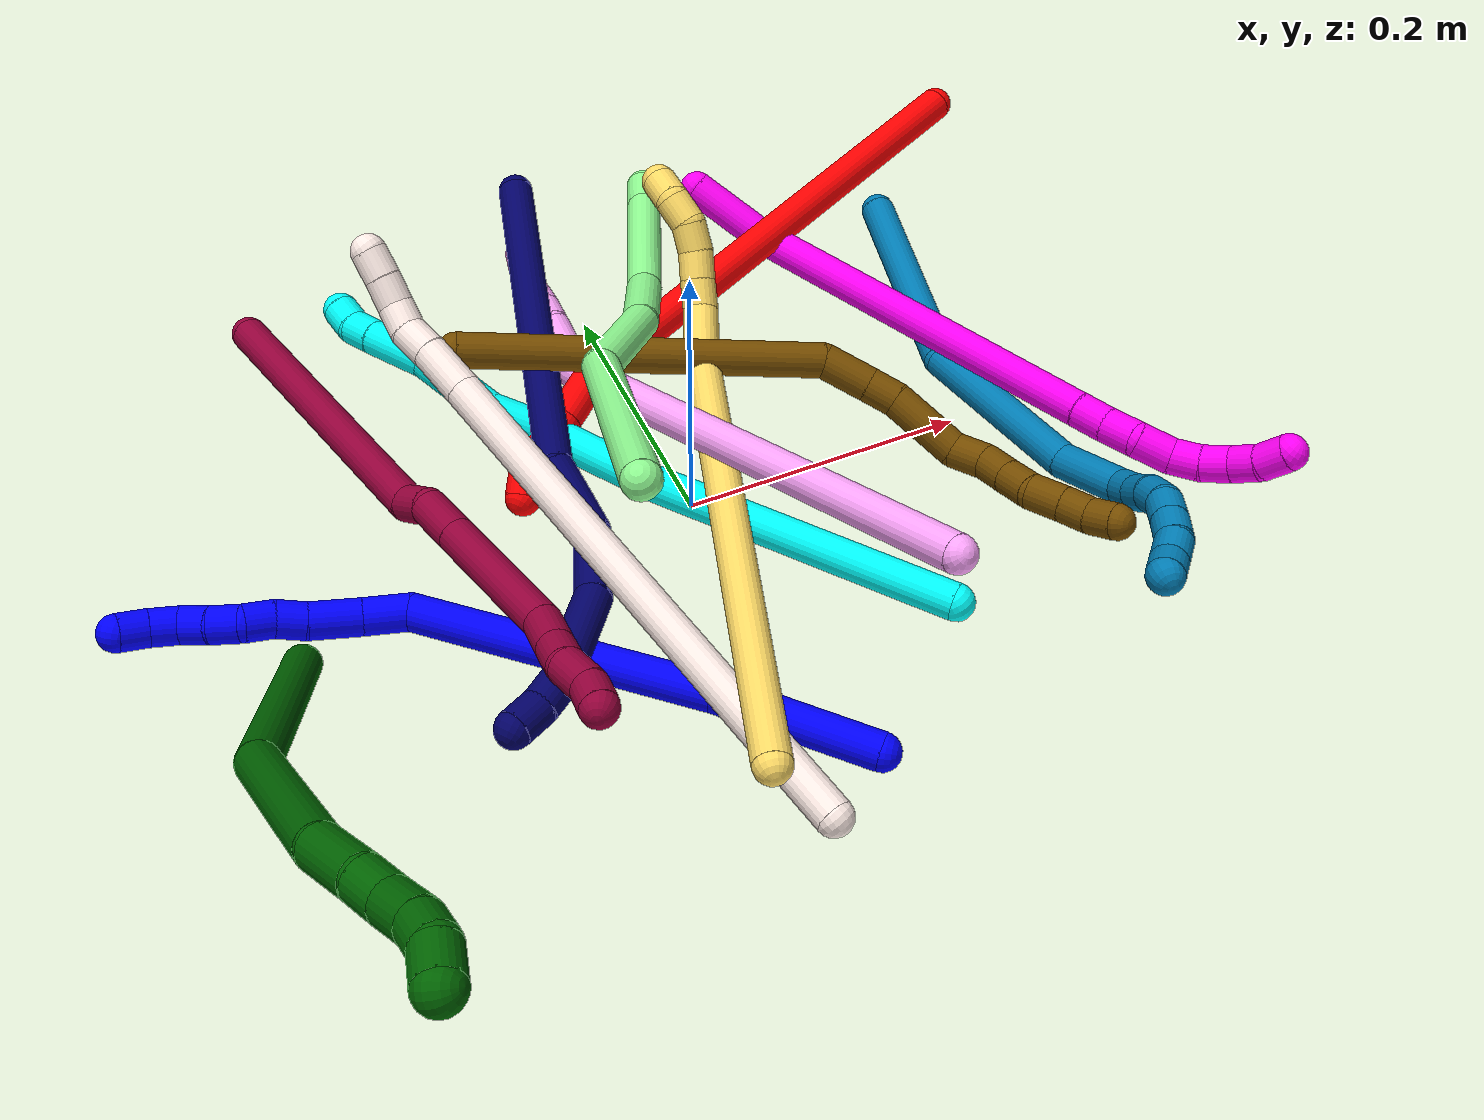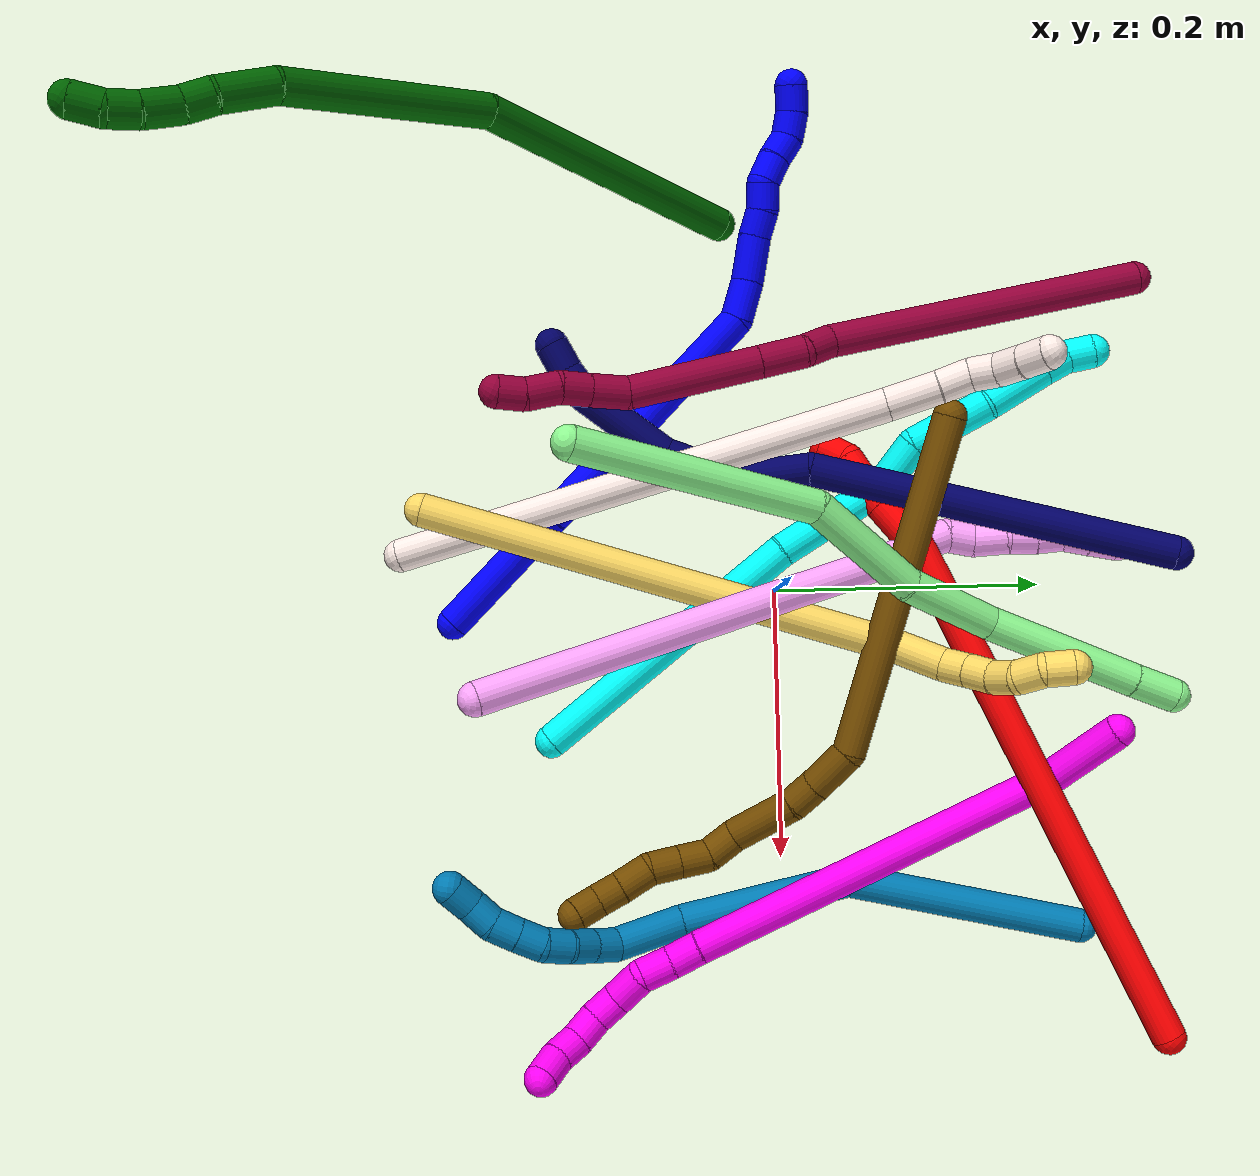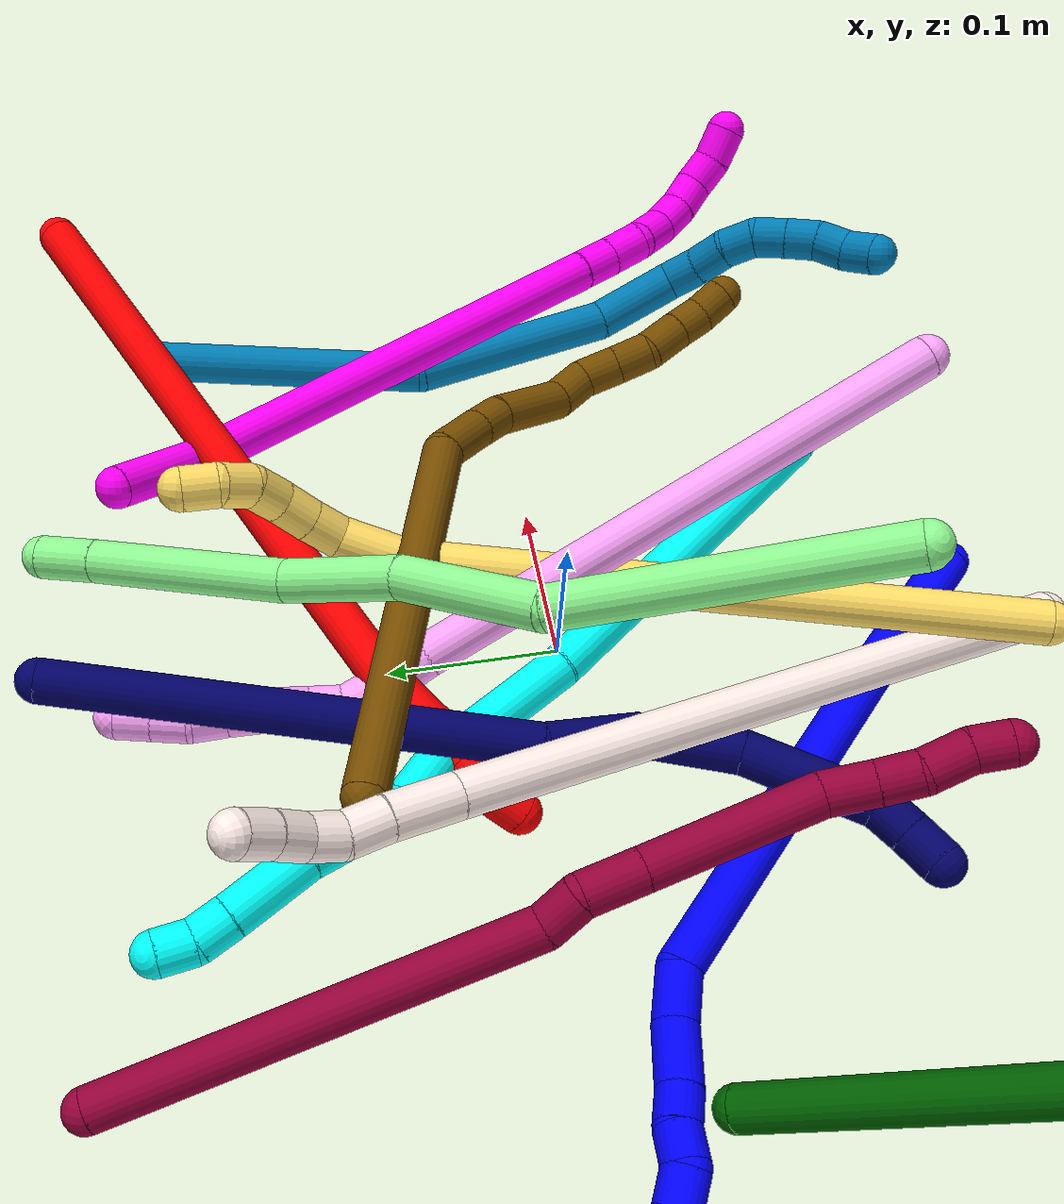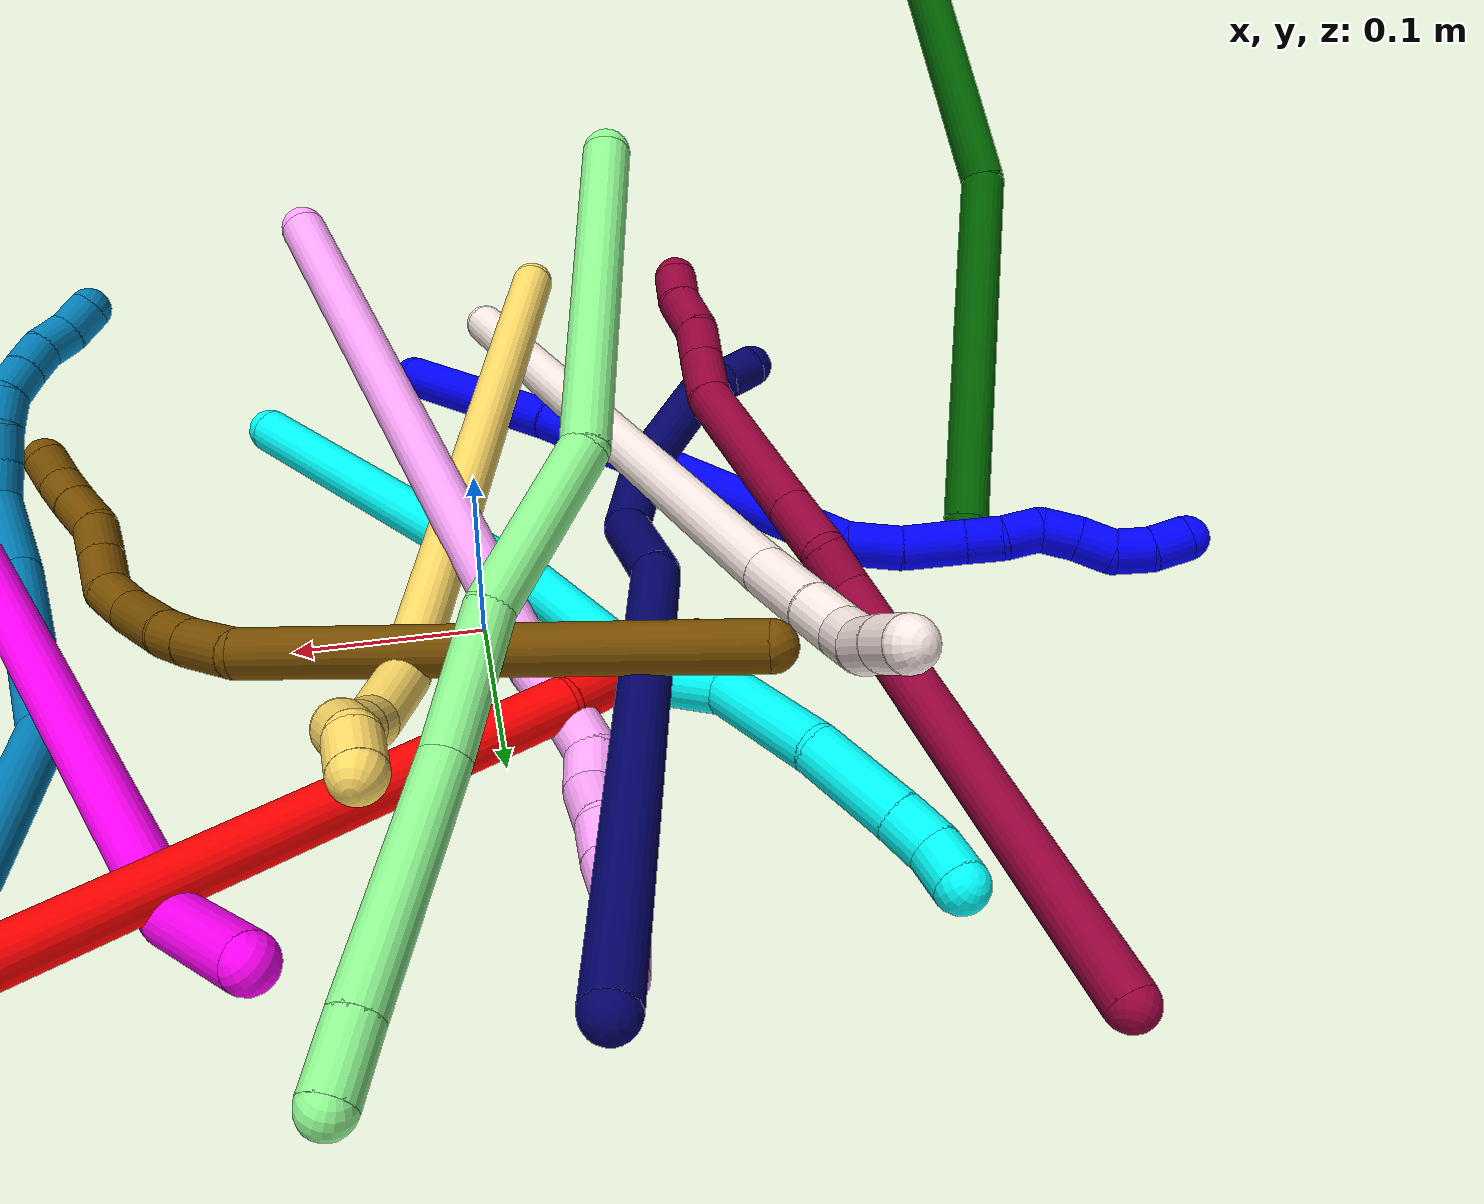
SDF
<sdf version="1.7">
 <world name="default">
  <plugin name="TubeGeneratorPlugin" filename="libtube_generator_plugin.so"/>
  <model name="photoneo_s_sensor">
   <static>1</static>
   <pose>0 0 2 1.57079 1.57079 3.14159</pose>
   <link name="link">
    <inertial><mass>0.1</mass></inertial>
    <sensor name="sensor" type="depth">
     <update_rate>30</update_rate>
     <camera>
      <horizontal_fov>1.22</horizontal_fov>
      <image><width>1920</width><height>1200</height><format>B8G8R8</format></image>
      <clip><near>0.1</near><far>4</far></clip>
      <depth_camera><output>points</output></depth_camera>
     </camera>
     <plugin name="camera_plugin" filename="libgazebo_ros_depth_camera.so">
      <baseline>0.2</baseline>
      <alwaysOn>1</alwaysOn>
      <updateRate>0.0</updateRate>
      <cameraName>camera_ir</cameraName>
      <imageTopicName>/camera/color/image_raw</imageTopicName>
      <cameraInfoTopicName>/camera/color/camera_info</cameraInfoTopicName>
      <depthImageTopicName>/camera/depth/image_raw</depthImageTopicName>
      <depthImageCameraInfoTopicName>/camera/depth/camera_info</depthImageCameraInfoTopicName>
      <pointCloudTopicName>/camera/depth/points</pointCloudTopicName>
      <frameName>fr_optical</frameName>
      <pointCloudCutoff>0.1</pointCloudCutoff>
      <pointCloudCutoffMax>2.0</pointCloudCutoffMax>
      <distortionK1>0</distortionK1>
      <distortionK2>0</distortionK2>
      <distortionK3>0</distortionK3>
      <distortionT1>0</distortionT1>
      <distortionT2>0</distortionT2>
      <CxPrime>0</CxPrime>
      <Cx>0</Cx>
      <Cy>0</Cy>
      <focalLength>0</focalLength>
      <hackBaseline>0</hackBaseline>
     </plugin>
    </sensor>
   </link>
  </model>
  <gravity>0 0 -9.8</gravity>
  <magnetic_field>6e-06 2.3e-05 -4.2e-05</magnetic_field>
  <atmosphere type="adiabatic"/>
  <physics name="default_physics" default="0" type="ode">
   <max_step_size>0.003</max_step_size>
   <real_time_factor>1</real_time_factor>
   <real_time_update_rate>1000</real_time_update_rate>
   <max_contacts>10000</max_contacts>
   <ode>
    <solver>
     <type>quick</type>
     <iters>100</iters>
     <sor>1.3</sor>
     <use_dynamic_moi_rescaling>0</use_dynamic_moi_rescaling>
    </solver>
    <constraints>
     <contact_max_correcting_vel>0</contact_max_correcting_vel>
     <contact_surface_layer>0.001</contact_surface_layer>
     <cfm>0</cfm>
     <erp>0.2</erp>
    </constraints>
   </ode>
  </physics>
  <scene><ambient>0.4 0.4 0.4 1</ambient><background>0.7 0.7 0.7 1</background><shadows>0</shadows></scene>
  <audio><device>default</device></audio>
  <spherical_coordinates>
   <surface_model>EARTH_WGS84</surface_model>
   <latitude_deg>0</latitude_deg>
   <longitude_deg>0</longitude_deg>
   <elevation>0</elevation>
   <heading_deg>0</heading_deg>
  </spherical_coordinates>
  <model name="bin">
   <static>1</static>
   <link name="bottom">
    <collision name="collision-bottom">
     <pose>0 0 -0.01 0 -0 0</pose>
     <geometry><box><size>0.8 0.6 0.02</size></box></geometry>
     <surface>
      <friction><ode><mu>100</mu><mu2>100</mu2></ode></friction>
      <contact><collide_bitmask>65535</collide_bitmask></contact>
     </surface>
    </collision>
   </link>
   <link name="west_wall">
    <collision name="collision-west_wall">
     <pose>-0.41 0 0.1 0 -0 0</pose>
     <geometry><box><size>0.02 0.6 0.2</size></box></geometry>
     <surface>
      <friction><ode><mu>100</mu><mu2>100</mu2></ode></friction>
      <contact><collide_bitmask>65535</collide_bitmask></contact>
     </surface>
    </collision>
   </link>
   <link name="east_wall">
    <collision name="collision-east_wall">
     <pose>0.41 0 0.1 0 -0 0</pose>
     <geometry><box><size>0.02 0.6 0.2</size></box></geometry>
     <surface>
      <friction><ode><mu>100</mu><mu2>100</mu2></ode></friction>
      <contact><collide_bitmask>65535</collide_bitmask></contact>
     </surface>
    </collision>
   </link>
   <link name="south_wall">
    <collision name="collision-south_wall">
     <pose>0 -0.31 0.1 0 -0 0</pose>
     <geometry><box><size>0.8 0.02 0.2</size></box></geometry>
     <surface>
      <friction><ode><mu>100</mu><mu2>100</mu2></ode></friction>
      <contact><collide_bitmask>65535</collide_bitmask></contact>
     </surface>
    </collision>
   </link>
   <link name="north_wall">
    <collision name="collision-north_wall">
     <pose>0 0.31 0.1 0 -0 0</pose>
     <geometry><box><size>0.8 0.02 0.2</size></box></geometry>
     <surface>
      <friction><ode><mu>100</mu><mu2>100</mu2></ode></friction>
      <contact><collide_bitmask>65535</collide_bitmask></contact>
     </surface>
    </collision>
   </link>
  </model>
  <model name="1">
   <static>0</static>
   <link name="1">
    <collision name="collision-cylinder-e_1_1_4">
     <pose>-0.006779 -0.004746 0.053372 0.088686 -0.125846 -0.005591</pose>
     <geometry><cylinder><radius>0.0125</radius><length>0.10802</length></cylinder></geometry>
     <surface>
      <friction><ode><mu>1.16</mu><mu2>1.16</mu2><slip1>0</slip1><slip2>0</slip2></ode></friction>
      <contact><ode><kp>1e+06</kp><kd>1</kd><max_vel>0</max_vel><min_depth>0.001</min_depth></ode></contact>
     </surface>
    </collision>
    <visual name="visual-cylinder-e_1_1_4">
     <pose>-0.006779 -0.004746 0.053372 0.088686 -0.125846 -0.005591</pose>
     <geometry><cylinder><radius>0.0125</radius><length>0.10802</length></cylinder></geometry>
     <material><ambient>0 0 1 1</ambient></material>
    </visual>
    <collision name="collision-cylinder-e_2_4_5">
     <pose>-0.016339 -0.016219 0.209238 0.065539 -0.027069 -0.000887</pose>
     <geometry><cylinder><radius>0.0125</radius><length>0.205503</length></cylinder></geometry>
     <surface>
      <friction><ode><mu>1.16</mu><mu2>1.16</mu2><slip1>0</slip1><slip2>0</slip2></ode></friction>
      <contact><ode><kp>1e+06</kp><kd>1</kd><max_vel>0</max_vel><min_depth>0.001</min_depth></ode></contact>
     </surface>
    </collision>
    <visual name="visual-cylinder-e_2_4_5">
     <pose>-0.016339 -0.016219 0.209238 0.065539 -0.027069 -0.000887</pose>
     <geometry><cylinder><radius>0.0125</radius><length>0.205503</length></cylinder></geometry>
     <material><ambient>0 0 1 1</ambient></material>
    </visual>
    <collision name="collision-cylinder-e_3_5_6">
     <pose>-0.020133 -0.017 0.3258 -0.399866 -0.066256 0.013431</pose>
     <geometry><cylinder><radius>0.0125</radius><length>0.030614</length></cylinder></geometry>
     <surface>
      <friction><ode><mu>1.16</mu><mu2>1.16</mu2><slip1>0</slip1><slip2>0</slip2></ode></friction>
      <contact><ode><kp>1e+06</kp><kd>1</kd><max_vel>0</max_vel><min_depth>0.001</min_depth></ode></contact>
     </surface>
    </collision>
    <visual name="visual-cylinder-e_3_5_6">
     <pose>-0.020133 -0.017 0.3258 -0.399866 -0.066256 0.013431</pose>
     <geometry><cylinder><radius>0.0125</radius><length>0.030614</length></cylinder></geometry>
     <material><ambient>0 0 1 1</ambient></material>
    </visual>
    <collision name="collision-cylinder-e_4_6_7">
     <pose>-0.025167 -0.002764 0.354749 -0.508243 -0.231746 0.060445</pose>
     <geometry><cylinder><radius>0.0125</radius><length>0.035004</length></cylinder></geometry>
     <surface>
      <friction><ode><mu>1.16</mu><mu2>1.16</mu2><slip1>0</slip1><slip2>0</slip2></ode></friction>
      <contact><ode><kp>1e+06</kp><kd>1</kd><max_vel>0</max_vel><min_depth>0.001</min_depth></ode></contact>
     </surface>
    </collision>
    <visual name="visual-cylinder-e_4_6_7">
     <pose>-0.025167 -0.002764 0.354749 -0.508243 -0.231746 0.060445</pose>
     <geometry><cylinder><radius>0.0125</radius><length>0.035004</length></cylinder></geometry>
     <material><ambient>0 0 1 1</ambient></material>
    </visual>
    <collision name="collision-cylinder-e_5_7_8">
     <pose>-0.032319 0.009034 0.378595 -0.373022 -0.314532 0.05983</pose>
     <geometry><cylinder><radius>0.0125</radius><length>0.020247</length></cylinder></geometry>
     <surface>
      <friction><ode><mu>1.16</mu><mu2>1.16</mu2><slip1>0</slip1><slip2>0</slip2></ode></friction>
      <contact><ode><kp>1e+06</kp><kd>1</kd><max_vel>0</max_vel><min_depth>0.001</min_depth></ode></contact>
     </surface>
    </collision>
    <visual name="visual-cylinder-e_5_7_8">
     <pose>-0.032319 0.009034 0.378595 -0.373022 -0.314532 0.05983</pose>
     <geometry><cylinder><radius>0.0125</radius><length>0.020247</length></cylinder></geometry>
     <material><ambient>0 0 1 1</ambient></material>
    </visual>
    <collision name="collision-cylinder-e_6_8_9">
     <pose>-0.038325 0.018417 0.395248 -0.652564 -0.288819 0.098335</pose>
     <geometry><cylinder><radius>0.0125</radius><length>0.020188</length></cylinder></geometry>
     <surface>
      <friction><ode><mu>1.16</mu><mu2>1.16</mu2><slip1>0</slip1><slip2>0</slip2></ode></friction>
      <contact><ode><kp>1e+06</kp><kd>1</kd><max_vel>0</max_vel><min_depth>0.001</min_depth></ode></contact>
     </surface>
    </collision>
    <visual name="visual-cylinder-e_6_8_9">
     <pose>-0.038325 0.018417 0.395248 -0.652564 -0.288819 0.098335</pose>
     <geometry><cylinder><radius>0.0125</radius><length>0.020188</length></cylinder></geometry>
     <material><ambient>0 0 1 1</ambient></material>
    </visual>
    <collision name="collision-cylinder-e_7_9_10">
     <pose>-0.040935 0.026974 0.412779 -0.265887 0.026063 -0.003486</pose>
     <geometry><cylinder><radius>0.0125</radius><length>0.020411</length></cylinder></geometry>
     <surface>
      <friction><ode><mu>1.16</mu><mu2>1.16</mu2><slip1>0</slip1><slip2>0</slip2></ode></friction>
      <contact><ode><kp>1e+06</kp><kd>1</kd><max_vel>0</max_vel><min_depth>0.001</min_depth></ode></contact>
     </surface>
    </collision>
    <visual name="visual-cylinder-e_7_9_10">
     <pose>-0.040935 0.026974 0.412779 -0.265887 0.026063 -0.003486</pose>
     <geometry><cylinder><radius>0.0125</radius><length>0.020411</length></cylinder></geometry>
     <material><ambient>0 0 1 1</ambient></material>
    </visual>
    <collision name="collision-cylinder-e_8_10_11">
     <pose>-0.039665 0.031046 0.432481 -0.140242 0.100452 -0.007061</pose>
     <geometry><cylinder><radius>0.0125</radius><length>0.020012</length></cylinder></geometry>
     <surface>
      <friction><ode><mu>1.16</mu><mu2>1.16</mu2><slip1>0</slip1><slip2>0</slip2></ode></friction>
      <contact><ode><kp>1e+06</kp><kd>1</kd><max_vel>0</max_vel><min_depth>0.001</min_depth></ode></contact>
     </surface>
    </collision>
    <visual name="visual-cylinder-e_8_10_11">
     <pose>-0.039665 0.031046 0.432481 -0.140242 0.100452 -0.007061</pose>
     <geometry><cylinder><radius>0.0125</radius><length>0.020012</length></cylinder></geometry>
     <material><ambient>0 0 1 1</ambient></material>
    </visual>
    <collision name="collision-cylinder-e_9_11_12">
     <pose>-0.040594 0.037038 0.451005 -0.488063 -0.1945 0.048573</pose>
     <geometry><cylinder><radius>0.0125</radius><length>0.02</length></cylinder></geometry>
     <surface>
      <friction><ode><mu>1.16</mu><mu2>1.16</mu2><slip1>0</slip1><slip2>0</slip2></ode></friction>
      <contact><ode><kp>1e+06</kp><kd>1</kd><max_vel>0</max_vel><min_depth>0.001</min_depth></ode></contact>
     </surface>
    </collision>
    <visual name="visual-cylinder-e_9_11_12">
     <pose>-0.040594 0.037038 0.451005 -0.488063 -0.1945 0.048573</pose>
     <geometry><cylinder><radius>0.0125</radius><length>0.02</length></cylinder></geometry>
     <material><ambient>0 0 1 1</ambient></material>
    </visual>
    <collision name="collision-cylinder-e_10_12_2">
     <pose>-0.045834 0.04784 0.466785 -0.716867 -0.336978 0.127273</pose>
     <geometry><cylinder><radius>0.0125</radius><length>0.020001</length></cylinder></geometry>
     <surface>
      <friction><ode><mu>1.16</mu><mu2>1.16</mu2><slip1>0</slip1><slip2>0</slip2></ode></friction>
      <contact><ode><kp>1e+06</kp><kd>1</kd><max_vel>0</max_vel><min_depth>0.001</min_depth></ode></contact>
     </surface>
    </collision>
    <visual name="visual-cylinder-e_10_12_2">
     <pose>-0.045834 0.04784 0.466785 -0.716867 -0.336978 0.127273</pose>
     <geometry><cylinder><radius>0.0125</radius><length>0.020001</length></cylinder></geometry>
     <material><ambient>0 0 1 1</ambient></material>
    </visual>
    <collision name="collision-sphere-2">
     <pose>-0.04914 0.054041 0.4739 0 -0 0</pose>
     <geometry><sphere><radius>0.0125</radius></sphere></geometry>
     <surface>
      <friction><ode><mu>1.16</mu><mu2>1.16</mu2><slip1>0</slip1><slip2>0</slip2></ode></friction>
      <contact><ode><kp>1e+06</kp><kd>1</kd><max_vel>0</max_vel><min_depth>0.001</min_depth></ode></contact>
     </surface>
    </collision>
    <visual name="visual-sphere-2">
     <pose>-0.04914 0.054041 0.4739 0 -0 0</pose>
     <geometry><sphere><radius>0.0125</radius></sphere></geometry>
     <material><ambient>0 0 1 1</ambient></material>
    </visual>
    <collision name="collision-sphere-12">
     <pose>-0.042527 0.041639 0.459671 0 -0 0</pose>
     <geometry><sphere><radius>0.0125</radius></sphere></geometry>
     <surface>
      <friction><ode><mu>1.16</mu><mu2>1.16</mu2><slip1>0</slip1><slip2>0</slip2></ode></friction>
      <contact><ode><kp>1e+06</kp><kd>1</kd><max_vel>0</max_vel><min_depth>0.001</min_depth></ode></contact>
     </surface>
    </collision>
    <visual name="visual-sphere-12">
     <pose>-0.042527 0.041639 0.459671 0 -0 0</pose>
     <geometry><sphere><radius>0.0125</radius></sphere></geometry>
     <material><ambient>0 0 1 1</ambient></material>
    </visual>
    <collision name="collision-sphere-11">
     <pose>-0.038662 0.032438 0.442339 0 -0 0</pose>
     <geometry><sphere><radius>0.0125</radius></sphere></geometry>
     <surface>
      <friction><ode><mu>1.16</mu><mu2>1.16</mu2><slip1>0</slip1><slip2>0</slip2></ode></friction>
      <contact><ode><kp>1e+06</kp><kd>1</kd><max_vel>0</max_vel><min_depth>0.001</min_depth></ode></contact>
     </surface>
    </collision>
    <visual name="visual-sphere-11">
     <pose>-0.038662 0.032438 0.442339 0 -0 0</pose>
     <geometry><sphere><radius>0.0125</radius></sphere></geometry>
     <material><ambient>0 0 1 1</ambient></material>
    </visual>
    <collision name="collision-sphere-10">
     <pose>-0.040669 0.029654 0.422623 0 -0 0</pose>
     <geometry><sphere><radius>0.0125</radius></sphere></geometry>
     <surface>
      <friction><ode><mu>1.16</mu><mu2>1.16</mu2><slip1>0</slip1><slip2>0</slip2></ode></friction>
      <contact><ode><kp>1e+06</kp><kd>1</kd><max_vel>0</max_vel><min_depth>0.001</min_depth></ode></contact>
     </surface>
    </collision>
    <visual name="visual-sphere-10">
     <pose>-0.040669 0.029654 0.422623 0 -0 0</pose>
     <geometry><sphere><radius>0.0125</radius></sphere></geometry>
     <material><ambient>0 0 1 1</ambient></material>
    </visual>
    <collision name="collision-sphere-9">
     <pose>-0.0412 0.024293 0.402936 0 -0 0</pose>
     <geometry><sphere><radius>0.0125</radius></sphere></geometry>
     <surface>
      <friction><ode><mu>1.16</mu><mu2>1.16</mu2><slip1>0</slip1><slip2>0</slip2></ode></friction>
      <contact><ode><kp>1e+06</kp><kd>1</kd><max_vel>0</max_vel><min_depth>0.001</min_depth></ode></contact>
     </surface>
    </collision>
    <visual name="visual-sphere-9">
     <pose>-0.0412 0.024293 0.402936 0 -0 0</pose>
     <geometry><sphere><radius>0.0125</radius></sphere></geometry>
     <material><ambient>0 0 1 1</ambient></material>
    </visual>
    <collision name="collision-sphere-4">
     <pose>-0.013558 -0.009492 0.106745 0 -0 0</pose>
     <geometry><sphere><radius>0.0125</radius></sphere></geometry>
     <surface>
      <friction><ode><mu>1.16</mu><mu2>1.16</mu2><slip1>0</slip1><slip2>0</slip2></ode></friction>
      <contact><ode><kp>1e+06</kp><kd>1</kd><max_vel>0</max_vel><min_depth>0.001</min_depth></ode></contact>
     </surface>
    </collision>
    <visual name="visual-sphere-4">
     <pose>-0.013558 -0.009492 0.106745 0 -0 0</pose>
     <geometry><sphere><radius>0.0125</radius></sphere></geometry>
     <material><ambient>0 0 1 1</ambient></material>
    </visual>
    <collision name="collision-sphere-1">
     <geometry><sphere><radius>0.0125</radius></sphere></geometry>
     <surface>
      <friction><ode><mu>1.16</mu><mu2>1.16</mu2><slip1>0</slip1><slip2>0</slip2></ode></friction>
      <contact><ode><kp>1e+06</kp><kd>1</kd><max_vel>0</max_vel><min_depth>0.001</min_depth></ode></contact>
     </surface>
    </collision>
    <visual name="visual-sphere-1">
     <geometry><sphere><radius>0.0125</radius></sphere></geometry>
     <material><ambient>0 0 1 1</ambient></material>
    </visual>
    <collision name="collision-sphere-8">
     <pose>-0.035451 0.012542 0.38756 0 -0 0</pose>
     <geometry><sphere><radius>0.0125</radius></sphere></geometry>
     <surface>
      <friction><ode><mu>1.16</mu><mu2>1.16</mu2><slip1>0</slip1><slip2>0</slip2></ode></friction>
      <contact><ode><kp>1e+06</kp><kd>1</kd><max_vel>0</max_vel><min_depth>0.001</min_depth></ode></contact>
     </surface>
    </collision>
    <visual name="visual-sphere-8">
     <pose>-0.035451 0.012542 0.38756 0 -0 0</pose>
     <geometry><sphere><radius>0.0125</radius></sphere></geometry>
     <material><ambient>0 0 1 1</ambient></material>
    </visual>
    <collision name="collision-sphere-5">
     <pose>-0.01912 -0.022946 0.311731 0 -0 0</pose>
     <geometry><sphere><radius>0.0125</radius></sphere></geometry>
     <surface>
      <friction><ode><mu>1.16</mu><mu2>1.16</mu2><slip1>0</slip1><slip2>0</slip2></ode></friction>
      <contact><ode><kp>1e+06</kp><kd>1</kd><max_vel>0</max_vel><min_depth>0.001</min_depth></ode></contact>
     </surface>
    </collision>
    <visual name="visual-sphere-5">
     <pose>-0.01912 -0.022946 0.311731 0 -0 0</pose>
     <geometry><sphere><radius>0.0125</radius></sphere></geometry>
     <material><ambient>0 0 1 1</ambient></material>
    </visual>
    <collision name="collision-sphere-6">
     <pose>-0.021147 -0.011054 0.339868 0 -0 0</pose>
     <geometry><sphere><radius>0.0125</radius></sphere></geometry>
     <surface>
      <friction><ode><mu>1.16</mu><mu2>1.16</mu2><slip1>0</slip1><slip2>0</slip2></ode></friction>
      <contact><ode><kp>1e+06</kp><kd>1</kd><max_vel>0</max_vel><min_depth>0.001</min_depth></ode></contact>
     </surface>
    </collision>
    <visual name="visual-sphere-6">
     <pose>-0.021147 -0.011054 0.339868 0 -0 0</pose>
     <geometry><sphere><radius>0.0125</radius></sphere></geometry>
     <material><ambient>0 0 1 1</ambient></material>
    </visual>
    <collision name="collision-sphere-7">
     <pose>-0.029187 0.005525 0.36963 0 -0 0</pose>
     <geometry><sphere><radius>0.0125</radius></sphere></geometry>
     <surface>
      <friction><ode><mu>1.16</mu><mu2>1.16</mu2><slip1>0</slip1><slip2>0</slip2></ode></friction>
      <contact><ode><kp>1e+06</kp><kd>1</kd><max_vel>0</max_vel><min_depth>0.001</min_depth></ode></contact>
     </surface>
    </collision>
    <visual name="visual-sphere-7">
     <pose>-0.029187 0.005525 0.36963 0 -0 0</pose>
     <geometry><sphere><radius>0.0125</radius></sphere></geometry>
     <material><ambient>0 0 1 1</ambient></material>
    </visual>
    <inertial>
     <pose>-0.020747 -0.002077 0.244474 0 -0 0</pose>
     <mass>0.5</mass>
     <inertia>
      <ixx>0.000852</ixx>
      <ixy>0</ixy>
      <ixz>0</ixz>
      <iyy>0.000858</iyy>
      <iyz>0</iyz>
      <izz>0.000124</izz>
     </inertia>
    </inertial>
   </link>
   <pose>0.018881 -0.241973 0.011734 -2.35591 1.48306 0.084673</pose>
  </model>
  <model name="2">
   <static>0</static>
   <link name="2">
    <collision name="collision-cylinder-e_1_1_4">
     <pose>-0.026021 -0.061058 -0.185401 2.82345 -0.132525 -0.784425</pose>
     <geometry><cylinder><radius>0.0125</radius><length>0.393847</length></cylinder></geometry>
     <surface>
      <friction><ode><mu>1.16</mu><mu2>1.16</mu2><slip1>0</slip1><slip2>0</slip2></ode></friction>
      <contact><ode><kp>1e+06</kp><kd>1</kd><max_vel>0</max_vel><min_depth>0.001</min_depth></ode></contact>
     </surface>
    </collision>
    <visual name="visual-cylinder-e_1_1_4">
     <pose>-0.026021 -0.061058 -0.185401 2.82345 -0.132525 -0.784425</pose>
     <geometry><cylinder><radius>0.0125</radius><length>0.393847</length></cylinder></geometry>
     <material><ambient>1 0 0 1</ambient></material>
    </visual>
    <collision name="collision-cylinder-e_2_4_5">
     <pose>-0.053055 -0.12286 -0.391155 3.10509 -0.049683 -1.87452</pose>
     <geometry><cylinder><radius>0.0125</radius><length>0.040781</length></cylinder></geometry>
     <surface>
      <friction><ode><mu>1.16</mu><mu2>1.16</mu2><slip1>0</slip1><slip2>0</slip2></ode></friction>
      <contact><ode><kp>1e+06</kp><kd>1</kd><max_vel>0</max_vel><min_depth>0.001</min_depth></ode></contact>
     </surface>
    </collision>
    <visual name="visual-cylinder-e_2_4_5">
     <pose>-0.053055 -0.12286 -0.391155 3.10509 -0.049683 -1.87452</pose>
     <geometry><cylinder><radius>0.0125</radius><length>0.040781</length></cylinder></geometry>
     <material><ambient>1 0 0 1</ambient></material>
    </visual>
    <collision name="collision-cylinder-e_3_5_6">
     <pose>-0.054685 -0.124229 -0.422753 3.08598 -0.0548 -1.55607</pose>
     <geometry><cylinder><radius>0.0125</radius><length>0.022562</length></cylinder></geometry>
     <surface>
      <friction><ode><mu>1.16</mu><mu2>1.16</mu2><slip1>0</slip1><slip2>0</slip2></ode></friction>
      <contact><ode><kp>1e+06</kp><kd>1</kd><max_vel>0</max_vel><min_depth>0.001</min_depth></ode></contact>
     </surface>
    </collision>
    <visual name="visual-cylinder-e_3_5_6">
     <pose>-0.054685 -0.124229 -0.422753 3.08598 -0.0548 -1.55607</pose>
     <geometry><cylinder><radius>0.0125</radius><length>0.022562</length></cylinder></geometry>
     <material><ambient>1 0 0 1</ambient></material>
    </visual>
    <collision name="collision-cylinder-e_4_6_7">
     <pose>-0.057496 -0.125456 -0.444895 3.0865 -0.198338 -2.60129</pose>
     <geometry><cylinder><radius>0.0125</radius><length>0.02226</length></cylinder></geometry>
     <surface>
      <friction><ode><mu>1.16</mu><mu2>1.16</mu2><slip1>0</slip1><slip2>0</slip2></ode></friction>
      <contact><ode><kp>1e+06</kp><kd>1</kd><max_vel>0</max_vel><min_depth>0.001</min_depth></ode></contact>
     </surface>
    </collision>
    <visual name="visual-cylinder-e_4_6_7">
     <pose>-0.057496 -0.125456 -0.444895 3.0865 -0.198338 -2.60129</pose>
     <geometry><cylinder><radius>0.0125</radius><length>0.02226</length></cylinder></geometry>
     <material><ambient>1 0 0 1</ambient></material>
    </visual>
    <collision name="collision-cylinder-e_5_7_2">
     <pose>-0.059292 -0.122029 -0.465234 -2.73844 0.038625 -0.188473</pose>
     <geometry><cylinder><radius>0.0125</radius><length>0.02055</length></cylinder></geometry>
     <surface>
      <friction><ode><mu>1.16</mu><mu2>1.16</mu2><slip1>0</slip1><slip2>0</slip2></ode></friction>
      <contact><ode><kp>1e+06</kp><kd>1</kd><max_vel>0</max_vel><min_depth>0.001</min_depth></ode></contact>
     </surface>
    </collision>
    <visual name="visual-cylinder-e_5_7_2">
     <pose>-0.059292 -0.122029 -0.465234 -2.73844 0.038625 -0.188473</pose>
     <geometry><cylinder><radius>0.0125</radius><length>0.02055</length></cylinder></geometry>
     <material><ambient>1 0 0 1</ambient></material>
    </visual>
    <collision name="collision-sphere-2">
     <pose>-0.058896 -0.118001 -0.474678 0 -0 0</pose>
     <geometry><sphere><radius>0.0125</radius></sphere></geometry>
     <surface>
      <friction><ode><mu>1.16</mu><mu2>1.16</mu2><slip1>0</slip1><slip2>0</slip2></ode></friction>
      <contact><ode><kp>1e+06</kp><kd>1</kd><max_vel>0</max_vel><min_depth>0.001</min_depth></ode></contact>
     </surface>
    </collision>
    <visual name="visual-sphere-2">
     <pose>-0.058896 -0.118001 -0.474678 0 -0 0</pose>
     <geometry><sphere><radius>0.0125</radius></sphere></geometry>
     <material><ambient>1 0 0 1</ambient></material>
    </visual>
    <collision name="collision-sphere-7">
     <pose>-0.059689 -0.126057 -0.45579 0 -0 0</pose>
     <geometry><sphere><radius>0.0125</radius></sphere></geometry>
     <surface>
      <friction><ode><mu>1.16</mu><mu2>1.16</mu2><slip1>0</slip1><slip2>0</slip2></ode></friction>
      <contact><ode><kp>1e+06</kp><kd>1</kd><max_vel>0</max_vel><min_depth>0.001</min_depth></ode></contact>
     </surface>
    </collision>
    <visual name="visual-sphere-7">
     <pose>-0.059689 -0.126057 -0.45579 0 -0 0</pose>
     <geometry><sphere><radius>0.0125</radius></sphere></geometry>
     <material><ambient>1 0 0 1</ambient></material>
    </visual>
    <collision name="collision-sphere-6">
     <pose>-0.055303 -0.124855 -0.434 0 -0 0</pose>
     <geometry><sphere><radius>0.0125</radius></sphere></geometry>
     <surface>
      <friction><ode><mu>1.16</mu><mu2>1.16</mu2><slip1>0</slip1><slip2>0</slip2></ode></friction>
      <contact><ode><kp>1e+06</kp><kd>1</kd><max_vel>0</max_vel><min_depth>0.001</min_depth></ode></contact>
     </surface>
    </collision>
    <visual name="visual-sphere-6">
     <pose>-0.055303 -0.124855 -0.434 0 -0 0</pose>
     <geometry><sphere><radius>0.0125</radius></sphere></geometry>
     <material><ambient>1 0 0 1</ambient></material>
    </visual>
    <collision name="collision-sphere-5">
     <pose>-0.054067 -0.123603 -0.411507 0 -0 0</pose>
     <geometry><sphere><radius>0.0125</radius></sphere></geometry>
     <surface>
      <friction><ode><mu>1.16</mu><mu2>1.16</mu2><slip1>0</slip1><slip2>0</slip2></ode></friction>
      <contact><ode><kp>1e+06</kp><kd>1</kd><max_vel>0</max_vel><min_depth>0.001</min_depth></ode></contact>
     </surface>
    </collision>
    <visual name="visual-sphere-5">
     <pose>-0.054067 -0.123603 -0.411507 0 -0 0</pose>
     <geometry><sphere><radius>0.0125</radius></sphere></geometry>
     <material><ambient>1 0 0 1</ambient></material>
    </visual>
    <collision name="collision-sphere-1">
     <geometry><sphere><radius>0.0125</radius></sphere></geometry>
     <surface>
      <friction><ode><mu>1.16</mu><mu2>1.16</mu2><slip1>0</slip1><slip2>0</slip2></ode></friction>
      <contact><ode><kp>1e+06</kp><kd>1</kd><max_vel>0</max_vel><min_depth>0.001</min_depth></ode></contact>
     </surface>
    </collision>
    <visual name="visual-sphere-1">
     <geometry><sphere><radius>0.0125</radius></sphere></geometry>
     <material><ambient>1 0 0 1</ambient></material>
    </visual>
    <collision name="collision-sphere-4">
     <pose>-0.052042 -0.122117 -0.370803 0 -0 0</pose>
     <geometry><sphere><radius>0.0125</radius></sphere></geometry>
     <surface>
      <friction><ode><mu>1.16</mu><mu2>1.16</mu2><slip1>0</slip1><slip2>0</slip2></ode></friction>
      <contact><ode><kp>1e+06</kp><kd>1</kd><max_vel>0</max_vel><min_depth>0.001</min_depth></ode></contact>
     </surface>
    </collision>
    <visual name="visual-sphere-4">
     <pose>-0.052042 -0.122117 -0.370803 0 -0 0</pose>
     <geometry><sphere><radius>0.0125</radius></sphere></geometry>
     <material><ambient>1 0 0 1</ambient></material>
    </visual>
    <inertial>
     <pose>-0.032288 -0.074322 -0.235947 0 -0 0</pose>
     <mass>0.5</mass>
     <inertia>
      <ixx>-1e-05</ixx>
      <ixy>0</ixy>
      <ixz>0</ixz>
      <iyy>-0.006876</iyy>
      <iyz>0</iyz>
      <izz>0.002222</izz>
     </inertia>
    </inertial>
   </link>
   <pose>0.32861 0.27027 0.058654 -1.29112 -0.557855 -1.00336</pose>
  </model>
  <model name="3">
   <static>0</static>
   <link name="3">
    <collision name="collision-cylinder-e_1_1_4">
     <pose>-0.093551 -0.005721 -0.058651 3.04435 -1.00867 -2.96573</pose>
     <geometry><cylinder><radius>0.0125</radius><length>0.221128</length></cylinder></geometry>
     <surface>
      <friction><ode><mu>1.16</mu><mu2>1.16</mu2><slip1>0</slip1><slip2>0</slip2></ode></friction>
      <contact><ode><kp>1e+06</kp><kd>1</kd><max_vel>0</max_vel><min_depth>0.001</min_depth></ode></contact>
     </surface>
    </collision>
    <visual name="visual-cylinder-e_1_1_4">
     <pose>-0.093551 -0.005721 -0.058651 3.04435 -1.00867 -2.96573</pose>
     <geometry><cylinder><radius>0.0125</radius><length>0.221128</length></cylinder></geometry>
     <material><ambient>0.003922 1 0.996078 1</ambient></material>
    </visual>
    <collision name="collision-cylinder-e_2_4_5">
     <pose>-0.224788 -0.019052 -0.139208 2.80728 -1.01917 -2.55512</pose>
     <geometry><cylinder><radius>0.0125</radius><length>0.088499</length></cylinder></geometry>
     <surface>
      <friction><ode><mu>1.16</mu><mu2>1.16</mu2><slip1>0</slip1><slip2>0</slip2></ode></friction>
      <contact><ode><kp>1e+06</kp><kd>1</kd><max_vel>0</max_vel><min_depth>0.001</min_depth></ode></contact>
     </surface>
    </collision>
    <visual name="visual-cylinder-e_2_4_5">
     <pose>-0.224788 -0.019052 -0.139208 2.80728 -1.01917 -2.55512</pose>
     <geometry><cylinder><radius>0.0125</radius><length>0.088499</length></cylinder></geometry>
     <material><ambient>0.003922 1 0.996078 1</ambient></material>
    </visual>
    <collision name="collision-cylinder-e_3_5_6">
     <pose>-0.275863 -0.023002 -0.175376 -2.89048 -0.737938 2.51056</pose>
     <geometry><cylinder><radius>0.0125</radius><length>0.039803</length></cylinder></geometry>
     <surface>
      <friction><ode><mu>1.16</mu><mu2>1.16</mu2><slip1>0</slip1><slip2>0</slip2></ode></friction>
      <contact><ode><kp>1e+06</kp><kd>1</kd><max_vel>0</max_vel><min_depth>0.001</min_depth></ode></contact>
     </surface>
    </collision>
    <visual name="visual-cylinder-e_3_5_6">
     <pose>-0.275863 -0.023002 -0.175376 -2.89048 -0.737938 2.51056</pose>
     <geometry><cylinder><radius>0.0125</radius><length>0.039803</length></cylinder></geometry>
     <material><ambient>0.003922 1 0.996078 1</ambient></material>
    </visual>
    <collision name="collision-cylinder-e_4_6_7">
     <pose>-0.311403 -0.026699 -0.209423 2.78562 -0.809528 -2.34652</pose>
     <geometry><cylinder><radius>0.0125</radius><length>0.061195</length></cylinder></geometry>
     <surface>
      <friction><ode><mu>1.16</mu><mu2>1.16</mu2><slip1>0</slip1><slip2>0</slip2></ode></friction>
      <contact><ode><kp>1e+06</kp><kd>1</kd><max_vel>0</max_vel><min_depth>0.001</min_depth></ode></contact>
     </surface>
    </collision>
    <visual name="visual-cylinder-e_4_6_7">
     <pose>-0.311403 -0.026699 -0.209423 2.78562 -0.809528 -2.34652</pose>
     <geometry><cylinder><radius>0.0125</radius><length>0.061195</length></cylinder></geometry>
     <material><ambient>0.003922 1 0.996078 1</ambient></material>
    </visual>
    <collision name="collision-cylinder-e_5_7_8">
     <pose>-0.354479 -0.038504 -0.240215 2.75755 -1.05465 -2.49715</pose>
     <geometry><cylinder><radius>0.0125</radius><length>0.048117</length></cylinder></geometry>
     <surface>
      <friction><ode><mu>1.16</mu><mu2>1.16</mu2><slip1>0</slip1><slip2>0</slip2></ode></friction>
      <contact><ode><kp>1e+06</kp><kd>1</kd><max_vel>0</max_vel><min_depth>0.001</min_depth></ode></contact>
     </surface>
    </collision>
    <visual name="visual-cylinder-e_5_7_8">
     <pose>-0.354479 -0.038504 -0.240215 2.75755 -1.05465 -2.49715</pose>
     <geometry><cylinder><radius>0.0125</radius><length>0.048117</length></cylinder></geometry>
     <material><ambient>0.003922 1 0.996078 1</ambient></material>
    </visual>
    <collision name="collision-cylinder-e_6_8_9">
     <pose>-0.384519 -0.045339 -0.255811 2.6619 -1.05482 -2.34655</pose>
     <geometry><cylinder><radius>0.0125</radius><length>0.020961</length></cylinder></geometry>
     <surface>
      <friction><ode><mu>1.16</mu><mu2>1.16</mu2><slip1>0</slip1><slip2>0</slip2></ode></friction>
      <contact><ode><kp>1e+06</kp><kd>1</kd><max_vel>0</max_vel><min_depth>0.001</min_depth></ode></contact>
     </surface>
    </collision>
    <visual name="visual-cylinder-e_6_8_9">
     <pose>-0.384519 -0.045339 -0.255811 2.6619 -1.05482 -2.34655</pose>
     <geometry><cylinder><radius>0.0125</radius><length>0.020961</length></cylinder></geometry>
     <material><ambient>0.003922 1 0.996078 1</ambient></material>
    </visual>
    <collision name="collision-cylinder-e_7_9_2">
     <pose>-0.40073 -0.052913 -0.265473 2.34523 -0.774147 -1.53937</pose>
     <geometry><cylinder><radius>0.0125</radius><length>0.020298</length></cylinder></geometry>
     <surface>
      <friction><ode><mu>1.16</mu><mu2>1.16</mu2><slip1>0</slip1><slip2>0</slip2></ode></friction>
      <contact><ode><kp>1e+06</kp><kd>1</kd><max_vel>0</max_vel><min_depth>0.001</min_depth></ode></contact>
     </surface>
    </collision>
    <visual name="visual-cylinder-e_7_9_2">
     <pose>-0.40073 -0.052913 -0.265473 2.34523 -0.774147 -1.53937</pose>
     <geometry><cylinder><radius>0.0125</radius><length>0.020298</length></cylinder></geometry>
     <material><ambient>0.003922 1 0.996078 1</ambient></material>
    </visual>
    <collision name="collision-sphere-2">
     <pose>-0.407825 -0.0581 -0.270548 0 -0 0</pose>
     <geometry><sphere><radius>0.0125</radius></sphere></geometry>
     <surface>
      <friction><ode><mu>1.16</mu><mu2>1.16</mu2><slip1>0</slip1><slip2>0</slip2></ode></friction>
      <contact><ode><kp>1e+06</kp><kd>1</kd><max_vel>0</max_vel><min_depth>0.001</min_depth></ode></contact>
     </surface>
    </collision>
    <visual name="visual-sphere-2">
     <pose>-0.407825 -0.0581 -0.270548 0 -0 0</pose>
     <geometry><sphere><radius>0.0125</radius></sphere></geometry>
     <material><ambient>0.003922 1 0.996078 1</ambient></material>
    </visual>
    <collision name="collision-sphere-9">
     <pose>-0.393635 -0.047725 -0.260399 0 -0 0</pose>
     <geometry><sphere><radius>0.0125</radius></sphere></geometry>
     <surface>
      <friction><ode><mu>1.16</mu><mu2>1.16</mu2><slip1>0</slip1><slip2>0</slip2></ode></friction>
      <contact><ode><kp>1e+06</kp><kd>1</kd><max_vel>0</max_vel><min_depth>0.001</min_depth></ode></contact>
     </surface>
    </collision>
    <visual name="visual-sphere-9">
     <pose>-0.393635 -0.047725 -0.260399 0 -0 0</pose>
     <geometry><sphere><radius>0.0125</radius></sphere></geometry>
     <material><ambient>0.003922 1 0.996078 1</ambient></material>
    </visual>
    <collision name="collision-sphere-4">
     <pose>-0.187101 -0.011443 -0.117301 0 -0 0</pose>
     <geometry><sphere><radius>0.0125</radius></sphere></geometry>
     <surface>
      <friction><ode><mu>1.16</mu><mu2>1.16</mu2><slip1>0</slip1><slip2>0</slip2></ode></friction>
      <contact><ode><kp>1e+06</kp><kd>1</kd><max_vel>0</max_vel><min_depth>0.001</min_depth></ode></contact>
     </surface>
    </collision>
    <visual name="visual-sphere-4">
     <pose>-0.187101 -0.011443 -0.117301 0 -0 0</pose>
     <geometry><sphere><radius>0.0125</radius></sphere></geometry>
     <material><ambient>0.003922 1 0.996078 1</ambient></material>
    </visual>
    <collision name="collision-sphere-1">
     <geometry><sphere><radius>0.0125</radius></sphere></geometry>
     <surface>
      <friction><ode><mu>1.16</mu><mu2>1.16</mu2><slip1>0</slip1><slip2>0</slip2></ode></friction>
      <contact><ode><kp>1e+06</kp><kd>1</kd><max_vel>0</max_vel><min_depth>0.001</min_depth></ode></contact>
     </surface>
    </collision>
    <visual name="visual-sphere-1">
     <geometry><sphere><radius>0.0125</radius></sphere></geometry>
     <material><ambient>0.003922 1 0.996078 1</ambient></material>
    </visual>
    <collision name="collision-sphere-8">
     <pose>-0.375403 -0.042953 -0.251224 0 -0 0</pose>
     <geometry><sphere><radius>0.0125</radius></sphere></geometry>
     <surface>
      <friction><ode><mu>1.16</mu><mu2>1.16</mu2><slip1>0</slip1><slip2>0</slip2></ode></friction>
      <contact><ode><kp>1e+06</kp><kd>1</kd><max_vel>0</max_vel><min_depth>0.001</min_depth></ode></contact>
     </surface>
    </collision>
    <visual name="visual-sphere-8">
     <pose>-0.375403 -0.042953 -0.251224 0 -0 0</pose>
     <geometry><sphere><radius>0.0125</radius></sphere></geometry>
     <material><ambient>0.003922 1 0.996078 1</ambient></material>
    </visual>
    <collision name="collision-sphere-5">
     <pose>-0.262474 -0.026661 -0.161114 0 -0 0</pose>
     <geometry><sphere><radius>0.0125</radius></sphere></geometry>
     <surface>
      <friction><ode><mu>1.16</mu><mu2>1.16</mu2><slip1>0</slip1><slip2>0</slip2></ode></friction>
      <contact><ode><kp>1e+06</kp><kd>1</kd><max_vel>0</max_vel><min_depth>0.001</min_depth></ode></contact>
     </surface>
    </collision>
    <visual name="visual-sphere-5">
     <pose>-0.262474 -0.026661 -0.161114 0 -0 0</pose>
     <geometry><sphere><radius>0.0125</radius></sphere></geometry>
     <material><ambient>0.003922 1 0.996078 1</ambient></material>
    </visual>
    <collision name="collision-sphere-6">
     <pose>-0.289252 -0.019344 -0.189639 0 -0 0</pose>
     <geometry><sphere><radius>0.0125</radius></sphere></geometry>
     <surface>
      <friction><ode><mu>1.16</mu><mu2>1.16</mu2><slip1>0</slip1><slip2>0</slip2></ode></friction>
      <contact><ode><kp>1e+06</kp><kd>1</kd><max_vel>0</max_vel><min_depth>0.001</min_depth></ode></contact>
     </surface>
    </collision>
    <visual name="visual-sphere-6">
     <pose>-0.289252 -0.019344 -0.189639 0 -0 0</pose>
     <geometry><sphere><radius>0.0125</radius></sphere></geometry>
     <material><ambient>0.003922 1 0.996078 1</ambient></material>
    </visual>
    <collision name="collision-sphere-7">
     <pose>-0.333554 -0.034055 -0.229207 0 -0 0</pose>
     <geometry><sphere><radius>0.0125</radius></sphere></geometry>
     <surface>
      <friction><ode><mu>1.16</mu><mu2>1.16</mu2><slip1>0</slip1><slip2>0</slip2></ode></friction>
      <contact><ode><kp>1e+06</kp><kd>1</kd><max_vel>0</max_vel><min_depth>0.001</min_depth></ode></contact>
     </surface>
    </collision>
    <visual name="visual-sphere-7">
     <pose>-0.333554 -0.034055 -0.229207 0 -0 0</pose>
     <geometry><sphere><radius>0.0125</radius></sphere></geometry>
     <material><ambient>0.003922 1 0.996078 1</ambient></material>
    </visual>
    <inertial>
     <pose>-0.207733 -0.018755 -0.134788 0 -0 0</pose>
     <mass>0.5</mass>
     <inertia>
      <ixx>-0.00067</ixx>
      <ixy>0</ixy>
      <ixz>0</ixz>
      <iyy>0.000879</iyy>
      <iyz>0</iyz>
      <izz>0.000898</izz>
     </inertia>
    </inertial>
   </link>
   <pose>0.108321 -0.168706 0.028461 3.12132 -0.547963 -0.841533</pose>
  </model>
  <model name="4">
   <static>0</static>
   <link name="4">
    <collision name="collision-cylinder-e_1_1_4">
     <pose>-0.004739 0.075698 -0.141115 -2.64923 -0.029583 0.117604</pose>
     <geometry><cylinder><radius>0.0125</radius><length>0.320413</length></cylinder></geometry>
     <surface>
      <friction><ode><mu>1.16</mu><mu2>1.16</mu2><slip1>0</slip1><slip2>0</slip2></ode></friction>
      <contact><ode><kp>1e+06</kp><kd>1</kd><max_vel>0</max_vel><min_depth>0.001</min_depth></ode></contact>
     </surface>
    </collision>
    <visual name="visual-cylinder-e_1_1_4">
     <pose>-0.004739 0.075698 -0.141115 -2.64923 -0.029583 0.117604</pose>
     <geometry><cylinder><radius>0.0125</radius><length>0.320413</length></cylinder></geometry>
     <material><ambient>1 0.65098 0.996078 1</ambient></material>
    </visual>
    <collision name="collision-cylinder-e_2_4_5">
     <pose>-0.01165 0.159292 -0.294547 -2.57149 -0.147395 0.49364</pose>
     <geometry><cylinder><radius>0.0125</radius><length>0.029581</length></cylinder></geometry>
     <surface>
      <friction><ode><mu>1.16</mu><mu2>1.16</mu2><slip1>0</slip1><slip2>0</slip2></ode></friction>
      <contact><ode><kp>1e+06</kp><kd>1</kd><max_vel>0</max_vel><min_depth>0.001</min_depth></ode></contact>
     </surface>
    </collision>
    <visual name="visual-cylinder-e_2_4_5">
     <pose>-0.01165 0.159292 -0.294547 -2.57149 -0.147395 0.49364</pose>
     <geometry><cylinder><radius>0.0125</radius><length>0.029581</length></cylinder></geometry>
     <material><ambient>1 0.65098 0.996078 1</ambient></material>
    </visual>
    <collision name="collision-cylinder-e_3_5_6">
     <pose>-0.01441 0.173381 -0.316309 -2.56123 -0.052049 0.173905</pose>
     <geometry><cylinder><radius>0.0125</radius><length>0.022622</length></cylinder></geometry>
     <surface>
      <friction><ode><mu>1.16</mu><mu2>1.16</mu2><slip1>0</slip1><slip2>0</slip2></ode></friction>
      <contact><ode><kp>1e+06</kp><kd>1</kd><max_vel>0</max_vel><min_depth>0.001</min_depth></ode></contact>
     </surface>
    </collision>
    <visual name="visual-cylinder-e_3_5_6">
     <pose>-0.01441 0.173381 -0.316309 -2.56123 -0.052049 0.173905</pose>
     <geometry><cylinder><radius>0.0125</radius><length>0.022622</length></cylinder></geometry>
     <material><ambient>1 0.65098 0.996078 1</ambient></material>
    </visual>
    <collision name="collision-cylinder-e_4_6_7">
     <pose>-0.010231 0.185006 -0.333589 -2.53538 0.463744 -1.29338</pose>
     <geometry><cylinder><radius>0.0125</radius><length>0.021316</length></cylinder></geometry>
     <surface>
      <friction><ode><mu>1.16</mu><mu2>1.16</mu2><slip1>0</slip1><slip2>0</slip2></ode></friction>
      <contact><ode><kp>1e+06</kp><kd>1</kd><max_vel>0</max_vel><min_depth>0.001</min_depth></ode></contact>
     </surface>
    </collision>
    <visual name="visual-cylinder-e_4_6_7">
     <pose>-0.010231 0.185006 -0.333589 -2.53538 0.463744 -1.29338</pose>
     <geometry><cylinder><radius>0.0125</radius><length>0.021316</length></cylinder></geometry>
     <material><ambient>1 0.65098 0.996078 1</ambient></material>
    </visual>
    <collision name="collision-cylinder-e_5_7_8">
     <pose>-0.002411 0.201306 -0.347907 -2.10865 0.236683 -0.412772</pose>
     <geometry><cylinder><radius>0.0125</radius><length>0.026037</length></cylinder></geometry>
     <surface>
      <friction><ode><mu>1.16</mu><mu2>1.16</mu2><slip1>0</slip1><slip2>0</slip2></ode></friction>
      <contact><ode><kp>1e+06</kp><kd>1</kd><max_vel>0</max_vel><min_depth>0.001</min_depth></ode></contact>
     </surface>
    </collision>
    <visual name="visual-cylinder-e_5_7_8">
     <pose>-0.002411 0.201306 -0.347907 -2.10865 0.236683 -0.412772</pose>
     <geometry><cylinder><radius>0.0125</radius><length>0.026037</length></cylinder></geometry>
     <material><ambient>1 0.65098 0.996078 1</ambient></material>
    </visual>
    <collision name="collision-cylinder-e_6_8_9">
     <pose>0.003715 0.218659 -0.361358 -2.39217 0.312383 -0.761699</pose>
     <geometry><cylinder><radius>0.0125</radius><length>0.020006</length></cylinder></geometry>
     <surface>
      <friction><ode><mu>1.16</mu><mu2>1.16</mu2><slip1>0</slip1><slip2>0</slip2></ode></friction>
      <contact><ode><kp>1e+06</kp><kd>1</kd><max_vel>0</max_vel><min_depth>0.001</min_depth></ode></contact>
     </surface>
    </collision>
    <visual name="visual-cylinder-e_6_8_9">
     <pose>0.003715 0.218659 -0.361358 -2.39217 0.312383 -0.761699</pose>
     <geometry><cylinder><radius>0.0125</radius><length>0.020006</length></cylinder></geometry>
     <material><ambient>1 0.65098 0.996078 1</ambient></material>
    </visual>
    <collision name="collision-cylinder-e_7_9_10">
     <pose>0.008849 0.232592 -0.374685 -2.27739 0.207265 -0.44363</pose>
     <geometry><cylinder><radius>0.0125</radius><length>0.020016</length></cylinder></geometry>
     <surface>
      <friction><ode><mu>1.16</mu><mu2>1.16</mu2><slip1>0</slip1><slip2>0</slip2></ode></friction>
      <contact><ode><kp>1e+06</kp><kd>1</kd><max_vel>0</max_vel><min_depth>0.001</min_depth></ode></contact>
     </surface>
    </collision>
    <visual name="visual-cylinder-e_7_9_10">
     <pose>0.008849 0.232592 -0.374685 -2.27739 0.207265 -0.44363</pose>
     <geometry><cylinder><radius>0.0125</radius><length>0.020016</length></cylinder></geometry>
     <material><ambient>1 0.65098 0.996078 1</ambient></material>
    </visual>
    <collision name="collision-cylinder-e_8_10_11">
     <pose>0.015637 0.246275 -0.387276 -2.356 0.492375 -1.09035</pose>
     <geometry><cylinder><radius>0.0125</radius><length>0.020005</length></cylinder></geometry>
     <surface>
      <friction><ode><mu>1.16</mu><mu2>1.16</mu2><slip1>0</slip1><slip2>0</slip2></ode></friction>
      <contact><ode><kp>1e+06</kp><kd>1</kd><max_vel>0</max_vel><min_depth>0.001</min_depth></ode></contact>
     </surface>
    </collision>
    <visual name="visual-cylinder-e_8_10_11">
     <pose>0.015637 0.246275 -0.387276 -2.356 0.492375 -1.09035</pose>
     <geometry><cylinder><radius>0.0125</radius><length>0.020005</length></cylinder></geometry>
     <material><ambient>1 0.65098 0.996078 1</ambient></material>
    </visual>
    <collision name="collision-cylinder-e_9_11_2">
     <pose>0.025 0.258991 -0.399554 -2.3215 0.481731 -1.0287</pose>
     <geometry><cylinder><radius>0.0125</radius><length>0.020004</length></cylinder></geometry>
     <surface>
      <friction><ode><mu>1.16</mu><mu2>1.16</mu2><slip1>0</slip1><slip2>0</slip2></ode></friction>
      <contact><ode><kp>1e+06</kp><kd>1</kd><max_vel>0</max_vel><min_depth>0.001</min_depth></ode></contact>
     </surface>
    </collision>
    <visual name="visual-cylinder-e_9_11_2">
     <pose>0.025 0.258991 -0.399554 -2.3215 0.481731 -1.0287</pose>
     <geometry><cylinder><radius>0.0125</radius><length>0.020004</length></cylinder></geometry>
     <material><ambient>1 0.65098 0.996078 1</ambient></material>
    </visual>
    <collision name="collision-sphere-2">
     <pose>0.029634 0.265472 -0.4056 0 -0 0</pose>
     <geometry><sphere><radius>0.0125</radius></sphere></geometry>
     <surface>
      <friction><ode><mu>1.16</mu><mu2>1.16</mu2><slip1>0</slip1><slip2>0</slip2></ode></friction>
      <contact><ode><kp>1e+06</kp><kd>1</kd><max_vel>0</max_vel><min_depth>0.001</min_depth></ode></contact>
     </surface>
    </collision>
    <visual name="visual-sphere-2">
     <pose>0.029634 0.265472 -0.4056 0 -0 0</pose>
     <geometry><sphere><radius>0.0125</radius></sphere></geometry>
     <material><ambient>1 0.65098 0.996078 1</ambient></material>
    </visual>
    <collision name="collision-sphere-11">
     <pose>0.020366 0.252509 -0.393507 0 -0 0</pose>
     <geometry><sphere><radius>0.0125</radius></sphere></geometry>
     <surface>
      <friction><ode><mu>1.16</mu><mu2>1.16</mu2><slip1>0</slip1><slip2>0</slip2></ode></friction>
      <contact><ode><kp>1e+06</kp><kd>1</kd><max_vel>0</max_vel><min_depth>0.001</min_depth></ode></contact>
     </surface>
    </collision>
    <visual name="visual-sphere-11">
     <pose>0.020366 0.252509 -0.393507 0 -0 0</pose>
     <geometry><sphere><radius>0.0125</radius></sphere></geometry>
     <material><ambient>1 0.65098 0.996078 1</ambient></material>
    </visual>
    <collision name="collision-sphere-10">
     <pose>0.010909 0.240041 -0.381044 0 -0 0</pose>
     <geometry><sphere><radius>0.0125</radius></sphere></geometry>
     <surface>
      <friction><ode><mu>1.16</mu><mu2>1.16</mu2><slip1>0</slip1><slip2>0</slip2></ode></friction>
      <contact><ode><kp>1e+06</kp><kd>1</kd><max_vel>0</max_vel><min_depth>0.001</min_depth></ode></contact>
     </surface>
    </collision>
    <visual name="visual-sphere-10">
     <pose>0.010909 0.240041 -0.381044 0 -0 0</pose>
     <geometry><sphere><radius>0.0125</radius></sphere></geometry>
     <material><ambient>1 0.65098 0.996078 1</ambient></material>
    </visual>
    <collision name="collision-sphere-9">
     <pose>0.00679 0.225144 -0.368327 0 -0 0</pose>
     <geometry><sphere><radius>0.0125</radius></sphere></geometry>
     <surface>
      <friction><ode><mu>1.16</mu><mu2>1.16</mu2><slip1>0</slip1><slip2>0</slip2></ode></friction>
      <contact><ode><kp>1e+06</kp><kd>1</kd><max_vel>0</max_vel><min_depth>0.001</min_depth></ode></contact>
     </surface>
    </collision>
    <visual name="visual-sphere-9">
     <pose>0.00679 0.225144 -0.368327 0 -0 0</pose>
     <geometry><sphere><radius>0.0125</radius></sphere></geometry>
     <material><ambient>1 0.65098 0.996078 1</ambient></material>
    </visual>
    <collision name="collision-sphere-4">
     <pose>-0.009477 0.151395 -0.282231 0 -0 0</pose>
     <geometry><sphere><radius>0.0125</radius></sphere></geometry>
     <surface>
      <friction><ode><mu>1.16</mu><mu2>1.16</mu2><slip1>0</slip1><slip2>0</slip2></ode></friction>
      <contact><ode><kp>1e+06</kp><kd>1</kd><max_vel>0</max_vel><min_depth>0.001</min_depth></ode></contact>
     </surface>
    </collision>
    <visual name="visual-sphere-4">
     <pose>-0.009477 0.151395 -0.282231 0 -0 0</pose>
     <geometry><sphere><radius>0.0125</radius></sphere></geometry>
     <material><ambient>1 0.65098 0.996078 1</ambient></material>
    </visual>
    <collision name="collision-sphere-1">
     <geometry><sphere><radius>0.0125</radius></sphere></geometry>
     <surface>
      <friction><ode><mu>1.16</mu><mu2>1.16</mu2><slip1>0</slip1><slip2>0</slip2></ode></friction>
      <contact><ode><kp>1e+06</kp><kd>1</kd><max_vel>0</max_vel><min_depth>0.001</min_depth></ode></contact>
     </surface>
    </collision>
    <visual name="visual-sphere-1">
     <geometry><sphere><radius>0.0125</radius></sphere></geometry>
     <material><ambient>1 0.65098 0.996078 1</ambient></material>
    </visual>
    <collision name="collision-sphere-8">
     <pose>0.000641 0.212175 -0.35439 0 -0 0</pose>
     <geometry><sphere><radius>0.0125</radius></sphere></geometry>
     <surface>
      <friction><ode><mu>1.16</mu><mu2>1.16</mu2><slip1>0</slip1><slip2>0</slip2></ode></friction>
      <contact><ode><kp>1e+06</kp><kd>1</kd><max_vel>0</max_vel><min_depth>0.001</min_depth></ode></contact>
     </surface>
    </collision>
    <visual name="visual-sphere-8">
     <pose>0.000641 0.212175 -0.35439 0 -0 0</pose>
     <geometry><sphere><radius>0.0125</radius></sphere></geometry>
     <material><ambient>1 0.65098 0.996078 1</ambient></material>
    </visual>
    <collision name="collision-sphere-5">
     <pose>-0.013822 0.167188 -0.306863 0 -0 0</pose>
     <geometry><sphere><radius>0.0125</radius></sphere></geometry>
     <surface>
      <friction><ode><mu>1.16</mu><mu2>1.16</mu2><slip1>0</slip1><slip2>0</slip2></ode></friction>
      <contact><ode><kp>1e+06</kp><kd>1</kd><max_vel>0</max_vel><min_depth>0.001</min_depth></ode></contact>
     </surface>
    </collision>
    <visual name="visual-sphere-5">
     <pose>-0.013822 0.167188 -0.306863 0 -0 0</pose>
     <geometry><sphere><radius>0.0125</radius></sphere></geometry>
     <material><ambient>1 0.65098 0.996078 1</ambient></material>
    </visual>
    <collision name="collision-sphere-6">
     <pose>-0.014999 0.179575 -0.325755 0 -0 0</pose>
     <geometry><sphere><radius>0.0125</radius></sphere></geometry>
     <surface>
      <friction><ode><mu>1.16</mu><mu2>1.16</mu2><slip1>0</slip1><slip2>0</slip2></ode></friction>
      <contact><ode><kp>1e+06</kp><kd>1</kd><max_vel>0</max_vel><min_depth>0.001</min_depth></ode></contact>
     </surface>
    </collision>
    <visual name="visual-sphere-6">
     <pose>-0.014999 0.179575 -0.325755 0 -0 0</pose>
     <geometry><sphere><radius>0.0125</radius></sphere></geometry>
     <material><ambient>1 0.65098 0.996078 1</ambient></material>
    </visual>
    <collision name="collision-sphere-7">
     <pose>-0.005464 0.190438 -0.341423 0 -0 0</pose>
     <geometry><sphere><radius>0.0125</radius></sphere></geometry>
     <surface>
      <friction><ode><mu>1.16</mu><mu2>1.16</mu2><slip1>0</slip1><slip2>0</slip2></ode></friction>
      <contact><ode><kp>1e+06</kp><kd>1</kd><max_vel>0</max_vel><min_depth>0.001</min_depth></ode></contact>
     </surface>
    </collision>
    <visual name="visual-sphere-7">
     <pose>-0.005464 0.190438 -0.341423 0 -0 0</pose>
     <geometry><sphere><radius>0.0125</radius></sphere></geometry>
     <material><ambient>1 0.65098 0.996078 1</ambient></material>
    </visual>
    <inertial>
     <pose>-0.002811 0.122423 -0.215444 0 -0 0</pose>
     <mass>0.5</mass>
     <inertia>
      <ixx>0.003065</ixx>
      <ixy>0</ixy>
      <ixz>0</ixz>
      <iyy>-0.002072</iyy>
      <iyz>0</iyz>
      <izz>-0.001264</izz>
     </inertia>
    </inertial>
   </link>
   <pose>0.074532 -0.213091 0.135044 0.78912 -0.03423 0.284479</pose>
  </model>
  <model name="5">
   <static>0</static>
   <link name="5">
    <collision name="collision-cylinder-e_1_1_4">
     <pose>-0.006708 0.020403 0.176543 -0.115057 -0.037726 0.002173</pose>
     <geometry><cylinder><radius>0.0125</radius><length>0.355689</length></cylinder></geometry>
     <surface>
      <friction><ode><mu>1.16</mu><mu2>1.16</mu2><slip1>0</slip1><slip2>0</slip2></ode></friction>
      <contact><ode><kp>1e+06</kp><kd>1</kd><max_vel>0</max_vel><min_depth>0.001</min_depth></ode></contact>
     </surface>
    </collision>
    <visual name="visual-cylinder-e_1_1_4">
     <pose>-0.006708 0.020403 0.176543 -0.115057 -0.037726 0.002173</pose>
     <geometry><cylinder><radius>0.0125</radius><length>0.355689</length></cylinder></geometry>
     <material><ambient>1 0.858824 0.4 1</ambient></material>
    </visual>
    <collision name="collision-cylinder-e_2_4_5">
     <pose>-0.008625 0.042365 0.372695 -0.079361 0.238878 -0.009529</pose>
     <geometry><cylinder><radius>0.0125</radius><length>0.040491</length></cylinder></geometry>
     <surface>
      <friction><ode><mu>1.16</mu><mu2>1.16</mu2><slip1>0</slip1><slip2>0</slip2></ode></friction>
      <contact><ode><kp>1e+06</kp><kd>1</kd><max_vel>0</max_vel><min_depth>0.001</min_depth></ode></contact>
     </surface>
    </collision>
    <visual name="visual-cylinder-e_2_4_5">
     <pose>-0.008625 0.042365 0.372695 -0.079361 0.238878 -0.009529</pose>
     <geometry><cylinder><radius>0.0125</radius><length>0.040491</length></cylinder></geometry>
     <material><ambient>1 0.858824 0.4 1</ambient></material>
    </visual>
    <collision name="collision-cylinder-e_3_5_6">
     <pose>0.001939 0.04152 0.401085 0.267231 0.565169 0.078017</pose>
     <geometry><cylinder><radius>0.0125</radius><length>0.021562</length></cylinder></geometry>
     <surface>
      <friction><ode><mu>1.16</mu><mu2>1.16</mu2><slip1>0</slip1><slip2>0</slip2></ode></friction>
      <contact><ode><kp>1e+06</kp><kd>1</kd><max_vel>0</max_vel><min_depth>0.001</min_depth></ode></contact>
     </surface>
    </collision>
    <visual name="visual-cylinder-e_3_5_6">
     <pose>0.001939 0.04152 0.401085 0.267231 0.565169 0.078017</pose>
     <geometry><cylinder><radius>0.0125</radius><length>0.021562</length></cylinder></geometry>
     <material><ambient>1 0.858824 0.4 1</ambient></material>
    </visual>
    <collision name="collision-cylinder-e_4_6_7">
     <pose>0.013751 0.036788 0.417982 0.279373 0.620829 0.090145</pose>
     <geometry><cylinder><radius>0.0125</radius><length>0.02076</length></cylinder></geometry>
     <surface>
      <friction><ode><mu>1.16</mu><mu2>1.16</mu2><slip1>0</slip1><slip2>0</slip2></ode></friction>
      <contact><ode><kp>1e+06</kp><kd>1</kd><max_vel>0</max_vel><min_depth>0.001</min_depth></ode></contact>
     </surface>
    </collision>
    <visual name="visual-cylinder-e_4_6_7">
     <pose>0.013751 0.036788 0.417982 0.279373 0.620829 0.090145</pose>
     <geometry><cylinder><radius>0.0125</radius><length>0.02076</length></cylinder></geometry>
     <material><ambient>1 0.858824 0.4 1</ambient></material>
    </visual>
    <collision name="collision-cylinder-e_5_7_8">
     <pose>0.02578 0.029709 0.433113 0.595258 0.615541 0.194393</pose>
     <geometry><cylinder><radius>0.0125</radius><length>0.020753</length></cylinder></geometry>
     <surface>
      <friction><ode><mu>1.16</mu><mu2>1.16</mu2><slip1>0</slip1><slip2>0</slip2></ode></friction>
      <contact><ode><kp>1e+06</kp><kd>1</kd><max_vel>0</max_vel><min_depth>0.001</min_depth></ode></contact>
     </surface>
    </collision>
    <visual name="visual-cylinder-e_5_7_8">
     <pose>0.02578 0.029709 0.433113 0.595258 0.615541 0.194393</pose>
     <geometry><cylinder><radius>0.0125</radius><length>0.020753</length></cylinder></geometry>
     <material><ambient>1 0.858824 0.4 1</ambient></material>
    </visual>
    <collision name="collision-cylinder-e_6_8_9">
     <pose>0.033912 0.018962 0.448158 0.641375 0.210362 0.070102</pose>
     <geometry><cylinder><radius>0.0125</radius><length>0.020497</length></cylinder></geometry>
     <surface>
      <friction><ode><mu>1.16</mu><mu2>1.16</mu2><slip1>0</slip1><slip2>0</slip2></ode></friction>
      <contact><ode><kp>1e+06</kp><kd>1</kd><max_vel>0</max_vel><min_depth>0.001</min_depth></ode></contact>
     </surface>
    </collision>
    <visual name="visual-cylinder-e_6_8_9">
     <pose>0.033912 0.018962 0.448158 0.641375 0.210362 0.070102</pose>
     <geometry><cylinder><radius>0.0125</radius><length>0.020497</length></cylinder></geometry>
     <material><ambient>1 0.858824 0.4 1</ambient></material>
    </visual>
    <collision name="collision-cylinder-e_7_9_2">
     <pose>0.03523 0.010205 0.465895 0.277131 -0.081287 -0.011342</pose>
     <geometry><cylinder><radius>0.0125</radius><length>0.020247</length></cylinder></geometry>
     <surface>
      <friction><ode><mu>1.16</mu><mu2>1.16</mu2><slip1>0</slip1><slip2>0</slip2></ode></friction>
      <contact><ode><kp>1e+06</kp><kd>1</kd><max_vel>0</max_vel><min_depth>0.001</min_depth></ode></contact>
     </surface>
    </collision>
    <visual name="visual-cylinder-e_7_9_2">
     <pose>0.03523 0.010205 0.465895 0.277131 -0.081287 -0.011342</pose>
     <geometry><cylinder><radius>0.0125</radius><length>0.020247</length></cylinder></geometry>
     <material><ambient>1 0.858824 0.4 1</ambient></material>
    </visual>
    <collision name="collision-sphere-2">
     <pose>0.034408 0.007444 0.4756 0 -0 0</pose>
     <geometry><sphere><radius>0.0125</radius></sphere></geometry>
     <surface>
      <friction><ode><mu>1.16</mu><mu2>1.16</mu2><slip1>0</slip1><slip2>0</slip2></ode></friction>
      <contact><ode><kp>1e+06</kp><kd>1</kd><max_vel>0</max_vel><min_depth>0.001</min_depth></ode></contact>
     </surface>
    </collision>
    <visual name="visual-sphere-2">
     <pose>0.034408 0.007444 0.4756 0 -0 0</pose>
     <geometry><sphere><radius>0.0125</radius></sphere></geometry>
     <material><ambient>1 0.858824 0.4 1</ambient></material>
    </visual>
    <collision name="collision-sphere-9">
     <pose>0.036052 0.012965 0.456189 0 -0 0</pose>
     <geometry><sphere><radius>0.0125</radius></sphere></geometry>
     <surface>
      <friction><ode><mu>1.16</mu><mu2>1.16</mu2><slip1>0</slip1><slip2>0</slip2></ode></friction>
      <contact><ode><kp>1e+06</kp><kd>1</kd><max_vel>0</max_vel><min_depth>0.001</min_depth></ode></contact>
     </surface>
    </collision>
    <visual name="visual-sphere-9">
     <pose>0.036052 0.012965 0.456189 0 -0 0</pose>
     <geometry><sphere><radius>0.0125</radius></sphere></geometry>
     <material><ambient>1 0.858824 0.4 1</ambient></material>
    </visual>
    <collision name="collision-sphere-4">
     <pose>-0.013416 0.040805 0.353086 0 -0 0</pose>
     <geometry><sphere><radius>0.0125</radius></sphere></geometry>
     <surface>
      <friction><ode><mu>1.16</mu><mu2>1.16</mu2><slip1>0</slip1><slip2>0</slip2></ode></friction>
      <contact><ode><kp>1e+06</kp><kd>1</kd><max_vel>0</max_vel><min_depth>0.001</min_depth></ode></contact>
     </surface>
    </collision>
    <visual name="visual-sphere-4">
     <pose>-0.013416 0.040805 0.353086 0 -0 0</pose>
     <geometry><sphere><radius>0.0125</radius></sphere></geometry>
     <material><ambient>1 0.858824 0.4 1</ambient></material>
    </visual>
    <collision name="collision-sphere-1">
     <geometry><sphere><radius>0.0125</radius></sphere></geometry>
     <surface>
      <friction><ode><mu>1.16</mu><mu2>1.16</mu2><slip1>0</slip1><slip2>0</slip2></ode></friction>
      <contact><ode><kp>1e+06</kp><kd>1</kd><max_vel>0</max_vel><min_depth>0.001</min_depth></ode></contact>
     </surface>
    </collision>
    <visual name="visual-sphere-1">
     <geometry><sphere><radius>0.0125</radius></sphere></geometry>
     <material><ambient>1 0.858824 0.4 1</ambient></material>
    </visual>
    <collision name="collision-sphere-8">
     <pose>0.031772 0.024958 0.440128 0 -0 0</pose>
     <geometry><sphere><radius>0.0125</radius></sphere></geometry>
     <surface>
      <friction><ode><mu>1.16</mu><mu2>1.16</mu2><slip1>0</slip1><slip2>0</slip2></ode></friction>
      <contact><ode><kp>1e+06</kp><kd>1</kd><max_vel>0</max_vel><min_depth>0.001</min_depth></ode></contact>
     </surface>
    </collision>
    <visual name="visual-sphere-8">
     <pose>0.031772 0.024958 0.440128 0 -0 0</pose>
     <geometry><sphere><radius>0.0125</radius></sphere></geometry>
     <material><ambient>1 0.858824 0.4 1</ambient></material>
    </visual>
    <collision name="collision-sphere-5">
     <pose>-0.003835 0.043924 0.392304 0 -0 0</pose>
     <geometry><sphere><radius>0.0125</radius></sphere></geometry>
     <surface>
      <friction><ode><mu>1.16</mu><mu2>1.16</mu2><slip1>0</slip1><slip2>0</slip2></ode></friction>
      <contact><ode><kp>1e+06</kp><kd>1</kd><max_vel>0</max_vel><min_depth>0.001</min_depth></ode></contact>
     </surface>
    </collision>
    <visual name="visual-sphere-5">
     <pose>-0.003835 0.043924 0.392304 0 -0 0</pose>
     <geometry><sphere><radius>0.0125</radius></sphere></geometry>
     <material><ambient>1 0.858824 0.4 1</ambient></material>
    </visual>
    <collision name="collision-sphere-6">
     <pose>0.007713 0.039116 0.409866 0 -0 0</pose>
     <geometry><sphere><radius>0.0125</radius></sphere></geometry>
     <surface>
      <friction><ode><mu>1.16</mu><mu2>1.16</mu2><slip1>0</slip1><slip2>0</slip2></ode></friction>
      <contact><ode><kp>1e+06</kp><kd>1</kd><max_vel>0</max_vel><min_depth>0.001</min_depth></ode></contact>
     </surface>
    </collision>
    <visual name="visual-sphere-6">
     <pose>0.007713 0.039116 0.409866 0 -0 0</pose>
     <geometry><sphere><radius>0.0125</radius></sphere></geometry>
     <material><ambient>1 0.858824 0.4 1</ambient></material>
    </visual>
    <collision name="collision-sphere-7">
     <pose>0.019789 0.034459 0.426098 0 -0 0</pose>
     <geometry><sphere><radius>0.0125</radius></sphere></geometry>
     <surface>
      <friction><ode><mu>1.16</mu><mu2>1.16</mu2><slip1>0</slip1><slip2>0</slip2></ode></friction>
      <contact><ode><kp>1e+06</kp><kd>1</kd><max_vel>0</max_vel><min_depth>0.001</min_depth></ode></contact>
     </surface>
    </collision>
    <visual name="visual-sphere-7">
     <pose>0.019789 0.034459 0.426098 0 -0 0</pose>
     <geometry><sphere><radius>0.0125</radius></sphere></geometry>
     <material><ambient>1 0.858824 0.4 1</ambient></material>
    </visual>
    <inertial>
     <pose>-0.000929 0.023686 0.245637 0 -0 0</pose>
     <mass>0.5</mass>
     <inertia>
      <ixx>0.003786</ixx>
      <ixy>0</ixy>
      <ixz>0</ixz>
      <iyy>0.003763</iyy>
      <iyz>0</iyz>
      <izz>-0.000255</izz>
     </inertia>
    </inertial>
   </link>
   <pose>-0.06219 -0.257452 0.0643 -1.46651 -1.0723 -0.310194</pose>
  </model>
  <model name="6">
   <static>0</static>
   <link name="6">
    <collision name="collision-cylinder-e_1_1_4">
     <pose>0.093147 0.004115 0.050858 -0.080738 1.06966 -0.047848</pose>
     <geometry><cylinder><radius>0.0125</radius><length>0.212413</length></cylinder></geometry>
     <surface>
      <friction><ode><mu>1.16</mu><mu2>1.16</mu2><slip1>0</slip1><slip2>0</slip2></ode></friction>
      <contact><ode><kp>1e+06</kp><kd>1</kd><max_vel>0</max_vel><min_depth>0.001</min_depth></ode></contact>
     </surface>
    </collision>
    <visual name="visual-cylinder-e_1_1_4">
     <pose>0.093147 0.004115 0.050858 -0.080738 1.06966 -0.047848</pose>
     <geometry><cylinder><radius>0.0125</radius><length>0.212413</length></cylinder></geometry>
     <material><ambient>0 0.392157 0.003922 1</ambient></material>
    </visual>
    <collision name="collision-cylinder-e_2_4_5">
     <pose>0.240012 0.014296 0.157334 -0.108623 0.765063 -0.043741</pose>
     <geometry><cylinder><radius>0.0125</radius><length>0.155125</length></cylinder></geometry>
     <surface>
      <friction><ode><mu>1.16</mu><mu2>1.16</mu2><slip1>0</slip1><slip2>0</slip2></ode></friction>
      <contact><ode><kp>1e+06</kp><kd>1</kd><max_vel>0</max_vel><min_depth>0.001</min_depth></ode></contact>
     </surface>
    </collision>
    <visual name="visual-cylinder-e_2_4_5">
     <pose>0.240012 0.014296 0.157334 -0.108623 0.765063 -0.043741</pose>
     <geometry><cylinder><radius>0.0125</radius><length>0.155125</length></cylinder></geometry>
     <material><ambient>0 0.392157 0.003922 1</ambient></material>
    </visual>
    <collision name="collision-cylinder-e_3_5_6">
     <pose>0.304114 0.024716 0.230306 -0.245885 0.525865 -0.066494</pose>
     <geometry><cylinder><radius>0.0125</radius><length>0.04137</length></cylinder></geometry>
     <surface>
      <friction><ode><mu>1.16</mu><mu2>1.16</mu2><slip1>0</slip1><slip2>0</slip2></ode></friction>
      <contact><ode><kp>1e+06</kp><kd>1</kd><max_vel>0</max_vel><min_depth>0.001</min_depth></ode></contact>
     </surface>
    </collision>
    <visual name="visual-cylinder-e_3_5_6">
     <pose>0.304114 0.024716 0.230306 -0.245885 0.525865 -0.066494</pose>
     <geometry><cylinder><radius>0.0125</radius><length>0.04137</length></cylinder></geometry>
     <material><ambient>0 0.392157 0.003922 1</ambient></material>
    </visual>
    <collision name="collision-cylinder-e_4_6_7">
     <pose>0.318549 0.033309 0.256713 -0.43782 0.385049 -0.086684</pose>
     <geometry><cylinder><radius>0.0125</radius><length>0.021576</length></cylinder></geometry>
     <surface>
      <friction><ode><mu>1.16</mu><mu2>1.16</mu2><slip1>0</slip1><slip2>0</slip2></ode></friction>
      <contact><ode><kp>1e+06</kp><kd>1</kd><max_vel>0</max_vel><min_depth>0.001</min_depth></ode></contact>
     </surface>
    </collision>
    <visual name="visual-cylinder-e_4_6_7">
     <pose>0.318549 0.033309 0.256713 -0.43782 0.385049 -0.086684</pose>
     <geometry><cylinder><radius>0.0125</radius><length>0.021576</length></cylinder></geometry>
     <material><ambient>0 0.392157 0.003922 1</ambient></material>
    </visual>
    <collision name="collision-cylinder-e_5_7_8">
     <pose>0.329877 0.039853 0.277143 -0.199866 0.559948 -0.057643</pose>
     <geometry><cylinder><radius>0.0125</radius><length>0.027396</length></cylinder></geometry>
     <surface>
      <friction><ode><mu>1.16</mu><mu2>1.16</mu2><slip1>0</slip1><slip2>0</slip2></ode></friction>
      <contact><ode><kp>1e+06</kp><kd>1</kd><max_vel>0</max_vel><min_depth>0.001</min_depth></ode></contact>
     </surface>
    </collision>
    <visual name="visual-cylinder-e_5_7_8">
     <pose>0.329877 0.039853 0.277143 -0.199866 0.559948 -0.057643</pose>
     <geometry><cylinder><radius>0.0125</radius><length>0.027396</length></cylinder></geometry>
     <material><ambient>0 0.392157 0.003922 1</ambient></material>
    </visual>
    <collision name="collision-cylinder-e_6_8_9">
     <pose>0.34385 0.04481 0.295779 -0.350367 0.713935 -0.13183</pose>
     <geometry><cylinder><radius>0.0125</radius><length>0.020457</length></cylinder></geometry>
     <surface>
      <friction><ode><mu>1.16</mu><mu2>1.16</mu2><slip1>0</slip1><slip2>0</slip2></ode></friction>
      <contact><ode><kp>1e+06</kp><kd>1</kd><max_vel>0</max_vel><min_depth>0.001</min_depth></ode></contact>
     </surface>
    </collision>
    <visual name="visual-cylinder-e_6_8_9">
     <pose>0.34385 0.04481 0.295779 -0.350367 0.713935 -0.13183</pose>
     <geometry><cylinder><radius>0.0125</radius><length>0.020457</length></cylinder></geometry>
     <material><ambient>0 0.392157 0.003922 1</ambient></material>
    </visual>
    <collision name="collision-cylinder-e_7_9_2">
     <pose>0.35889 0.052625 0.307631 -0.843802 0.879203 -0.416078</pose>
     <geometry><cylinder><radius>0.0125</radius><length>0.021663</length></cylinder></geometry>
     <surface>
      <friction><ode><mu>1.16</mu><mu2>1.16</mu2><slip1>0</slip1><slip2>0</slip2></ode></friction>
      <contact><ode><kp>1e+06</kp><kd>1</kd><max_vel>0</max_vel><min_depth>0.001</min_depth></ode></contact>
     </surface>
    </collision>
    <visual name="visual-cylinder-e_7_9_2">
     <pose>0.35889 0.052625 0.307631 -0.843802 0.879203 -0.416078</pose>
     <geometry><cylinder><radius>0.0125</radius><length>0.021663</length></cylinder></geometry>
     <material><ambient>0 0.392157 0.003922 1</ambient></material>
    </visual>
    <collision name="collision-sphere-2">
     <pose>0.367233 0.057787 0.312223 0 -0 0</pose>
     <geometry><sphere><radius>0.0125</radius></sphere></geometry>
     <surface>
      <friction><ode><mu>1.16</mu><mu2>1.16</mu2><slip1>0</slip1><slip2>0</slip2></ode></friction>
      <contact><ode><kp>1e+06</kp><kd>1</kd><max_vel>0</max_vel><min_depth>0.001</min_depth></ode></contact>
     </surface>
    </collision>
    <visual name="visual-sphere-2">
     <pose>0.367233 0.057787 0.312223 0 -0 0</pose>
     <geometry><sphere><radius>0.0125</radius></sphere></geometry>
     <material><ambient>0 0.392157 0.003922 1</ambient></material>
    </visual>
    <collision name="collision-sphere-9">
     <pose>0.350548 0.047464 0.30304 0 -0 0</pose>
     <geometry><sphere><radius>0.0125</radius></sphere></geometry>
     <surface>
      <friction><ode><mu>1.16</mu><mu2>1.16</mu2><slip1>0</slip1><slip2>0</slip2></ode></friction>
      <contact><ode><kp>1e+06</kp><kd>1</kd><max_vel>0</max_vel><min_depth>0.001</min_depth></ode></contact>
     </surface>
    </collision>
    <visual name="visual-sphere-9">
     <pose>0.350548 0.047464 0.30304 0 -0 0</pose>
     <geometry><sphere><radius>0.0125</radius></sphere></geometry>
     <material><ambient>0 0.392157 0.003922 1</ambient></material>
    </visual>
    <collision name="collision-sphere-4">
     <pose>0.186294 0.00823 0.101715 0 -0 0</pose>
     <geometry><sphere><radius>0.0125</radius></sphere></geometry>
     <surface>
      <friction><ode><mu>1.16</mu><mu2>1.16</mu2><slip1>0</slip1><slip2>0</slip2></ode></friction>
      <contact><ode><kp>1e+06</kp><kd>1</kd><max_vel>0</max_vel><min_depth>0.001</min_depth></ode></contact>
     </surface>
    </collision>
    <visual name="visual-sphere-4">
     <pose>0.186294 0.00823 0.101715 0 -0 0</pose>
     <geometry><sphere><radius>0.0125</radius></sphere></geometry>
     <material><ambient>0 0.392157 0.003922 1</ambient></material>
    </visual>
    <collision name="collision-sphere-1">
     <geometry><sphere><radius>0.0125</radius></sphere></geometry>
     <surface>
      <friction><ode><mu>1.16</mu><mu2>1.16</mu2><slip1>0</slip1><slip2>0</slip2></ode></friction>
      <contact><ode><kp>1e+06</kp><kd>1</kd><max_vel>0</max_vel><min_depth>0.001</min_depth></ode></contact>
     </surface>
    </collision>
    <visual name="visual-sphere-1">
     <geometry><sphere><radius>0.0125</radius></sphere></geometry>
     <material><ambient>0 0.392157 0.003922 1</ambient></material>
    </visual>
    <collision name="collision-sphere-8">
     <pose>0.337152 0.042157 0.288519 0 -0 0</pose>
     <geometry><sphere><radius>0.0125</radius></sphere></geometry>
     <surface>
      <friction><ode><mu>1.16</mu><mu2>1.16</mu2><slip1>0</slip1><slip2>0</slip2></ode></friction>
      <contact><ode><kp>1e+06</kp><kd>1</kd><max_vel>0</max_vel><min_depth>0.001</min_depth></ode></contact>
     </surface>
    </collision>
    <visual name="visual-sphere-8">
     <pose>0.337152 0.042157 0.288519 0 -0 0</pose>
     <geometry><sphere><radius>0.0125</radius></sphere></geometry>
     <material><ambient>0 0.392157 0.003922 1</ambient></material>
    </visual>
    <collision name="collision-sphere-5">
     <pose>0.293731 0.020361 0.212954 0 -0 0</pose>
     <geometry><sphere><radius>0.0125</radius></sphere></geometry>
     <surface>
      <friction><ode><mu>1.16</mu><mu2>1.16</mu2><slip1>0</slip1><slip2>0</slip2></ode></friction>
      <contact><ode><kp>1e+06</kp><kd>1</kd><max_vel>0</max_vel><min_depth>0.001</min_depth></ode></contact>
     </surface>
    </collision>
    <visual name="visual-sphere-5">
     <pose>0.293731 0.020361 0.212954 0 -0 0</pose>
     <geometry><sphere><radius>0.0125</radius></sphere></geometry>
     <material><ambient>0 0.392157 0.003922 1</ambient></material>
    </visual>
    <collision name="collision-sphere-6">
     <pose>0.314497 0.02907 0.247658 0 -0 0</pose>
     <geometry><sphere><radius>0.0125</radius></sphere></geometry>
     <surface>
      <friction><ode><mu>1.16</mu><mu2>1.16</mu2><slip1>0</slip1><slip2>0</slip2></ode></friction>
      <contact><ode><kp>1e+06</kp><kd>1</kd><max_vel>0</max_vel><min_depth>0.001</min_depth></ode></contact>
     </surface>
    </collision>
    <visual name="visual-sphere-6">
     <pose>0.314497 0.02907 0.247658 0 -0 0</pose>
     <geometry><sphere><radius>0.0125</radius></sphere></geometry>
     <material><ambient>0 0.392157 0.003922 1</ambient></material>
    </visual>
    <collision name="collision-sphere-7">
     <pose>0.322601 0.037548 0.265768 0 -0 0</pose>
     <geometry><sphere><radius>0.0125</radius></sphere></geometry>
     <surface>
      <friction><ode><mu>1.16</mu><mu2>1.16</mu2><slip1>0</slip1><slip2>0</slip2></ode></friction>
      <contact><ode><kp>1e+06</kp><kd>1</kd><max_vel>0</max_vel><min_depth>0.001</min_depth></ode></contact>
     </surface>
    </collision>
    <visual name="visual-sphere-7">
     <pose>0.322601 0.037548 0.265768 0 -0 0</pose>
     <geometry><sphere><radius>0.0125</radius></sphere></geometry>
     <material><ambient>0 0.392157 0.003922 1</ambient></material>
    </visual>
    <inertial>
     <pose>0.200636 0.015963 0.141167 0 -0 0</pose>
     <mass>0.5</mass>
     <inertia>
      <ixx>0.000627</ixx>
      <ixy>0</ixy>
      <ixz>0</ixz>
      <iyy>0.001111</iyy>
      <iyz>0</iyz>
      <izz>-0.000971</izz>
     </inertia>
    </inertial>
   </link>
   <pose>-0.280109 -0.034861 0.011498 -1.07703 -0.522586 -2.46009</pose>
  </model>
  <model name="7">
   <static>0</static>
   <link name="7">
    <collision name="collision-cylinder-e_1_1_4">
     <pose>-0.027918 -0.087178 -0.098935 2.41928 -0.208638 -0.540796</pose>
     <geometry><cylinder><radius>0.0125</radius><length>0.269575</length></cylinder></geometry>
     <surface>
      <friction><ode><mu>1.16</mu><mu2>1.16</mu2><slip1>0</slip1><slip2>0</slip2></ode></friction>
      <contact><ode><kp>1e+06</kp><kd>1</kd><max_vel>0</max_vel><min_depth>0.001</min_depth></ode></contact>
     </surface>
    </collision>
    <visual name="visual-cylinder-e_1_1_4">
     <pose>-0.027918 -0.087178 -0.098935 2.41928 -0.208638 -0.540796</pose>
     <geometry><cylinder><radius>0.0125</radius><length>0.269575</length></cylinder></geometry>
     <material><ambient>0.003922 0 0.403922 1</ambient></material>
    </visual>
    <collision name="collision-cylinder-e_2_4_5">
     <pose>-0.054301 -0.197708 -0.213213 2.15207 0.054916 0.101723</pose>
     <geometry><cylinder><radius>0.0125</radius><length>0.055965</length></cylinder></geometry>
     <surface>
      <friction><ode><mu>1.16</mu><mu2>1.16</mu2><slip1>0</slip1><slip2>0</slip2></ode></friction>
      <contact><ode><kp>1e+06</kp><kd>1</kd><max_vel>0</max_vel><min_depth>0.001</min_depth></ode></contact>
     </surface>
    </collision>
    <visual name="visual-cylinder-e_2_4_5">
     <pose>-0.054301 -0.197708 -0.213213 2.15207 0.054916 0.101723</pose>
     <geometry><cylinder><radius>0.0125</radius><length>0.055965</length></cylinder></geometry>
     <material><ambient>0.003922 0 0.403922 1</ambient></material>
    </visual>
    <collision name="collision-cylinder-e_3_5_6">
     <pose>-0.061972 -0.237264 -0.249589 2.48516 -0.333772 -0.91876</pose>
     <geometry><cylinder><radius>0.0125</radius><length>0.056207</length></cylinder></geometry>
     <surface>
      <friction><ode><mu>1.16</mu><mu2>1.16</mu2><slip1>0</slip1><slip2>0</slip2></ode></friction>
      <contact><ode><kp>1e+06</kp><kd>1</kd><max_vel>0</max_vel><min_depth>0.001</min_depth></ode></contact>
     </surface>
    </collision>
    <visual name="visual-cylinder-e_3_5_6">
     <pose>-0.061972 -0.237264 -0.249589 2.48516 -0.333772 -0.91876</pose>
     <geometry><cylinder><radius>0.0125</radius><length>0.056207</length></cylinder></geometry>
     <material><ambient>0.003922 0 0.403922 1</ambient></material>
    </visual>
    <collision name="collision-cylinder-e_4_6_7">
     <pose>-0.088475 -0.265572 -0.301431 2.76728 -0.481534 -1.82762</pose>
     <geometry><cylinder><radius>0.0125</radius><length>0.074693</length></cylinder></geometry>
     <surface>
      <friction><ode><mu>1.16</mu><mu2>1.16</mu2><slip1>0</slip1><slip2>0</slip2></ode></friction>
      <contact><ode><kp>1e+06</kp><kd>1</kd><max_vel>0</max_vel><min_depth>0.001</min_depth></ode></contact>
     </surface>
    </collision>
    <visual name="visual-cylinder-e_4_6_7">
     <pose>-0.088475 -0.265572 -0.301431 2.76728 -0.481534 -1.82762</pose>
     <geometry><cylinder><radius>0.0125</radius><length>0.074693</length></cylinder></geometry>
     <material><ambient>0.003922 0 0.403922 1</ambient></material>
    </visual>
    <collision name="collision-cylinder-e_5_7_8">
     <pose>-0.109647 -0.277791 -0.342007 3.12967 -0.377615 -3.07922</pose>
     <geometry><cylinder><radius>0.0125</radius><length>0.021019</length></cylinder></geometry>
     <surface>
      <friction><ode><mu>1.16</mu><mu2>1.16</mu2><slip1>0</slip1><slip2>0</slip2></ode></friction>
      <contact><ode><kp>1e+06</kp><kd>1</kd><max_vel>0</max_vel><min_depth>0.001</min_depth></ode></contact>
     </surface>
    </collision>
    <visual name="visual-cylinder-e_5_7_8">
     <pose>-0.109647 -0.277791 -0.342007 3.12967 -0.377615 -3.07922</pose>
     <geometry><cylinder><radius>0.0125</radius><length>0.021019</length></cylinder></geometry>
     <material><ambient>0.003922 0 0.403922 1</ambient></material>
    </visual>
    <collision name="collision-cylinder-e_6_8_2">
     <pose>-0.119034 -0.276744 -0.361536 -3.02299 -0.511092 2.69467</pose>
     <geometry><cylinder><radius>0.0125</radius><length>0.022541</length></cylinder></geometry>
     <surface>
      <friction><ode><mu>1.16</mu><mu2>1.16</mu2><slip1>0</slip1><slip2>0</slip2></ode></friction>
      <contact><ode><kp>1e+06</kp><kd>1</kd><max_vel>0</max_vel><min_depth>0.001</min_depth></ode></contact>
     </surface>
    </collision>
    <visual name="visual-cylinder-e_6_8_2">
     <pose>-0.119034 -0.276744 -0.361536 -3.02299 -0.511092 2.69467</pose>
     <geometry><cylinder><radius>0.0125</radius><length>0.022541</length></cylinder></geometry>
     <material><ambient>0.003922 0 0.403922 1</ambient></material>
    </visual>
    <collision name="collision-sphere-2">
     <pose>-0.124547 -0.275581 -0.371297 0 -0 0</pose>
     <geometry><sphere><radius>0.0125</radius></sphere></geometry>
     <surface>
      <friction><ode><mu>1.16</mu><mu2>1.16</mu2><slip1>0</slip1><slip2>0</slip2></ode></friction>
      <contact><ode><kp>1e+06</kp><kd>1</kd><max_vel>0</max_vel><min_depth>0.001</min_depth></ode></contact>
     </surface>
    </collision>
    <visual name="visual-sphere-2">
     <pose>-0.124547 -0.275581 -0.371297 0 -0 0</pose>
     <geometry><sphere><radius>0.0125</radius></sphere></geometry>
     <material><ambient>0.003922 0 0.403922 1</ambient></material>
    </visual>
    <collision name="collision-sphere-4">
     <pose>-0.055837 -0.174356 -0.197871 0 -0 0</pose>
     <geometry><sphere><radius>0.0125</radius></sphere></geometry>
     <surface>
      <friction><ode><mu>1.16</mu><mu2>1.16</mu2><slip1>0</slip1><slip2>0</slip2></ode></friction>
      <contact><ode><kp>1e+06</kp><kd>1</kd><max_vel>0</max_vel><min_depth>0.001</min_depth></ode></contact>
     </surface>
    </collision>
    <visual name="visual-sphere-4">
     <pose>-0.055837 -0.174356 -0.197871 0 -0 0</pose>
     <geometry><sphere><radius>0.0125</radius></sphere></geometry>
     <material><ambient>0.003922 0 0.403922 1</ambient></material>
    </visual>
    <collision name="collision-sphere-1">
     <geometry><sphere><radius>0.0125</radius></sphere></geometry>
     <surface>
      <friction><ode><mu>1.16</mu><mu2>1.16</mu2><slip1>0</slip1><slip2>0</slip2></ode></friction>
      <contact><ode><kp>1e+06</kp><kd>1</kd><max_vel>0</max_vel><min_depth>0.001</min_depth></ode></contact>
     </surface>
    </collision>
    <visual name="visual-sphere-1">
     <geometry><sphere><radius>0.0125</radius></sphere></geometry>
     <material><ambient>0.003922 0 0.403922 1</ambient></material>
    </visual>
    <collision name="collision-sphere-8">
     <pose>-0.113522 -0.277907 -0.351775 0 -0 0</pose>
     <geometry><sphere><radius>0.0125</radius></sphere></geometry>
     <surface>
      <friction><ode><mu>1.16</mu><mu2>1.16</mu2><slip1>0</slip1><slip2>0</slip2></ode></friction>
      <contact><ode><kp>1e+06</kp><kd>1</kd><max_vel>0</max_vel><min_depth>0.001</min_depth></ode></contact>
     </surface>
    </collision>
    <visual name="visual-sphere-8">
     <pose>-0.113522 -0.277907 -0.351775 0 -0 0</pose>
     <geometry><sphere><radius>0.0125</radius></sphere></geometry>
     <material><ambient>0.003922 0 0.403922 1</ambient></material>
    </visual>
    <collision name="collision-sphere-5">
     <pose>-0.052765 -0.22106 -0.228554 0 -0 0</pose>
     <geometry><sphere><radius>0.0125</radius></sphere></geometry>
     <surface>
      <friction><ode><mu>1.16</mu><mu2>1.16</mu2><slip1>0</slip1><slip2>0</slip2></ode></friction>
      <contact><ode><kp>1e+06</kp><kd>1</kd><max_vel>0</max_vel><min_depth>0.001</min_depth></ode></contact>
     </surface>
    </collision>
    <visual name="visual-sphere-5">
     <pose>-0.052765 -0.22106 -0.228554 0 -0 0</pose>
     <geometry><sphere><radius>0.0125</radius></sphere></geometry>
     <material><ambient>0.003922 0 0.403922 1</ambient></material>
    </visual>
    <collision name="collision-sphere-6">
     <pose>-0.071179 -0.253469 -0.270623 0 -0 0</pose>
     <geometry><sphere><radius>0.0125</radius></sphere></geometry>
     <surface>
      <friction><ode><mu>1.16</mu><mu2>1.16</mu2><slip1>0</slip1><slip2>0</slip2></ode></friction>
      <contact><ode><kp>1e+06</kp><kd>1</kd><max_vel>0</max_vel><min_depth>0.001</min_depth></ode></contact>
     </surface>
    </collision>
    <visual name="visual-sphere-6">
     <pose>-0.071179 -0.253469 -0.270623 0 -0 0</pose>
     <geometry><sphere><radius>0.0125</radius></sphere></geometry>
     <material><ambient>0.003922 0 0.403922 1</ambient></material>
    </visual>
    <collision name="collision-sphere-7">
     <pose>-0.105772 -0.277674 -0.332239 0 -0 0</pose>
     <geometry><sphere><radius>0.0125</radius></sphere></geometry>
     <surface>
      <friction><ode><mu>1.16</mu><mu2>1.16</mu2><slip1>0</slip1><slip2>0</slip2></ode></friction>
      <contact><ode><kp>1e+06</kp><kd>1</kd><max_vel>0</max_vel><min_depth>0.001</min_depth></ode></contact>
     </surface>
    </collision>
    <visual name="visual-sphere-7">
     <pose>-0.105772 -0.277674 -0.332239 0 -0 0</pose>
     <geometry><sphere><radius>0.0125</radius></sphere></geometry>
     <material><ambient>0.003922 0 0.403922 1</ambient></material>
    </visual>
    <inertial>
     <pose>-0.051289 -0.15963 -0.180969 0 -0 0</pose>
     <mass>0.5</mass>
     <inertia>
      <ixx>0.000513</ixx>
      <ixy>0</ixy>
      <ixz>0</ixz>
      <iyy>-0.001829</iyy>
      <iyz>0</iyz>
      <izz>0.001433</izz>
     </inertia>
    </inertial>
   </link>
   <pose>-0.017419 0.286876 0.069507 -0.171117 1.13134 0.440628</pose>
  </model>
  <model name="8">
   <static>0</static>
   <link name="8">
    <collision name="collision-cylinder-e_1_1_4">
     <pose>0.038609 -0.062572 0.096483 0.575337 0.323913 0.096609</pose>
     <geometry><cylinder><radius>0.0125</radius><length>0.242609</length></cylinder></geometry>
     <surface>
      <friction><ode><mu>1.16</mu><mu2>1.16</mu2><slip1>0</slip1><slip2>0</slip2></ode></friction>
      <contact><ode><kp>1e+06</kp><kd>1</kd><max_vel>0</max_vel><min_depth>0.001</min_depth></ode></contact>
     </surface>
    </collision>
    <visual name="visual-cylinder-e_1_1_4">
     <pose>0.038609 -0.062572 0.096483 0.575337 0.323913 0.096609</pose>
     <geometry><cylinder><radius>0.0125</radius><length>0.242609</length></cylinder></geometry>
     <material><ambient>0.584314 0 0.227451 1</ambient></material>
    </visual>
    <collision name="collision-cylinder-e_2_4_5">
     <pose>0.085619 -0.128914 0.201008 0.438479 0.757621 0.176918</pose>
     <geometry><cylinder><radius>0.0125</radius><length>0.024452</length></cylinder></geometry>
     <surface>
      <friction><ode><mu>1.16</mu><mu2>1.16</mu2><slip1>0</slip1><slip2>0</slip2></ode></friction>
      <contact><ode><kp>1e+06</kp><kd>1</kd><max_vel>0</max_vel><min_depth>0.001</min_depth></ode></contact>
     </surface>
    </collision>
    <visual name="visual-cylinder-e_2_4_5">
     <pose>0.085619 -0.128914 0.201008 0.438479 0.757621 0.176918</pose>
     <geometry><cylinder><radius>0.0125</radius><length>0.024452</length></cylinder></geometry>
     <material><ambient>0.584314 0 0.227451 1</ambient></material>
    </visual>
    <collision name="collision-cylinder-e_3_5_6">
     <pose>0.099395 -0.142218 0.222407 0.619861 0.316465 0.102114</pose>
     <geometry><cylinder><radius>0.0125</radius><length>0.034535</length></cylinder></geometry>
     <surface>
      <friction><ode><mu>1.16</mu><mu2>1.16</mu2><slip1>0</slip1><slip2>0</slip2></ode></friction>
      <contact><ode><kp>1e+06</kp><kd>1</kd><max_vel>0</max_vel><min_depth>0.001</min_depth></ode></contact>
     </surface>
    </collision>
    <visual name="visual-cylinder-e_3_5_6">
     <pose>0.099395 -0.142218 0.222407 0.619861 0.316465 0.102114</pose>
     <geometry><cylinder><radius>0.0125</radius><length>0.034535</length></cylinder></geometry>
     <material><ambient>0.584314 0 0.227451 1</ambient></material>
    </visual>
    <collision name="collision-cylinder-e_4_6_7">
     <pose>0.120906 -0.178643 0.274769 0.603613 0.3283 0.103042</pose>
     <geometry><cylinder><radius>0.0125</radius><length>0.1001</length></cylinder></geometry>
     <surface>
      <friction><ode><mu>1.16</mu><mu2>1.16</mu2><slip1>0</slip1><slip2>0</slip2></ode></friction>
      <contact><ode><kp>1e+06</kp><kd>1</kd><max_vel>0</max_vel><min_depth>0.001</min_depth></ode></contact>
     </surface>
    </collision>
    <visual name="visual-cylinder-e_4_6_7">
     <pose>0.120906 -0.178643 0.274769 0.603613 0.3283 0.103042</pose>
     <geometry><cylinder><radius>0.0125</radius><length>0.1001</length></cylinder></geometry>
     <material><ambient>0.584314 0 0.227451 1</ambient></material>
    </visual>
    <collision name="collision-cylinder-e_5_7_8">
     <pose>0.140942 -0.209235 0.327207 0.268723 0.272781 0.0371</pose>
     <geometry><cylinder><radius>0.0125</radius><length>0.028936</length></cylinder></geometry>
     <surface>
      <friction><ode><mu>1.16</mu><mu2>1.16</mu2><slip1>0</slip1><slip2>0</slip2></ode></friction>
      <contact><ode><kp>1e+06</kp><kd>1</kd><max_vel>0</max_vel><min_depth>0.001</min_depth></ode></contact>
     </surface>
    </collision>
    <visual name="visual-cylinder-e_5_7_8">
     <pose>0.140942 -0.209235 0.327207 0.268723 0.272781 0.0371</pose>
     <geometry><cylinder><radius>0.0125</radius><length>0.028936</length></cylinder></geometry>
     <material><ambient>0.584314 0 0.227451 1</ambient></material>
    </visual>
    <collision name="collision-cylinder-e_6_8_9">
     <pose>0.148527 -0.215036 0.351117 0.198014 0.332287 0.033311</pose>
     <geometry><cylinder><radius>0.0125</radius><length>0.022608</length></cylinder></geometry>
     <surface>
      <friction><ode><mu>1.16</mu><mu2>1.16</mu2><slip1>0</slip1><slip2>0</slip2></ode></friction>
      <contact><ode><kp>1e+06</kp><kd>1</kd><max_vel>0</max_vel><min_depth>0.001</min_depth></ode></contact>
     </surface>
    </collision>
    <visual name="visual-cylinder-e_6_8_9">
     <pose>0.148527 -0.215036 0.351117 0.198014 0.332287 0.033311</pose>
     <geometry><cylinder><radius>0.0125</radius><length>0.022608</length></cylinder></geometry>
     <material><ambient>0.584314 0 0.227451 1</ambient></material>
    </visual>
    <collision name="collision-cylinder-e_7_9_10">
     <pose>0.157519 -0.222889 0.37194 0.50731 0.421314 0.110752</pose>
     <geometry><cylinder><radius>0.0125</radius><length>0.025942</length></cylinder></geometry>
     <surface>
      <friction><ode><mu>1.16</mu><mu2>1.16</mu2><slip1>0</slip1><slip2>0</slip2></ode></friction>
      <contact><ode><kp>1e+06</kp><kd>1</kd><max_vel>0</max_vel><min_depth>0.001</min_depth></ode></contact>
     </surface>
    </collision>
    <visual name="visual-cylinder-e_7_9_10">
     <pose>0.157519 -0.222889 0.37194 0.50731 0.421314 0.110752</pose>
     <geometry><cylinder><radius>0.0125</radius><length>0.025942</length></cylinder></geometry>
     <material><ambient>0.584314 0 0.227451 1</ambient></material>
    </visual>
    <collision name="collision-cylinder-e_8_10_2">
     <pose>0.165287 -0.23121 0.392066 0.257033 0.23888 0.031015</pose>
     <geometry><cylinder><radius>0.0125</radius><length>0.020817</length></cylinder></geometry>
     <surface>
      <friction><ode><mu>1.16</mu><mu2>1.16</mu2><slip1>0</slip1><slip2>0</slip2></ode></friction>
      <contact><ode><kp>1e+06</kp><kd>1</kd><max_vel>0</max_vel><min_depth>0.001</min_depth></ode></contact>
     </surface>
    </collision>
    <visual name="visual-cylinder-e_8_10_2">
     <pose>0.165287 -0.23121 0.392066 0.257033 0.23888 0.031015</pose>
     <geometry><cylinder><radius>0.0125</radius><length>0.020817</length></cylinder></geometry>
     <material><ambient>0.584314 0 0.227451 1</ambient></material>
    </visual>
    <collision name="collision-sphere-2">
     <pose>0.16775 -0.233781 0.401847 0 -0 0</pose>
     <geometry><sphere><radius>0.0125</radius></sphere></geometry>
     <surface>
      <friction><ode><mu>1.16</mu><mu2>1.16</mu2><slip1>0</slip1><slip2>0</slip2></ode></friction>
      <contact><ode><kp>1e+06</kp><kd>1</kd><max_vel>0</max_vel><min_depth>0.001</min_depth></ode></contact>
     </surface>
    </collision>
    <visual name="visual-sphere-2">
     <pose>0.16775 -0.233781 0.401847 0 -0 0</pose>
     <geometry><sphere><radius>0.0125</radius></sphere></geometry>
     <material><ambient>0.584314 0 0.227451 1</ambient></material>
    </visual>
    <collision name="collision-sphere-10">
     <pose>0.162824 -0.228639 0.382286 0 -0 0</pose>
     <geometry><sphere><radius>0.0125</radius></sphere></geometry>
     <surface>
      <friction><ode><mu>1.16</mu><mu2>1.16</mu2><slip1>0</slip1><slip2>0</slip2></ode></friction>
      <contact><ode><kp>1e+06</kp><kd>1</kd><max_vel>0</max_vel><min_depth>0.001</min_depth></ode></contact>
     </surface>
    </collision>
    <visual name="visual-sphere-10">
     <pose>0.162824 -0.228639 0.382286 0 -0 0</pose>
     <geometry><sphere><radius>0.0125</radius></sphere></geometry>
     <material><ambient>0.584314 0 0.227451 1</ambient></material>
    </visual>
    <collision name="collision-sphere-9">
     <pose>0.152215 -0.217138 0.361594 0 -0 0</pose>
     <geometry><sphere><radius>0.0125</radius></sphere></geometry>
     <surface>
      <friction><ode><mu>1.16</mu><mu2>1.16</mu2><slip1>0</slip1><slip2>0</slip2></ode></friction>
      <contact><ode><kp>1e+06</kp><kd>1</kd><max_vel>0</max_vel><min_depth>0.001</min_depth></ode></contact>
     </surface>
    </collision>
    <visual name="visual-sphere-9">
     <pose>0.152215 -0.217138 0.361594 0 -0 0</pose>
     <geometry><sphere><radius>0.0125</radius></sphere></geometry>
     <material><ambient>0.584314 0 0.227451 1</ambient></material>
    </visual>
    <collision name="collision-sphere-4">
     <pose>0.077217 -0.125143 0.192966 0 -0 0</pose>
     <geometry><sphere><radius>0.0125</radius></sphere></geometry>
     <surface>
      <friction><ode><mu>1.16</mu><mu2>1.16</mu2><slip1>0</slip1><slip2>0</slip2></ode></friction>
      <contact><ode><kp>1e+06</kp><kd>1</kd><max_vel>0</max_vel><min_depth>0.001</min_depth></ode></contact>
     </surface>
    </collision>
    <visual name="visual-sphere-4">
     <pose>0.077217 -0.125143 0.192966 0 -0 0</pose>
     <geometry><sphere><radius>0.0125</radius></sphere></geometry>
     <material><ambient>0.584314 0 0.227451 1</ambient></material>
    </visual>
    <collision name="collision-sphere-1">
     <geometry><sphere><radius>0.0125</radius></sphere></geometry>
     <surface>
      <friction><ode><mu>1.16</mu><mu2>1.16</mu2><slip1>0</slip1><slip2>0</slip2></ode></friction>
      <contact><ode><kp>1e+06</kp><kd>1</kd><max_vel>0</max_vel><min_depth>0.001</min_depth></ode></contact>
     </surface>
    </collision>
    <visual name="visual-sphere-1">
     <geometry><sphere><radius>0.0125</radius></sphere></geometry>
     <material><ambient>0.584314 0 0.227451 1</ambient></material>
    </visual>
    <collision name="collision-sphere-8">
     <pose>0.14484 -0.212934 0.34064 0 -0 0</pose>
     <geometry><sphere><radius>0.0125</radius></sphere></geometry>
     <surface>
      <friction><ode><mu>1.16</mu><mu2>1.16</mu2><slip1>0</slip1><slip2>0</slip2></ode></friction>
      <contact><ode><kp>1e+06</kp><kd>1</kd><max_vel>0</max_vel><min_depth>0.001</min_depth></ode></contact>
     </surface>
    </collision>
    <visual name="visual-sphere-8">
     <pose>0.14484 -0.212934 0.34064 0 -0 0</pose>
     <geometry><sphere><radius>0.0125</radius></sphere></geometry>
     <material><ambient>0.584314 0 0.227451 1</ambient></material>
    </visual>
    <collision name="collision-sphere-5">
     <pose>0.094021 -0.132685 0.20905 0 -0 0</pose>
     <geometry><sphere><radius>0.0125</radius></sphere></geometry>
     <surface>
      <friction><ode><mu>1.16</mu><mu2>1.16</mu2><slip1>0</slip1><slip2>0</slip2></ode></friction>
      <contact><ode><kp>1e+06</kp><kd>1</kd><max_vel>0</max_vel><min_depth>0.001</min_depth></ode></contact>
     </surface>
    </collision>
    <visual name="visual-sphere-5">
     <pose>0.094021 -0.132685 0.20905 0 -0 0</pose>
     <geometry><sphere><radius>0.0125</radius></sphere></geometry>
     <material><ambient>0.584314 0 0.227451 1</ambient></material>
    </visual>
    <collision name="collision-sphere-6">
     <pose>0.104769 -0.151751 0.235764 0 -0 0</pose>
     <geometry><sphere><radius>0.0125</radius></sphere></geometry>
     <surface>
      <friction><ode><mu>1.16</mu><mu2>1.16</mu2><slip1>0</slip1><slip2>0</slip2></ode></friction>
      <contact><ode><kp>1e+06</kp><kd>1</kd><max_vel>0</max_vel><min_depth>0.001</min_depth></ode></contact>
     </surface>
    </collision>
    <visual name="visual-sphere-6">
     <pose>0.104769 -0.151751 0.235764 0 -0 0</pose>
     <geometry><sphere><radius>0.0125</radius></sphere></geometry>
     <material><ambient>0.584314 0 0.227451 1</ambient></material>
    </visual>
    <collision name="collision-sphere-7">
     <pose>0.137044 -0.205535 0.313774 0 -0 0</pose>
     <geometry><sphere><radius>0.0125</radius></sphere></geometry>
     <surface>
      <friction><ode><mu>1.16</mu><mu2>1.16</mu2><slip1>0</slip1><slip2>0</slip2></ode></friction>
      <contact><ode><kp>1e+06</kp><kd>1</kd><max_vel>0</max_vel><min_depth>0.001</min_depth></ode></contact>
     </surface>
    </collision>
    <visual name="visual-sphere-7">
     <pose>0.137044 -0.205535 0.313774 0 -0 0</pose>
     <geometry><sphere><radius>0.0125</radius></sphere></geometry>
     <material><ambient>0.584314 0 0.227451 1</ambient></material>
    </visual>
    <inertial>
     <pose>0.083918 -0.125275 0.197449 0 -0 0</pose>
     <mass>0.5</mass>
     <inertia>
      <ixx>0.001361</ixx>
      <ixy>0</ixy>
      <ixz>0</ixz>
      <iyy>0.001211</iyy>
      <iyz>0</iyz>
      <izz>0.000287</izz>
     </inertia>
    </inertial>
   </link>
   <pose>-0.231297 0.280352 0.010611 1.19679 -0.853329 -0.160577</pose>
  </model>
  <model name="9">
   <static>0</static>
   <link name="9">
    <collision name="collision-cylinder-e_1_1_4">
     <pose>-0.004081 0.004849 -0.08735 -3.08614 -0.046617 1.39792</pose>
     <geometry><cylinder><radius>0.0125</radius><length>0.17516</length></cylinder></geometry>
     <surface>
      <friction><ode><mu>1.16</mu><mu2>1.16</mu2><slip1>0</slip1><slip2>0</slip2></ode></friction>
      <contact><ode><kp>1e+06</kp><kd>1</kd><max_vel>0</max_vel><min_depth>0.001</min_depth></ode></contact>
     </surface>
    </collision>
    <visual name="visual-cylinder-e_1_1_4">
     <pose>-0.004081 0.004849 -0.08735 -3.08614 -0.046617 1.39792</pose>
     <geometry><cylinder><radius>0.0125</radius><length>0.17516</length></cylinder></geometry>
     <material><ambient>0 0.490196 0.709804 1</ambient></material>
    </visual>
    <collision name="collision-cylinder-e_2_4_5">
     <pose>0.002013 -0.010487 -0.234535 2.81623 0.159762 0.907562</pose>
     <geometry><cylinder><radius>0.0125</radius><length>0.127924</length></cylinder></geometry>
     <surface>
      <friction><ode><mu>1.16</mu><mu2>1.16</mu2><slip1>0</slip1><slip2>0</slip2></ode></friction>
      <contact><ode><kp>1e+06</kp><kd>1</kd><max_vel>0</max_vel><min_depth>0.001</min_depth></ode></contact>
     </surface>
    </collision>
    <visual name="visual-cylinder-e_2_4_5">
     <pose>0.002013 -0.010487 -0.234535 2.81623 0.159762 0.907562</pose>
     <geometry><cylinder><radius>0.0125</radius><length>0.127924</length></cylinder></geometry>
     <material><ambient>0 0.490196 0.709804 1</ambient></material>
    </visual>
    <collision name="collision-cylinder-e_3_5_6">
     <pose>0.01042 -0.043487 -0.317514 2.63592 -0.066719 -0.256911</pose>
     <geometry><cylinder><radius>0.0125</radius><length>0.05303</length></cylinder></geometry>
     <surface>
      <friction><ode><mu>1.16</mu><mu2>1.16</mu2><slip1>0</slip1><slip2>0</slip2></ode></friction>
      <contact><ode><kp>1e+06</kp><kd>1</kd><max_vel>0</max_vel><min_depth>0.001</min_depth></ode></contact>
     </surface>
    </collision>
    <visual name="visual-cylinder-e_3_5_6">
     <pose>0.01042 -0.043487 -0.317514 2.63592 -0.066719 -0.256911</pose>
     <geometry><cylinder><radius>0.0125</radius><length>0.05303</length></cylinder></geometry>
     <material><ambient>0 0.490196 0.709804 1</ambient></material>
    </visual>
    <collision name="collision-cylinder-e_4_6_7">
     <pose>0.003336 -0.05981 -0.34949 2.76346 -0.510104 -1.87534</pose>
     <geometry><cylinder><radius>0.0125</radius><length>0.021777</length></cylinder></geometry>
     <surface>
      <friction><ode><mu>1.16</mu><mu2>1.16</mu2><slip1>0</slip1><slip2>0</slip2></ode></friction>
      <contact><ode><kp>1e+06</kp><kd>1</kd><max_vel>0</max_vel><min_depth>0.001</min_depth></ode></contact>
     </surface>
    </collision>
    <visual name="visual-cylinder-e_4_6_7">
     <pose>0.003336 -0.05981 -0.34949 2.76346 -0.510104 -1.87534</pose>
     <geometry><cylinder><radius>0.0125</radius><length>0.021777</length></cylinder></geometry>
     <material><ambient>0 0.490196 0.709804 1</ambient></material>
    </visual>
    <collision name="collision-cylinder-e_5_7_8">
     <pose>-0.00849 -0.067023 -0.365986 2.69138 -0.652804 -1.95209</pose>
     <geometry><cylinder><radius>0.0125</radius><length>0.021433</length></cylinder></geometry>
     <surface>
      <friction><ode><mu>1.16</mu><mu2>1.16</mu2><slip1>0</slip1><slip2>0</slip2></ode></friction>
      <contact><ode><kp>1e+06</kp><kd>1</kd><max_vel>0</max_vel><min_depth>0.001</min_depth></ode></contact>
     </surface>
    </collision>
    <visual name="visual-cylinder-e_5_7_8">
     <pose>-0.00849 -0.067023 -0.365986 2.69138 -0.652804 -1.95209</pose>
     <geometry><cylinder><radius>0.0125</radius><length>0.021433</length></cylinder></geometry>
     <material><ambient>0 0.490196 0.709804 1</ambient></material>
    </visual>
    <collision name="collision-cylinder-e_6_8_9">
     <pose>-0.019682 -0.072875 -0.382532 2.90433 -0.473576 -2.22404</pose>
     <geometry><cylinder><radius>0.0125</radius><length>0.020534</length></cylinder></geometry>
     <surface>
      <friction><ode><mu>1.16</mu><mu2>1.16</mu2><slip1>0</slip1><slip2>0</slip2></ode></friction>
      <contact><ode><kp>1e+06</kp><kd>1</kd><max_vel>0</max_vel><min_depth>0.001</min_depth></ode></contact>
     </surface>
    </collision>
    <visual name="visual-cylinder-e_6_8_9">
     <pose>-0.019682 -0.072875 -0.382532 2.90433 -0.473576 -2.22404</pose>
     <geometry><cylinder><radius>0.0125</radius><length>0.020534</length></cylinder></geometry>
     <material><ambient>0 0.490196 0.709804 1</ambient></material>
    </visual>
    <collision name="collision-cylinder-e_7_9_10">
     <pose>-0.027578 -0.073667 -0.400843 -2.99879 -0.325389 2.31975</pose>
     <geometry><cylinder><radius>0.0125</radius><length>0.020109</length></cylinder></geometry>
     <surface>
      <friction><ode><mu>1.16</mu><mu2>1.16</mu2><slip1>0</slip1><slip2>0</slip2></ode></friction>
      <contact><ode><kp>1e+06</kp><kd>1</kd><max_vel>0</max_vel><min_depth>0.001</min_depth></ode></contact>
     </surface>
    </collision>
    <visual name="visual-cylinder-e_7_9_10">
     <pose>-0.027578 -0.073667 -0.400843 -2.99879 -0.325389 2.31975</pose>
     <geometry><cylinder><radius>0.0125</radius><length>0.020109</length></cylinder></geometry>
     <material><ambient>0 0.490196 0.709804 1</ambient></material>
    </visual>
    <collision name="collision-cylinder-e_8_10_11">
     <pose>-0.033937 -0.070516 -0.419599 -2.95141 -0.319763 2.07337</pose>
     <geometry><cylinder><radius>0.0125</radius><length>0.02001</length></cylinder></geometry>
     <surface>
      <friction><ode><mu>1.16</mu><mu2>1.16</mu2><slip1>0</slip1><slip2>0</slip2></ode></friction>
      <contact><ode><kp>1e+06</kp><kd>1</kd><max_vel>0</max_vel><min_depth>0.001</min_depth></ode></contact>
     </surface>
    </collision>
    <visual name="visual-cylinder-e_8_10_11">
     <pose>-0.033937 -0.070516 -0.419599 -2.95141 -0.319763 2.07337</pose>
     <geometry><cylinder><radius>0.0125</radius><length>0.02001</length></cylinder></geometry>
     <material><ambient>0 0.490196 0.709804 1</ambient></material>
    </visual>
    <collision name="collision-cylinder-e_9_11_12">
     <pose>-0.04074 -0.064219 -0.437086 -2.63752 -0.374013 1.26739</pose>
     <geometry><cylinder><radius>0.0125</radius><length>0.020023</length></cylinder></geometry>
     <surface>
      <friction><ode><mu>1.16</mu><mu2>1.16</mu2><slip1>0</slip1><slip2>0</slip2></ode></friction>
      <contact><ode><kp>1e+06</kp><kd>1</kd><max_vel>0</max_vel><min_depth>0.001</min_depth></ode></contact>
     </surface>
    </collision>
    <visual name="visual-cylinder-e_9_11_12">
     <pose>-0.04074 -0.064219 -0.437086 -2.63752 -0.374013 1.26739</pose>
     <geometry><cylinder><radius>0.0125</radius><length>0.020023</length></cylinder></geometry>
     <material><ambient>0 0.490196 0.709804 1</ambient></material>
    </visual>
    <collision name="collision-cylinder-e_10_12_2">
     <pose>-0.050108 -0.0567 -0.452881 -2.76511 -0.607721 2.04976</pose>
     <geometry><cylinder><radius>0.0125</radius><length>0.02</length></cylinder></geometry>
     <surface>
      <friction><ode><mu>1.16</mu><mu2>1.16</mu2><slip1>0</slip1><slip2>0</slip2></ode></friction>
      <contact><ode><kp>1e+06</kp><kd>1</kd><max_vel>0</max_vel><min_depth>0.001</min_depth></ode></contact>
     </surface>
    </collision>
    <visual name="visual-cylinder-e_10_12_2">
     <pose>-0.050108 -0.0567 -0.452881 -2.76511 -0.607721 2.04976</pose>
     <geometry><cylinder><radius>0.0125</radius><length>0.02</length></cylinder></geometry>
     <material><ambient>0 0.490196 0.709804 1</ambient></material>
    </visual>
    <collision name="collision-sphere-2">
     <pose>-0.055818 -0.053681 -0.460516 0 -0 0</pose>
     <geometry><sphere><radius>0.0125</radius></sphere></geometry>
     <surface>
      <friction><ode><mu>1.16</mu><mu2>1.16</mu2><slip1>0</slip1><slip2>0</slip2></ode></friction>
      <contact><ode><kp>1e+06</kp><kd>1</kd><max_vel>0</max_vel><min_depth>0.001</min_depth></ode></contact>
     </surface>
    </collision>
    <visual name="visual-sphere-2">
     <pose>-0.055818 -0.053681 -0.460516 0 -0 0</pose>
     <geometry><sphere><radius>0.0125</radius></sphere></geometry>
     <material><ambient>0 0.490196 0.709804 1</ambient></material>
    </visual>
    <collision name="collision-sphere-12">
     <pose>-0.044398 -0.059718 -0.445246 0 -0 0</pose>
     <geometry><sphere><radius>0.0125</radius></sphere></geometry>
     <surface>
      <friction><ode><mu>1.16</mu><mu2>1.16</mu2><slip1>0</slip1><slip2>0</slip2></ode></friction>
      <contact><ode><kp>1e+06</kp><kd>1</kd><max_vel>0</max_vel><min_depth>0.001</min_depth></ode></contact>
     </surface>
    </collision>
    <visual name="visual-sphere-12">
     <pose>-0.044398 -0.059718 -0.445246 0 -0 0</pose>
     <geometry><sphere><radius>0.0125</radius></sphere></geometry>
     <material><ambient>0 0.490196 0.709804 1</ambient></material>
    </visual>
    <collision name="collision-sphere-11">
     <pose>-0.037082 -0.06872 -0.428926 0 -0 0</pose>
     <geometry><sphere><radius>0.0125</radius></sphere></geometry>
     <surface>
      <friction><ode><mu>1.16</mu><mu2>1.16</mu2><slip1>0</slip1><slip2>0</slip2></ode></friction>
      <contact><ode><kp>1e+06</kp><kd>1</kd><max_vel>0</max_vel><min_depth>0.001</min_depth></ode></contact>
     </surface>
    </collision>
    <visual name="visual-sphere-11">
     <pose>-0.037082 -0.06872 -0.428926 0 -0 0</pose>
     <geometry><sphere><radius>0.0125</radius></sphere></geometry>
     <material><ambient>0 0.490196 0.709804 1</ambient></material>
    </visual>
    <collision name="collision-sphere-10">
     <pose>-0.030792 -0.072311 -0.410273 0 -0 0</pose>
     <geometry><sphere><radius>0.0125</radius></sphere></geometry>
     <surface>
      <friction><ode><mu>1.16</mu><mu2>1.16</mu2><slip1>0</slip1><slip2>0</slip2></ode></friction>
      <contact><ode><kp>1e+06</kp><kd>1</kd><max_vel>0</max_vel><min_depth>0.001</min_depth></ode></contact>
     </surface>
    </collision>
    <visual name="visual-sphere-10">
     <pose>-0.030792 -0.072311 -0.410273 0 -0 0</pose>
     <geometry><sphere><radius>0.0125</radius></sphere></geometry>
     <material><ambient>0 0.490196 0.709804 1</ambient></material>
    </visual>
    <collision name="collision-sphere-9">
     <pose>-0.024364 -0.075023 -0.391413 0 -0 0</pose>
     <geometry><sphere><radius>0.0125</radius></sphere></geometry>
     <surface>
      <friction><ode><mu>1.16</mu><mu2>1.16</mu2><slip1>0</slip1><slip2>0</slip2></ode></friction>
      <contact><ode><kp>1e+06</kp><kd>1</kd><max_vel>0</max_vel><min_depth>0.001</min_depth></ode></contact>
     </surface>
    </collision>
    <visual name="visual-sphere-9">
     <pose>-0.024364 -0.075023 -0.391413 0 -0 0</pose>
     <geometry><sphere><radius>0.0125</radius></sphere></geometry>
     <material><ambient>0 0.490196 0.709804 1</ambient></material>
    </visual>
    <collision name="collision-sphere-4">
     <pose>-0.008162 0.009698 -0.1747 0 -0 0</pose>
     <geometry><sphere><radius>0.0125</radius></sphere></geometry>
     <surface>
      <friction><ode><mu>1.16</mu><mu2>1.16</mu2><slip1>0</slip1><slip2>0</slip2></ode></friction>
      <contact><ode><kp>1e+06</kp><kd>1</kd><max_vel>0</max_vel><min_depth>0.001</min_depth></ode></contact>
     </surface>
    </collision>
    <visual name="visual-sphere-4">
     <pose>-0.008162 0.009698 -0.1747 0 -0 0</pose>
     <geometry><sphere><radius>0.0125</radius></sphere></geometry>
     <material><ambient>0 0.490196 0.709804 1</ambient></material>
    </visual>
    <collision name="collision-sphere-1">
     <geometry><sphere><radius>0.0125</radius></sphere></geometry>
     <surface>
      <friction><ode><mu>1.16</mu><mu2>1.16</mu2><slip1>0</slip1><slip2>0</slip2></ode></friction>
      <contact><ode><kp>1e+06</kp><kd>1</kd><max_vel>0</max_vel><min_depth>0.001</min_depth></ode></contact>
     </surface>
    </collision>
    <visual name="visual-sphere-1">
     <geometry><sphere><radius>0.0125</radius></sphere></geometry>
     <material><ambient>0 0.490196 0.709804 1</ambient></material>
    </visual>
    <collision name="collision-sphere-8">
     <pose>-0.014999 -0.070728 -0.373651 0 -0 0</pose>
     <geometry><sphere><radius>0.0125</radius></sphere></geometry>
     <surface>
      <friction><ode><mu>1.16</mu><mu2>1.16</mu2><slip1>0</slip1><slip2>0</slip2></ode></friction>
      <contact><ode><kp>1e+06</kp><kd>1</kd><max_vel>0</max_vel><min_depth>0.001</min_depth></ode></contact>
     </surface>
    </collision>
    <visual name="visual-sphere-8">
     <pose>-0.014999 -0.070728 -0.373651 0 -0 0</pose>
     <geometry><sphere><radius>0.0125</radius></sphere></geometry>
     <material><ambient>0 0.490196 0.709804 1</ambient></material>
    </visual>
    <collision name="collision-sphere-5">
     <pose>0.012188 -0.030672 -0.294369 0 -0 0</pose>
     <geometry><sphere><radius>0.0125</radius></sphere></geometry>
     <surface>
      <friction><ode><mu>1.16</mu><mu2>1.16</mu2><slip1>0</slip1><slip2>0</slip2></ode></friction>
      <contact><ode><kp>1e+06</kp><kd>1</kd><max_vel>0</max_vel><min_depth>0.001</min_depth></ode></contact>
     </surface>
    </collision>
    <visual name="visual-sphere-5">
     <pose>0.012188 -0.030672 -0.294369 0 -0 0</pose>
     <geometry><sphere><radius>0.0125</radius></sphere></geometry>
     <material><ambient>0 0.490196 0.709804 1</ambient></material>
    </visual>
    <collision name="collision-sphere-6">
     <pose>0.008653 -0.056302 -0.340659 0 -0 0</pose>
     <geometry><sphere><radius>0.0125</radius></sphere></geometry>
     <surface>
      <friction><ode><mu>1.16</mu><mu2>1.16</mu2><slip1>0</slip1><slip2>0</slip2></ode></friction>
      <contact><ode><kp>1e+06</kp><kd>1</kd><max_vel>0</max_vel><min_depth>0.001</min_depth></ode></contact>
     </surface>
    </collision>
    <visual name="visual-sphere-6">
     <pose>0.008653 -0.056302 -0.340659 0 -0 0</pose>
     <geometry><sphere><radius>0.0125</radius></sphere></geometry>
     <material><ambient>0 0.490196 0.709804 1</ambient></material>
    </visual>
    <collision name="collision-sphere-7">
     <pose>-0.00198 -0.063319 -0.358321 0 -0 0</pose>
     <geometry><sphere><radius>0.0125</radius></sphere></geometry>
     <surface>
      <friction><ode><mu>1.16</mu><mu2>1.16</mu2><slip1>0</slip1><slip2>0</slip2></ode></friction>
      <contact><ode><kp>1e+06</kp><kd>1</kd><max_vel>0</max_vel><min_depth>0.001</min_depth></ode></contact>
     </surface>
    </collision>
    <visual name="visual-sphere-7">
     <pose>-0.00198 -0.063319 -0.358321 0 -0 0</pose>
     <geometry><sphere><radius>0.0125</radius></sphere></geometry>
     <material><ambient>0 0.490196 0.709804 1</ambient></material>
    </visual>
    <inertial>
     <pose>-0.00694 -0.024692 -0.239434 0 -0 0</pose>
     <mass>0.5</mass>
     <inertia><ixx>0.000778</ixx><ixy>0</ixy><ixz>0</ixz><iyy>0.000399</iyy><iyz>0</iyz><izz>1e-06</izz></inertia>
    </inertial>
   </link>
   <pose>0.25498 0.220066 0.012061 -1.54561 1.07058 -0.123409</pose>
  </model>
  <model name="10">
   <static>0</static>
   <link name="10">
    <collision name="collision-cylinder-e_1_1_4">
     <pose>-0.014115 -0.02858 -0.00063 1.59284 -0.458649 -0.468505</pose>
     <geometry><cylinder><radius>0.0125</radius><length>0.063764</length></cylinder></geometry>
     <surface>
      <friction><ode><mu>1.16</mu><mu2>1.16</mu2><slip1>0</slip1><slip2>0</slip2></ode></friction>
      <contact><ode><kp>1e+06</kp><kd>1</kd><max_vel>0</max_vel><min_depth>0.001</min_depth></ode></contact>
     </surface>
    </collision>
    <visual name="visual-cylinder-e_1_1_4">
     <pose>-0.014115 -0.02858 -0.00063 1.59284 -0.458649 -0.468505</pose>
     <geometry><cylinder><radius>0.0125</radius><length>0.063764</length></cylinder></geometry>
     <material><ambient>1 0 0.964706 1</ambient></material>
    </visual>
    <collision name="collision-cylinder-e_2_4_5">
     <pose>-0.039415 -0.190396 -0.04619 1.89604 -0.079378 -0.110484</pose>
     <geometry><cylinder><radius>0.0125</radius><length>0.282105</length></cylinder></geometry>
     <surface>
      <friction><ode><mu>1.16</mu><mu2>1.16</mu2><slip1>0</slip1><slip2>0</slip2></ode></friction>
      <contact><ode><kp>1e+06</kp><kd>1</kd><max_vel>0</max_vel><min_depth>0.001</min_depth></ode></contact>
     </surface>
    </collision>
    <visual name="visual-cylinder-e_2_4_5">
     <pose>-0.039415 -0.190396 -0.04619 1.89604 -0.079378 -0.110484</pose>
     <geometry><cylinder><radius>0.0125</radius><length>0.282105</length></cylinder></geometry>
     <material><ambient>1 0 0.964706 1</ambient></material>
    </visual>
    <collision name="collision-cylinder-e_3_5_6">
     <pose>-0.052173 -0.334454 -0.094588 1.88084 -0.137574 -0.188277</pose>
     <geometry><cylinder><radius>0.0125</radius><length>0.022944</length></cylinder></geometry>
     <surface>
      <friction><ode><mu>1.16</mu><mu2>1.16</mu2><slip1>0</slip1><slip2>0</slip2></ode></friction>
      <contact><ode><kp>1e+06</kp><kd>1</kd><max_vel>0</max_vel><min_depth>0.001</min_depth></ode></contact>
     </surface>
    </collision>
    <visual name="visual-cylinder-e_3_5_6">
     <pose>-0.052173 -0.334454 -0.094588 1.88084 -0.137574 -0.188277</pose>
     <geometry><cylinder><radius>0.0125</radius><length>0.022944</length></cylinder></geometry>
     <material><ambient>1 0 0.964706 1</ambient></material>
    </visual>
    <collision name="collision-cylinder-e_4_6_7">
     <pose>-0.053826 -0.35623 -0.102622 1.96581 -0.006736 -0.010106</pose>
     <geometry><cylinder><radius>0.0125</radius><length>0.023737</length></cylinder></geometry>
     <surface>
      <friction><ode><mu>1.16</mu><mu2>1.16</mu2><slip1>0</slip1><slip2>0</slip2></ode></friction>
      <contact><ode><kp>1e+06</kp><kd>1</kd><max_vel>0</max_vel><min_depth>0.001</min_depth></ode></contact>
     </surface>
    </collision>
    <visual name="visual-cylinder-e_4_6_7">
     <pose>-0.053826 -0.35623 -0.102622 1.96581 -0.006736 -0.010106</pose>
     <geometry><cylinder><radius>0.0125</radius><length>0.023737</length></cylinder></geometry>
     <material><ambient>1 0 0.964706 1</ambient></material>
    </visual>
    <collision name="collision-cylinder-e_5_7_8">
     <pose>-0.059859 -0.378077 -0.109799 1.80593 -0.488502 -0.612115</pose>
     <geometry><cylinder><radius>0.0125</radius><length>0.02537</length></cylinder></geometry>
     <surface>
      <friction><ode><mu>1.16</mu><mu2>1.16</mu2><slip1>0</slip1><slip2>0</slip2></ode></friction>
      <contact><ode><kp>1e+06</kp><kd>1</kd><max_vel>0</max_vel><min_depth>0.001</min_depth></ode></contact>
     </surface>
    </collision>
    <visual name="visual-cylinder-e_5_7_8">
     <pose>-0.059859 -0.378077 -0.109799 1.80593 -0.488502 -0.612115</pose>
     <geometry><cylinder><radius>0.0125</radius><length>0.02537</length></cylinder></geometry>
     <material><ambient>1 0 0.964706 1</ambient></material>
    </visual>
    <collision name="collision-cylinder-e_6_8_9">
     <pose>-0.068458 -0.397461 -0.117621 2.12139 -0.259577 -0.458378</pose>
     <geometry><cylinder><radius>0.0125</radius><length>0.020616</length></cylinder></geometry>
     <surface>
      <friction><ode><mu>1.16</mu><mu2>1.16</mu2><slip1>0</slip1><slip2>0</slip2></ode></friction>
      <contact><ode><kp>1e+06</kp><kd>1</kd><max_vel>0</max_vel><min_depth>0.001</min_depth></ode></contact>
     </surface>
    </collision>
    <visual name="visual-cylinder-e_6_8_9">
     <pose>-0.068458 -0.397461 -0.117621 2.12139 -0.259577 -0.458378</pose>
     <geometry><cylinder><radius>0.0125</radius><length>0.020616</length></cylinder></geometry>
     <material><ambient>1 0 0.964706 1</ambient></material>
    </visual>
    <collision name="collision-cylinder-e_7_9_10">
     <pose>-0.073928 -0.41296 -0.129566 2.33611 -0.282778 -0.644892</pose>
     <geometry><cylinder><radius>0.0125</radius><length>0.020241</length></cylinder></geometry>
     <surface>
      <friction><ode><mu>1.16</mu><mu2>1.16</mu2><slip1>0</slip1><slip2>0</slip2></ode></friction>
      <contact><ode><kp>1e+06</kp><kd>1</kd><max_vel>0</max_vel><min_depth>0.001</min_depth></ode></contact>
     </surface>
    </collision>
    <visual name="visual-cylinder-e_7_9_10">
     <pose>-0.073928 -0.41296 -0.129566 2.33611 -0.282778 -0.644892</pose>
     <geometry><cylinder><radius>0.0125</radius><length>0.020241</length></cylinder></geometry>
     <material><ambient>1 0 0.964706 1</ambient></material>
    </visual>
    <collision name="collision-cylinder-e_8_10_11">
     <pose>-0.076524 -0.426415 -0.144039 2.44716 0.022608 0.062458</pose>
     <geometry><cylinder><radius>0.0125</radius><length>0.020152</length></cylinder></geometry>
     <surface>
      <friction><ode><mu>1.16</mu><mu2>1.16</mu2><slip1>0</slip1><slip2>0</slip2></ode></friction>
      <contact><ode><kp>1e+06</kp><kd>1</kd><max_vel>0</max_vel><min_depth>0.001</min_depth></ode></contact>
     </surface>
    </collision>
    <visual name="visual-cylinder-e_8_10_11">
     <pose>-0.076524 -0.426415 -0.144039 2.44716 0.022608 0.062458</pose>
     <geometry><cylinder><radius>0.0125</radius><length>0.020152</length></cylinder></geometry>
     <material><ambient>1 0 0.964706 1</ambient></material>
    </visual>
    <collision name="collision-cylinder-e_9_11_2">
     <pose>-0.076473 -0.437233 -0.161364 2.71365 -0.016813 -0.077336</pose>
     <geometry><cylinder><radius>0.0125</radius><length>0.021072</length></cylinder></geometry>
     <surface>
      <friction><ode><mu>1.16</mu><mu2>1.16</mu2><slip1>0</slip1><slip2>0</slip2></ode></friction>
      <contact><ode><kp>1e+06</kp><kd>1</kd><max_vel>0</max_vel><min_depth>0.001</min_depth></ode></contact>
     </surface>
    </collision>
    <visual name="visual-cylinder-e_9_11_2">
     <pose>-0.076473 -0.437233 -0.161364 2.71365 -0.016813 -0.077336</pose>
     <geometry><cylinder><radius>0.0125</radius><length>0.021072</length></cylinder></geometry>
     <material><ambient>1 0 0.964706 1</ambient></material>
    </visual>
    <collision name="collision-sphere-2">
     <pose>-0.076651 -0.441605 -0.170949 0 -0 0</pose>
     <geometry><sphere><radius>0.0125</radius></sphere></geometry>
     <surface>
      <friction><ode><mu>1.16</mu><mu2>1.16</mu2><slip1>0</slip1><slip2>0</slip2></ode></friction>
      <contact><ode><kp>1e+06</kp><kd>1</kd><max_vel>0</max_vel><min_depth>0.001</min_depth></ode></contact>
     </surface>
    </collision>
    <visual name="visual-sphere-2">
     <pose>-0.076651 -0.441605 -0.170949 0 -0 0</pose>
     <geometry><sphere><radius>0.0125</radius></sphere></geometry>
     <material><ambient>1 0 0.964706 1</ambient></material>
    </visual>
    <collision name="collision-sphere-11">
     <pose>-0.076296 -0.432861 -0.15178 0 -0 0</pose>
     <geometry><sphere><radius>0.0125</radius></sphere></geometry>
     <surface>
      <friction><ode><mu>1.16</mu><mu2>1.16</mu2><slip1>0</slip1><slip2>0</slip2></ode></friction>
      <contact><ode><kp>1e+06</kp><kd>1</kd><max_vel>0</max_vel><min_depth>0.001</min_depth></ode></contact>
     </surface>
    </collision>
    <visual name="visual-sphere-11">
     <pose>-0.076296 -0.432861 -0.15178 0 -0 0</pose>
     <geometry><sphere><radius>0.0125</radius></sphere></geometry>
     <material><ambient>1 0 0.964706 1</ambient></material>
    </visual>
    <collision name="collision-sphere-10">
     <pose>-0.076752 -0.419968 -0.136298 0 -0 0</pose>
     <geometry><sphere><radius>0.0125</radius></sphere></geometry>
     <surface>
      <friction><ode><mu>1.16</mu><mu2>1.16</mu2><slip1>0</slip1><slip2>0</slip2></ode></friction>
      <contact><ode><kp>1e+06</kp><kd>1</kd><max_vel>0</max_vel><min_depth>0.001</min_depth></ode></contact>
     </surface>
    </collision>
    <visual name="visual-sphere-10">
     <pose>-0.076752 -0.419968 -0.136298 0 -0 0</pose>
     <geometry><sphere><radius>0.0125</radius></sphere></geometry>
     <material><ambient>1 0 0.964706 1</ambient></material>
    </visual>
    <collision name="collision-sphere-9">
     <pose>-0.071104 -0.405951 -0.122833 0 -0 0</pose>
     <geometry><sphere><radius>0.0125</radius></sphere></geometry>
     <surface>
      <friction><ode><mu>1.16</mu><mu2>1.16</mu2><slip1>0</slip1><slip2>0</slip2></ode></friction>
      <contact><ode><kp>1e+06</kp><kd>1</kd><max_vel>0</max_vel><min_depth>0.001</min_depth></ode></contact>
     </surface>
    </collision>
    <visual name="visual-sphere-9">
     <pose>-0.071104 -0.405951 -0.122833 0 -0 0</pose>
     <geometry><sphere><radius>0.0125</radius></sphere></geometry>
     <material><ambient>1 0 0.964706 1</ambient></material>
    </visual>
    <collision name="collision-sphere-4">
     <pose>-0.028231 -0.05716 -0.00126 0 -0 0</pose>
     <geometry><sphere><radius>0.0125</radius></sphere></geometry>
     <surface>
      <friction><ode><mu>1.16</mu><mu2>1.16</mu2><slip1>0</slip1><slip2>0</slip2></ode></friction>
      <contact><ode><kp>1e+06</kp><kd>1</kd><max_vel>0</max_vel><min_depth>0.001</min_depth></ode></contact>
     </surface>
    </collision>
    <visual name="visual-sphere-4">
     <pose>-0.028231 -0.05716 -0.00126 0 -0 0</pose>
     <geometry><sphere><radius>0.0125</radius></sphere></geometry>
     <material><ambient>1 0 0.964706 1</ambient></material>
    </visual>
    <collision name="collision-sphere-1">
     <geometry><sphere><radius>0.0125</radius></sphere></geometry>
     <surface>
      <friction><ode><mu>1.16</mu><mu2>1.16</mu2><slip1>0</slip1><slip2>0</slip2></ode></friction>
      <contact><ode><kp>1e+06</kp><kd>1</kd><max_vel>0</max_vel><min_depth>0.001</min_depth></ode></contact>
     </surface>
    </collision>
    <visual name="visual-sphere-1">
     <geometry><sphere><radius>0.0125</radius></sphere></geometry>
     <material><ambient>1 0 0.964706 1</ambient></material>
    </visual>
    <collision name="collision-sphere-8">
     <pose>-0.065813 -0.38897 -0.112408 0 -0 0</pose>
     <geometry><sphere><radius>0.0125</radius></sphere></geometry>
     <surface>
      <friction><ode><mu>1.16</mu><mu2>1.16</mu2><slip1>0</slip1><slip2>0</slip2></ode></friction>
      <contact><ode><kp>1e+06</kp><kd>1</kd><max_vel>0</max_vel><min_depth>0.001</min_depth></ode></contact>
     </surface>
    </collision>
    <visual name="visual-sphere-8">
     <pose>-0.065813 -0.38897 -0.112408 0 -0 0</pose>
     <geometry><sphere><radius>0.0125</radius></sphere></geometry>
     <material><ambient>1 0 0.964706 1</ambient></material>
    </visual>
    <collision name="collision-sphere-5">
     <pose>-0.0506 -0.323632 -0.091121 0 -0 0</pose>
     <geometry><sphere><radius>0.0125</radius></sphere></geometry>
     <surface>
      <friction><ode><mu>1.16</mu><mu2>1.16</mu2><slip1>0</slip1><slip2>0</slip2></ode></friction>
      <contact><ode><kp>1e+06</kp><kd>1</kd><max_vel>0</max_vel><min_depth>0.001</min_depth></ode></contact>
     </surface>
    </collision>
    <visual name="visual-sphere-5">
     <pose>-0.0506 -0.323632 -0.091121 0 -0 0</pose>
     <geometry><sphere><radius>0.0125</radius></sphere></geometry>
     <material><ambient>1 0 0.964706 1</ambient></material>
    </visual>
    <collision name="collision-sphere-6">
     <pose>-0.053747 -0.345276 -0.098055 0 -0 0</pose>
     <geometry><sphere><radius>0.0125</radius></sphere></geometry>
     <surface>
      <friction><ode><mu>1.16</mu><mu2>1.16</mu2><slip1>0</slip1><slip2>0</slip2></ode></friction>
      <contact><ode><kp>1e+06</kp><kd>1</kd><max_vel>0</max_vel><min_depth>0.001</min_depth></ode></contact>
     </surface>
    </collision>
    <visual name="visual-sphere-6">
     <pose>-0.053747 -0.345276 -0.098055 0 -0 0</pose>
     <geometry><sphere><radius>0.0125</radius></sphere></geometry>
     <material><ambient>1 0 0.964706 1</ambient></material>
    </visual>
    <collision name="collision-sphere-7">
     <pose>-0.053906 -0.367184 -0.107189 0 -0 0</pose>
     <geometry><sphere><radius>0.0125</radius></sphere></geometry>
     <surface>
      <friction><ode><mu>1.16</mu><mu2>1.16</mu2><slip1>0</slip1><slip2>0</slip2></ode></friction>
      <contact><ode><kp>1e+06</kp><kd>1</kd><max_vel>0</max_vel><min_depth>0.001</min_depth></ode></contact>
     </surface>
    </collision>
    <visual name="visual-sphere-7">
     <pose>-0.053906 -0.367184 -0.107189 0 -0 0</pose>
     <geometry><sphere><radius>0.0125</radius></sphere></geometry>
     <material><ambient>1 0 0.964706 1</ambient></material>
    </visual>
    <inertial>
     <pose>-0.044148 -0.231229 -0.063626 0 -0 0</pose>
     <mass>0.5</mass>
     <inertia>
      <ixx>0.001669</ixx>
      <ixy>0</ixy>
      <ixz>0</ixz>
      <iyy>-0.000837</iyy>
      <iyz>0</iyz>
      <izz>0.001958</izz>
     </inertia>
    </inertial>
   </link>
   <pose>0.1098 0.240743 0.065172 2.87869 -0.485534 -2.82298</pose>
  </model>
  <model name="11">
   <static>0</static>
   <link name="11">
    <collision name="collision-cylinder-e_1_1_4">
     <pose>-0.078839 0.026637 0.169111 -0.156226 -0.431565 0.034311</pose>
     <geometry><cylinder><radius>0.0125</radius><length>0.376955</length></cylinder></geometry>
     <surface>
      <friction><ode><mu>1.16</mu><mu2>1.16</mu2><slip1>0</slip1><slip2>0</slip2></ode></friction>
      <contact><ode><kp>1e+06</kp><kd>1</kd><max_vel>0</max_vel><min_depth>0.001</min_depth></ode></contact>
     </surface>
    </collision>
    <visual name="visual-cylinder-e_1_1_4">
     <pose>-0.078839 0.026637 0.169111 -0.156226 -0.431565 0.034311</pose>
     <geometry><cylinder><radius>0.0125</radius><length>0.376955</length></cylinder></geometry>
     <material><ambient>1 0.933333 0.909804 1</ambient></material>
    </visual>
    <collision name="collision-cylinder-e_2_4_5">
     <pose>-0.16523 0.055616 0.355681 -0.133399 -0.405058 0.027432</pose>
     <geometry><cylinder><radius>0.0125</radius><length>0.03833</length></cylinder></geometry>
     <surface>
      <friction><ode><mu>1.16</mu><mu2>1.16</mu2><slip1>0</slip1><slip2>0</slip2></ode></friction>
      <contact><ode><kp>1e+06</kp><kd>1</kd><max_vel>0</max_vel><min_depth>0.001</min_depth></ode></contact>
     </surface>
    </collision>
    <visual name="visual-cylinder-e_2_4_5">
     <pose>-0.16523 0.055616 0.355681 -0.133399 -0.405058 0.027432</pose>
     <geometry><cylinder><radius>0.0125</radius><length>0.03833</length></cylinder></geometry>
     <material><ambient>1 0.933333 0.909804 1</ambient></material>
    </visual>
    <collision name="collision-cylinder-e_3_5_6">
     <pose>-0.178026 0.058734 0.383758 -0.072843 -0.457585 0.01697</pose>
     <geometry><cylinder><radius>0.0125</radius><length>0.023738</length></cylinder></geometry>
     <surface>
      <friction><ode><mu>1.16</mu><mu2>1.16</mu2><slip1>0</slip1><slip2>0</slip2></ode></friction>
      <contact><ode><kp>1e+06</kp><kd>1</kd><max_vel>0</max_vel><min_depth>0.001</min_depth></ode></contact>
     </surface>
    </collision>
    <visual name="visual-cylinder-e_3_5_6">
     <pose>-0.178026 0.058734 0.383758 -0.072843 -0.457585 0.01697</pose>
     <geometry><cylinder><radius>0.0125</radius><length>0.023738</length></cylinder></geometry>
     <material><ambient>1 0.933333 0.909804 1</ambient></material>
    </visual>
    <collision name="collision-cylinder-e_4_6_7">
     <pose>-0.184905 0.06248 0.403925 -0.301724 -0.162105 0.024696</pose>
     <geometry><cylinder><radius>0.0125</radius><length>0.020264</length></cylinder></geometry>
     <surface>
      <friction><ode><mu>1.16</mu><mu2>1.16</mu2><slip1>0</slip1><slip2>0</slip2></ode></friction>
      <contact><ode><kp>1e+06</kp><kd>1</kd><max_vel>0</max_vel><min_depth>0.001</min_depth></ode></contact>
     </surface>
    </collision>
    <visual name="visual-cylinder-e_4_6_7">
     <pose>-0.184905 0.06248 0.403925 -0.301724 -0.162105 0.024696</pose>
     <geometry><cylinder><radius>0.0125</radius><length>0.020264</length></cylinder></geometry>
     <material><ambient>1 0.933333 0.909804 1</ambient></material>
    </visual>
    <collision name="collision-cylinder-e_5_7_8">
     <pose>-0.184987 0.067368 0.423511 -0.188622 0.150783 -0.01429</pose>
     <geometry><cylinder><radius>0.0125</radius><length>0.020675</length></cylinder></geometry>
     <surface>
      <friction><ode><mu>1.16</mu><mu2>1.16</mu2><slip1>0</slip1><slip2>0</slip2></ode></friction>
      <contact><ode><kp>1e+06</kp><kd>1</kd><max_vel>0</max_vel><min_depth>0.001</min_depth></ode></contact>
     </surface>
    </collision>
    <visual name="visual-cylinder-e_5_7_8">
     <pose>-0.184987 0.067368 0.423511 -0.188622 0.150783 -0.01429</pose>
     <geometry><cylinder><radius>0.0125</radius><length>0.020675</length></cylinder></geometry>
     <material><ambient>1 0.933333 0.909804 1</ambient></material>
    </visual>
    <collision name="collision-cylinder-e_6_8_2">
     <pose>-0.182485 0.070905 0.443392 -0.163216 0.094893 -0.007767</pose>
     <geometry><cylinder><radius>0.0125</radius><length>0.020039</length></cylinder></geometry>
     <surface>
      <friction><ode><mu>1.16</mu><mu2>1.16</mu2><slip1>0</slip1><slip2>0</slip2></ode></friction>
      <contact><ode><kp>1e+06</kp><kd>1</kd><max_vel>0</max_vel><min_depth>0.001</min_depth></ode></contact>
     </surface>
    </collision>
    <visual name="visual-cylinder-e_6_8_2">
     <pose>-0.182485 0.070905 0.443392 -0.163216 0.094893 -0.007767</pose>
     <geometry><cylinder><radius>0.0125</radius><length>0.020039</length></cylinder></geometry>
     <material><ambient>1 0.933333 0.909804 1</ambient></material>
    </visual>
    <collision name="collision-sphere-2">
     <pose>-0.181536 0.072526 0.453233 0 -0 0</pose>
     <geometry><sphere><radius>0.0125</radius></sphere></geometry>
     <surface>
      <friction><ode><mu>1.16</mu><mu2>1.16</mu2><slip1>0</slip1><slip2>0</slip2></ode></friction>
      <contact><ode><kp>1e+06</kp><kd>1</kd><max_vel>0</max_vel><min_depth>0.001</min_depth></ode></contact>
     </surface>
    </collision>
    <visual name="visual-sphere-2">
     <pose>-0.181536 0.072526 0.453233 0 -0 0</pose>
     <geometry><sphere><radius>0.0125</radius></sphere></geometry>
     <material><ambient>1 0.933333 0.909804 1</ambient></material>
    </visual>
    <collision name="collision-sphere-4">
     <pose>-0.157678 0.053273 0.338223 0 -0 0</pose>
     <geometry><sphere><radius>0.0125</radius></sphere></geometry>
     <surface>
      <friction><ode><mu>1.16</mu><mu2>1.16</mu2><slip1>0</slip1><slip2>0</slip2></ode></friction>
      <contact><ode><kp>1e+06</kp><kd>1</kd><max_vel>0</max_vel><min_depth>0.001</min_depth></ode></contact>
     </surface>
    </collision>
    <visual name="visual-sphere-4">
     <pose>-0.157678 0.053273 0.338223 0 -0 0</pose>
     <geometry><sphere><radius>0.0125</radius></sphere></geometry>
     <material><ambient>1 0.933333 0.909804 1</ambient></material>
    </visual>
    <collision name="collision-sphere-1">
     <geometry><sphere><radius>0.0125</radius></sphere></geometry>
     <surface>
      <friction><ode><mu>1.16</mu><mu2>1.16</mu2><slip1>0</slip1><slip2>0</slip2></ode></friction>
      <contact><ode><kp>1e+06</kp><kd>1</kd><max_vel>0</max_vel><min_depth>0.001</min_depth></ode></contact>
     </surface>
    </collision>
    <visual name="visual-sphere-1">
     <geometry><sphere><radius>0.0125</radius></sphere></geometry>
     <material><ambient>1 0.933333 0.909804 1</ambient></material>
    </visual>
    <collision name="collision-sphere-8">
     <pose>-0.183434 0.069284 0.43355 0 -0 0</pose>
     <geometry><sphere><radius>0.0125</radius></sphere></geometry>
     <surface>
      <friction><ode><mu>1.16</mu><mu2>1.16</mu2><slip1>0</slip1><slip2>0</slip2></ode></friction>
      <contact><ode><kp>1e+06</kp><kd>1</kd><max_vel>0</max_vel><min_depth>0.001</min_depth></ode></contact>
     </surface>
    </collision>
    <visual name="visual-sphere-8">
     <pose>-0.183434 0.069284 0.43355 0 -0 0</pose>
     <geometry><sphere><radius>0.0125</radius></sphere></geometry>
     <material><ambient>1 0.933333 0.909804 1</ambient></material>
    </visual>
    <collision name="collision-sphere-5">
     <pose>-0.172782 0.057959 0.373138 0 -0 0</pose>
     <geometry><sphere><radius>0.0125</radius></sphere></geometry>
     <surface>
      <friction><ode><mu>1.16</mu><mu2>1.16</mu2><slip1>0</slip1><slip2>0</slip2></ode></friction>
      <contact><ode><kp>1e+06</kp><kd>1</kd><max_vel>0</max_vel><min_depth>0.001</min_depth></ode></contact>
     </surface>
    </collision>
    <visual name="visual-sphere-5">
     <pose>-0.172782 0.057959 0.373138 0 -0 0</pose>
     <geometry><sphere><radius>0.0125</radius></sphere></geometry>
     <material><ambient>1 0.933333 0.909804 1</ambient></material>
    </visual>
    <collision name="collision-sphere-6">
     <pose>-0.18327 0.059509 0.394378 0 -0 0</pose>
     <geometry><sphere><radius>0.0125</radius></sphere></geometry>
     <surface>
      <friction><ode><mu>1.16</mu><mu2>1.16</mu2><slip1>0</slip1><slip2>0</slip2></ode></friction>
      <contact><ode><kp>1e+06</kp><kd>1</kd><max_vel>0</max_vel><min_depth>0.001</min_depth></ode></contact>
     </surface>
    </collision>
    <visual name="visual-sphere-6">
     <pose>-0.18327 0.059509 0.394378 0 -0 0</pose>
     <geometry><sphere><radius>0.0125</radius></sphere></geometry>
     <material><ambient>1 0.933333 0.909804 1</ambient></material>
    </visual>
    <collision name="collision-sphere-7">
     <pose>-0.18654 0.065452 0.413472 0 -0 0</pose>
     <geometry><sphere><radius>0.0125</radius></sphere></geometry>
     <surface>
      <friction><ode><mu>1.16</mu><mu2>1.16</mu2><slip1>0</slip1><slip2>0</slip2></ode></friction>
      <contact><ode><kp>1e+06</kp><kd>1</kd><max_vel>0</max_vel><min_depth>0.001</min_depth></ode></contact>
     </surface>
    </collision>
    <visual name="visual-sphere-7">
     <pose>-0.18654 0.065452 0.413472 0 -0 0</pose>
     <geometry><sphere><radius>0.0125</radius></sphere></geometry>
     <material><ambient>1 0.933333 0.909804 1</ambient></material>
    </visual>
    <inertial>
     <pose>-0.103012 0.035293 0.224632 0 -0 0</pose>
     <mass>0.5</mass>
     <inertia>
      <ixx>0.004203</ixx>
      <ixy>0</ixy>
      <ixz>0</ixz>
      <iyy>0.004589</iyy>
      <iyz>0</iyz>
      <izz>0.001277</izz>
     </inertia>
    </inertial>
   </link>
   <pose>-0.032317 -0.279154 0.024334 0.109288 -0.970231 -1.26823</pose>
  </model>
  <model name="12">
   <static>0</static>
   <link name="12">
    <collision name="collision-cylinder-e_1_1_4">
     <pose>-0.036507 -0.101644 -0.067157 2.15466 -0.291148 -0.532242</pose>
     <geometry><cylinder><radius>0.0125</radius><length>0.254357</length></cylinder></geometry>
     <surface>
      <friction><ode><mu>1.16</mu><mu2>1.16</mu2><slip1>0</slip1><slip2>0</slip2></ode></friction>
      <contact><ode><kp>1e+06</kp><kd>1</kd><max_vel>0</max_vel><min_depth>0.001</min_depth></ode></contact>
     </surface>
    </collision>
    <visual name="visual-cylinder-e_1_1_4">
     <pose>-0.036507 -0.101644 -0.067157 2.15466 -0.291148 -0.532242</pose>
     <geometry><cylinder><radius>0.0125</radius><length>0.254357</length></cylinder></geometry>
     <material><ambient>0.466667 0.301961 0 1</ambient></material>
    </visual>
    <collision name="collision-cylinder-e_2_4_5">
     <pose>-0.069578 -0.215951 -0.1462 2.32463 0.195269 0.445093</pose>
     <geometry><cylinder><radius>0.0125</radius><length>0.035408</length></cylinder></geometry>
     <surface>
      <friction><ode><mu>1.16</mu><mu2>1.16</mu2><slip1>0</slip1><slip2>0</slip2></ode></friction>
      <contact><ode><kp>1e+06</kp><kd>1</kd><max_vel>0</max_vel><min_depth>0.001</min_depth></ode></contact>
     </surface>
    </collision>
    <visual name="visual-cylinder-e_2_4_5">
     <pose>-0.069578 -0.215951 -0.1462 2.32463 0.195269 0.445093</pose>
     <geometry><cylinder><radius>0.0125</radius><length>0.035408</length></cylinder></geometry>
     <material><ambient>0.466667 0.301961 0 1</ambient></material>
    </visual>
    <collision name="collision-cylinder-e_3_5_6">
     <pose>-0.063777 -0.235927 -0.165967 2.39341 0.21667 0.540532</pose>
     <geometry><cylinder><radius>0.0125</radius><length>0.022017</length></cylinder></geometry>
     <surface>
      <friction><ode><mu>1.16</mu><mu2>1.16</mu2><slip1>0</slip1><slip2>0</slip2></ode></friction>
      <contact><ode><kp>1e+06</kp><kd>1</kd><max_vel>0</max_vel><min_depth>0.001</min_depth></ode></contact>
     </surface>
    </collision>
    <visual name="visual-cylinder-e_3_5_6">
     <pose>-0.063777 -0.235927 -0.165967 2.39341 0.21667 0.540532</pose>
     <geometry><cylinder><radius>0.0125</radius><length>0.022017</length></cylinder></geometry>
     <material><ambient>0.466667 0.301961 0 1</ambient></material>
    </visual>
    <collision name="collision-cylinder-e_4_6_7">
     <pose>-0.050379 -0.258867 -0.191966 2.42997 0.431997 1.06671</pose>
     <geometry><cylinder><radius>0.0125</radius><length>0.052694</length></cylinder></geometry>
     <surface>
      <friction><ode><mu>1.16</mu><mu2>1.16</mu2><slip1>0</slip1><slip2>0</slip2></ode></friction>
      <contact><ode><kp>1e+06</kp><kd>1</kd><max_vel>0</max_vel><min_depth>0.001</min_depth></ode></contact>
     </surface>
    </collision>
    <visual name="visual-cylinder-e_4_6_7">
     <pose>-0.050379 -0.258867 -0.191966 2.42997 0.431997 1.06671</pose>
     <geometry><cylinder><radius>0.0125</radius><length>0.052694</length></cylinder></geometry>
     <material><ambient>0.466667 0.301961 0 1</ambient></material>
    </visual>
    <collision name="collision-cylinder-e_5_7_8">
     <pose>-0.038138 -0.279876 -0.220995 2.68319 0.099173 0.419188</pose>
     <geometry><cylinder><radius>0.0125</radius><length>0.024451</length></cylinder></geometry>
     <surface>
      <friction><ode><mu>1.16</mu><mu2>1.16</mu2><slip1>0</slip1><slip2>0</slip2></ode></friction>
      <contact><ode><kp>1e+06</kp><kd>1</kd><max_vel>0</max_vel><min_depth>0.001</min_depth></ode></contact>
     </surface>
    </collision>
    <visual name="visual-cylinder-e_5_7_8">
     <pose>-0.038138 -0.279876 -0.220995 2.68319 0.099173 0.419188</pose>
     <geometry><cylinder><radius>0.0125</radius><length>0.024451</length></cylinder></geometry>
     <material><ambient>0.466667 0.301961 0 1</ambient></material>
    </visual>
    <collision name="collision-cylinder-e_6_8_9">
     <pose>-0.033226 -0.285362 -0.243183 3.13245 0.317067 3.0844</pose>
     <geometry><cylinder><radius>0.0125</radius><length>0.023741</length></cylinder></geometry>
     <surface>
      <friction><ode><mu>1.16</mu><mu2>1.16</mu2><slip1>0</slip1><slip2>0</slip2></ode></friction>
      <contact><ode><kp>1e+06</kp><kd>1</kd><max_vel>0</max_vel><min_depth>0.001</min_depth></ode></contact>
     </surface>
    </collision>
    <visual name="visual-cylinder-e_6_8_9">
     <pose>-0.033226 -0.285362 -0.243183 3.13245 0.317067 3.0844</pose>
     <geometry><cylinder><radius>0.0125</radius><length>0.023741</length></cylinder></geometry>
     <material><ambient>0.466667 0.301961 0 1</ambient></material>
    </visual>
    <collision name="collision-cylinder-e_7_9_10">
     <pose>-0.026269 -0.28548 -0.265265 3.14018 0.292716 3.13201</pose>
     <geometry><cylinder><radius>0.0125</radius><length>0.022568</length></cylinder></geometry>
     <surface>
      <friction><ode><mu>1.16</mu><mu2>1.16</mu2><slip1>0</slip1><slip2>0</slip2></ode></friction>
      <contact><ode><kp>1e+06</kp><kd>1</kd><max_vel>0</max_vel><min_depth>0.001</min_depth></ode></contact>
     </surface>
    </collision>
    <visual name="visual-cylinder-e_7_9_10">
     <pose>-0.026269 -0.28548 -0.265265 3.14018 0.292716 3.13201</pose>
     <geometry><cylinder><radius>0.0125</radius><length>0.022568</length></cylinder></geometry>
     <material><ambient>0.466667 0.301961 0 1</ambient></material>
    </visual>
    <collision name="collision-cylinder-e_8_10_11">
     <pose>-0.021496 -0.289577 -0.287654 2.80287 0.122914 0.690845</pose>
     <geometry><cylinder><radius>0.0125</radius><length>0.024753</length></cylinder></geometry>
     <surface>
      <friction><ode><mu>1.16</mu><mu2>1.16</mu2><slip1>0</slip1><slip2>0</slip2></ode></friction>
      <contact><ode><kp>1e+06</kp><kd>1</kd><max_vel>0</max_vel><min_depth>0.001</min_depth></ode></contact>
     </surface>
    </collision>
    <visual name="visual-cylinder-e_8_10_11">
     <pose>-0.021496 -0.289577 -0.287654 2.80287 0.122914 0.690845</pose>
     <geometry><cylinder><radius>0.0125</radius><length>0.024753</length></cylinder></geometry>
     <material><ambient>0.466667 0.301961 0 1</ambient></material>
    </visual>
    <collision name="collision-cylinder-e_9_11_12">
     <pose>-0.018364 -0.296655 -0.308645 2.83323 0.162073 0.963073</pose>
     <geometry><cylinder><radius>0.0125</radius><length>0.020005</length></cylinder></geometry>
     <surface>
      <friction><ode><mu>1.16</mu><mu2>1.16</mu2><slip1>0</slip1><slip2>0</slip2></ode></friction>
      <contact><ode><kp>1e+06</kp><kd>1</kd><max_vel>0</max_vel><min_depth>0.001</min_depth></ode></contact>
     </surface>
    </collision>
    <visual name="visual-cylinder-e_9_11_12">
     <pose>-0.018364 -0.296655 -0.308645 2.83323 0.162073 0.963073</pose>
     <geometry><cylinder><radius>0.0125</radius><length>0.020005</length></cylinder></geometry>
     <material><ambient>0.466667 0.301961 0 1</ambient></material>
    </visual>
    <collision name="collision-cylinder-e_10_12_2">
     <pose>-0.01671 -0.300839 -0.327983 3.02247 0.003992 0.066922</pose>
     <geometry><cylinder><radius>0.0125</radius><length>0.020008</length></cylinder></geometry>
     <surface>
      <friction><ode><mu>1.16</mu><mu2>1.16</mu2><slip1>0</slip1><slip2>0</slip2></ode></friction>
      <contact><ode><kp>1e+06</kp><kd>1</kd><max_vel>0</max_vel><min_depth>0.001</min_depth></ode></contact>
     </surface>
    </collision>
    <visual name="visual-cylinder-e_10_12_2">
     <pose>-0.01671 -0.300839 -0.327983 3.02247 0.003992 0.066922</pose>
     <geometry><cylinder><radius>0.0125</radius><length>0.020008</length></cylinder></geometry>
     <material><ambient>0.466667 0.301961 0 1</ambient></material>
    </visual>
    <collision name="collision-sphere-2">
     <pose>-0.01667 -0.302028 -0.337916 0 -0 0</pose>
     <geometry><sphere><radius>0.0125</radius></sphere></geometry>
     <surface>
      <friction><ode><mu>1.16</mu><mu2>1.16</mu2><slip1>0</slip1><slip2>0</slip2></ode></friction>
      <contact><ode><kp>1e+06</kp><kd>1</kd><max_vel>0</max_vel><min_depth>0.001</min_depth></ode></contact>
     </surface>
    </collision>
    <visual name="visual-sphere-2">
     <pose>-0.01667 -0.302028 -0.337916 0 -0 0</pose>
     <geometry><sphere><radius>0.0125</radius></sphere></geometry>
     <material><ambient>0.466667 0.301961 0 1</ambient></material>
    </visual>
    <collision name="collision-sphere-12">
     <pose>-0.01675 -0.299651 -0.31805 0 -0 0</pose>
     <geometry><sphere><radius>0.0125</radius></sphere></geometry>
     <surface>
      <friction><ode><mu>1.16</mu><mu2>1.16</mu2><slip1>0</slip1><slip2>0</slip2></ode></friction>
      <contact><ode><kp>1e+06</kp><kd>1</kd><max_vel>0</max_vel><min_depth>0.001</min_depth></ode></contact>
     </surface>
    </collision>
    <visual name="visual-sphere-12">
     <pose>-0.01675 -0.299651 -0.31805 0 -0 0</pose>
     <geometry><sphere><radius>0.0125</radius></sphere></geometry>
     <material><ambient>0.466667 0.301961 0 1</ambient></material>
    </visual>
    <collision name="collision-sphere-11">
     <pose>-0.019978 -0.293659 -0.299239 0 -0 0</pose>
     <geometry><sphere><radius>0.0125</radius></sphere></geometry>
     <surface>
      <friction><ode><mu>1.16</mu><mu2>1.16</mu2><slip1>0</slip1><slip2>0</slip2></ode></friction>
      <contact><ode><kp>1e+06</kp><kd>1</kd><max_vel>0</max_vel><min_depth>0.001</min_depth></ode></contact>
     </surface>
    </collision>
    <visual name="visual-sphere-11">
     <pose>-0.019978 -0.293659 -0.299239 0 -0 0</pose>
     <geometry><sphere><radius>0.0125</radius></sphere></geometry>
     <material><ambient>0.466667 0.301961 0 1</ambient></material>
    </visual>
    <collision name="collision-sphere-10">
     <pose>-0.023013 -0.285496 -0.276069 0 -0 0</pose>
     <geometry><sphere><radius>0.0125</radius></sphere></geometry>
     <surface>
      <friction><ode><mu>1.16</mu><mu2>1.16</mu2><slip1>0</slip1><slip2>0</slip2></ode></friction>
      <contact><ode><kp>1e+06</kp><kd>1</kd><max_vel>0</max_vel><min_depth>0.001</min_depth></ode></contact>
     </surface>
    </collision>
    <visual name="visual-sphere-10">
     <pose>-0.023013 -0.285496 -0.276069 0 -0 0</pose>
     <geometry><sphere><radius>0.0125</radius></sphere></geometry>
     <material><ambient>0.466667 0.301961 0 1</ambient></material>
    </visual>
    <collision name="collision-sphere-9">
     <pose>-0.029525 -0.285465 -0.254461 0 -0 0</pose>
     <geometry><sphere><radius>0.0125</radius></sphere></geometry>
     <surface>
      <friction><ode><mu>1.16</mu><mu2>1.16</mu2><slip1>0</slip1><slip2>0</slip2></ode></friction>
      <contact><ode><kp>1e+06</kp><kd>1</kd><max_vel>0</max_vel><min_depth>0.001</min_depth></ode></contact>
     </surface>
    </collision>
    <visual name="visual-sphere-9">
     <pose>-0.029525 -0.285465 -0.254461 0 -0 0</pose>
     <geometry><sphere><radius>0.0125</radius></sphere></geometry>
     <material><ambient>0.466667 0.301961 0 1</ambient></material>
    </visual>
    <collision name="collision-sphere-4">
     <pose>-0.073014 -0.203289 -0.134313 0 -0 0</pose>
     <geometry><sphere><radius>0.0125</radius></sphere></geometry>
     <surface>
      <friction><ode><mu>1.16</mu><mu2>1.16</mu2><slip1>0</slip1><slip2>0</slip2></ode></friction>
      <contact><ode><kp>1e+06</kp><kd>1</kd><max_vel>0</max_vel><min_depth>0.001</min_depth></ode></contact>
     </surface>
    </collision>
    <visual name="visual-sphere-4">
     <pose>-0.073014 -0.203289 -0.134313 0 -0 0</pose>
     <geometry><sphere><radius>0.0125</radius></sphere></geometry>
     <material><ambient>0.466667 0.301961 0 1</ambient></material>
    </visual>
    <collision name="collision-sphere-1">
     <geometry><sphere><radius>0.0125</radius></sphere></geometry>
     <surface>
      <friction><ode><mu>1.16</mu><mu2>1.16</mu2><slip1>0</slip1><slip2>0</slip2></ode></friction>
      <contact><ode><kp>1e+06</kp><kd>1</kd><max_vel>0</max_vel><min_depth>0.001</min_depth></ode></contact>
     </surface>
    </collision>
    <visual name="visual-sphere-1">
     <geometry><sphere><radius>0.0125</radius></sphere></geometry>
     <material><ambient>0.466667 0.301961 0 1</ambient></material>
    </visual>
    <collision name="collision-sphere-8">
     <pose>-0.036927 -0.285259 -0.231905 0 -0 0</pose>
     <geometry><sphere><radius>0.0125</radius></sphere></geometry>
     <surface>
      <friction><ode><mu>1.16</mu><mu2>1.16</mu2><slip1>0</slip1><slip2>0</slip2></ode></friction>
      <contact><ode><kp>1e+06</kp><kd>1</kd><max_vel>0</max_vel><min_depth>0.001</min_depth></ode></contact>
     </surface>
    </collision>
    <visual name="visual-sphere-8">
     <pose>-0.036927 -0.285259 -0.231905 0 -0 0</pose>
     <geometry><sphere><radius>0.0125</radius></sphere></geometry>
     <material><ambient>0.466667 0.301961 0 1</ambient></material>
    </visual>
    <collision name="collision-sphere-5">
     <pose>-0.066143 -0.228613 -0.158087 0 -0 0</pose>
     <geometry><sphere><radius>0.0125</radius></sphere></geometry>
     <surface>
      <friction><ode><mu>1.16</mu><mu2>1.16</mu2><slip1>0</slip1><slip2>0</slip2></ode></friction>
      <contact><ode><kp>1e+06</kp><kd>1</kd><max_vel>0</max_vel><min_depth>0.001</min_depth></ode></contact>
     </surface>
    </collision>
    <visual name="visual-sphere-5">
     <pose>-0.066143 -0.228613 -0.158087 0 -0 0</pose>
     <geometry><sphere><radius>0.0125</radius></sphere></geometry>
     <material><ambient>0.466667 0.301961 0 1</ambient></material>
    </visual>
    <collision name="collision-sphere-6">
     <pose>-0.06141 -0.243241 -0.173847 0 -0 0</pose>
     <geometry><sphere><radius>0.0125</radius></sphere></geometry>
     <surface>
      <friction><ode><mu>1.16</mu><mu2>1.16</mu2><slip1>0</slip1><slip2>0</slip2></ode></friction>
      <contact><ode><kp>1e+06</kp><kd>1</kd><max_vel>0</max_vel><min_depth>0.001</min_depth></ode></contact>
     </surface>
    </collision>
    <visual name="visual-sphere-6">
     <pose>-0.06141 -0.243241 -0.173847 0 -0 0</pose>
     <geometry><sphere><radius>0.0125</radius></sphere></geometry>
     <material><ambient>0.466667 0.301961 0 1</ambient></material>
    </visual>
    <collision name="collision-sphere-7">
     <pose>-0.039348 -0.274492 -0.210086 0 -0 0</pose>
     <geometry><sphere><radius>0.0125</radius></sphere></geometry>
     <surface>
      <friction><ode><mu>1.16</mu><mu2>1.16</mu2><slip1>0</slip1><slip2>0</slip2></ode></friction>
      <contact><ode><kp>1e+06</kp><kd>1</kd><max_vel>0</max_vel><min_depth>0.001</min_depth></ode></contact>
     </surface>
    </collision>
    <visual name="visual-sphere-7">
     <pose>-0.039348 -0.274492 -0.210086 0 -0 0</pose>
     <geometry><sphere><radius>0.0125</radius></sphere></geometry>
     <material><ambient>0.466667 0.301961 0 1</ambient></material>
    </visual>
    <inertial>
     <pose>-0.038712 -0.183035 -0.146096 0 -0 0</pose>
     <mass>0.5</mass>
     <inertia><ixx>0.0005</ixx><ixy>0</ixy><ixz>0</ixz><iyy>-0.001172</iyy><iyz>0</iyz><izz>0.00148</izz></inertia>
    </inertial>
   </link>
   <pose>-0.11843 0.124902 0.082745 2.13191 0.653399 -2.37105</pose>
  </model>
  <model name="13">
   <static>0</static>
   <link name="13">
    <collision name="collision-cylinder-e_1_1_4">
     <pose>0.005931 0.072549 0.056992 -0.904921 0.064196 -0.031214</pose>
     <geometry><cylinder><radius>0.0125</radius><length>0.184896</length></cylinder></geometry>
     <surface>
      <friction><ode><mu>1.16</mu><mu2>1.16</mu2><slip1>0</slip1><slip2>0</slip2></ode></friction>
      <contact><ode><kp>1e+06</kp><kd>1</kd><max_vel>0</max_vel><min_depth>0.001</min_depth></ode></contact>
     </surface>
    </collision>
    <visual name="visual-cylinder-e_1_1_4">
     <pose>0.005931 0.072549 0.056992 -0.904921 0.064196 -0.031214</pose>
     <geometry><cylinder><radius>0.0125</radius><length>0.184896</length></cylinder></geometry>
     <material><ambient>0.564706 0.984314 0.572549 1</ambient></material>
    </visual>
    <collision name="collision-cylinder-e_2_4_5">
     <pose>-0.003043 0.175275 0.145023 -0.771304 -0.331592 0.135659</pose>
     <geometry><cylinder><radius>0.0125</radius><length>0.091568</length></cylinder></geometry>
     <surface>
      <friction><ode><mu>1.16</mu><mu2>1.16</mu2><slip1>0</slip1><slip2>0</slip2></ode></friction>
      <contact><ode><kp>1e+06</kp><kd>1</kd><max_vel>0</max_vel><min_depth>0.001</min_depth></ode></contact>
     </surface>
    </collision>
    <visual name="visual-cylinder-e_2_4_5">
     <pose>-0.003043 0.175275 0.145023 -0.771304 -0.331592 0.135659</pose>
     <geometry><cylinder><radius>0.0125</radius><length>0.091568</length></cylinder></geometry>
     <material><ambient>0.564706 0.984314 0.572549 1</ambient></material>
    </visual>
    <collision name="collision-cylinder-e_3_5_6">
     <pose>-0.021607 0.232576 0.200009 -0.847542 -0.100756 0.045482</pose>
     <geometry><cylinder><radius>0.0125</radius><length>0.072735</length></cylinder></geometry>
     <surface>
      <friction><ode><mu>1.16</mu><mu2>1.16</mu2><slip1>0</slip1><slip2>0</slip2></ode></friction>
      <contact><ode><kp>1e+06</kp><kd>1</kd><max_vel>0</max_vel><min_depth>0.001</min_depth></ode></contact>
     </surface>
    </collision>
    <visual name="visual-cylinder-e_3_5_6">
     <pose>-0.021607 0.232576 0.200009 -0.847542 -0.100756 0.045482</pose>
     <geometry><cylinder><radius>0.0125</radius><length>0.072735</length></cylinder></geometry>
     <material><ambient>0.564706 0.984314 0.572549 1</ambient></material>
    </visual>
    <collision name="collision-cylinder-e_4_6_7">
     <pose>-0.03374 0.311127 0.250708 -1.09112 -0.145181 0.088224</pose>
     <geometry><cylinder><radius>0.0125</radius><length>0.11717</length></cylinder></geometry>
     <surface>
      <friction><ode><mu>1.16</mu><mu2>1.16</mu2><slip1>0</slip1><slip2>0</slip2></ode></friction>
      <contact><ode><kp>1e+06</kp><kd>1</kd><max_vel>0</max_vel><min_depth>0.001</min_depth></ode></contact>
     </surface>
    </collision>
    <visual name="visual-cylinder-e_4_6_7">
     <pose>-0.03374 0.311127 0.250708 -1.09112 -0.145181 0.088224</pose>
     <geometry><cylinder><radius>0.0125</radius><length>0.11717</length></cylinder></geometry>
     <material><ambient>0.564706 0.984314 0.572549 1</ambient></material>
    </visual>
    <collision name="collision-cylinder-e_5_7_2">
     <pose>-0.044284 0.377306 0.285261 -1.08437 -0.123309 0.074342</pose>
     <geometry><cylinder><radius>0.0125</radius><length>0.033631</length></cylinder></geometry>
     <surface>
      <friction><ode><mu>1.16</mu><mu2>1.16</mu2><slip1>0</slip1><slip2>0</slip2></ode></friction>
      <contact><ode><kp>1e+06</kp><kd>1</kd><max_vel>0</max_vel><min_depth>0.001</min_depth></ode></contact>
     </surface>
    </collision>
    <visual name="visual-cylinder-e_5_7_2">
     <pose>-0.044284 0.377306 0.285261 -1.08437 -0.123309 0.074342</pose>
     <geometry><cylinder><radius>0.0125</radius><length>0.033631</length></cylinder></geometry>
     <material><ambient>0.564706 0.984314 0.572549 1</ambient></material>
    </visual>
    <collision name="collision-sphere-2">
     <pose>-0.046352 0.392058 0.293062 0 -0 0</pose>
     <geometry><sphere><radius>0.0125</radius></sphere></geometry>
     <surface>
      <friction><ode><mu>1.16</mu><mu2>1.16</mu2><slip1>0</slip1><slip2>0</slip2></ode></friction>
      <contact><ode><kp>1e+06</kp><kd>1</kd><max_vel>0</max_vel><min_depth>0.001</min_depth></ode></contact>
     </surface>
    </collision>
    <visual name="visual-sphere-2">
     <pose>-0.046352 0.392058 0.293062 0 -0 0</pose>
     <geometry><sphere><radius>0.0125</radius></sphere></geometry>
     <material><ambient>0.564706 0.984314 0.572549 1</ambient></material>
    </visual>
    <collision name="collision-sphere-7">
     <pose>-0.042216 0.362554 0.27746 0 -0 0</pose>
     <geometry><sphere><radius>0.0125</radius></sphere></geometry>
     <surface>
      <friction><ode><mu>1.16</mu><mu2>1.16</mu2><slip1>0</slip1><slip2>0</slip2></ode></friction>
      <contact><ode><kp>1e+06</kp><kd>1</kd><max_vel>0</max_vel><min_depth>0.001</min_depth></ode></contact>
     </surface>
    </collision>
    <visual name="visual-sphere-7">
     <pose>-0.042216 0.362554 0.27746 0 -0 0</pose>
     <geometry><sphere><radius>0.0125</radius></sphere></geometry>
     <material><ambient>0.564706 0.984314 0.572549 1</ambient></material>
    </visual>
    <collision name="collision-sphere-6">
     <pose>-0.025265 0.259701 0.223956 0 -0 0</pose>
     <geometry><sphere><radius>0.0125</radius></sphere></geometry>
     <surface>
      <friction><ode><mu>1.16</mu><mu2>1.16</mu2><slip1>0</slip1><slip2>0</slip2></ode></friction>
      <contact><ode><kp>1e+06</kp><kd>1</kd><max_vel>0</max_vel><min_depth>0.001</min_depth></ode></contact>
     </surface>
    </collision>
    <visual name="visual-sphere-6">
     <pose>-0.025265 0.259701 0.223956 0 -0 0</pose>
     <geometry><sphere><radius>0.0125</radius></sphere></geometry>
     <material><ambient>0.564706 0.984314 0.572549 1</ambient></material>
    </visual>
    <collision name="collision-sphere-5">
     <pose>-0.017948 0.205451 0.176062 0 -0 0</pose>
     <geometry><sphere><radius>0.0125</radius></sphere></geometry>
     <surface>
      <friction><ode><mu>1.16</mu><mu2>1.16</mu2><slip1>0</slip1><slip2>0</slip2></ode></friction>
      <contact><ode><kp>1e+06</kp><kd>1</kd><max_vel>0</max_vel><min_depth>0.001</min_depth></ode></contact>
     </surface>
    </collision>
    <visual name="visual-sphere-5">
     <pose>-0.017948 0.205451 0.176062 0 -0 0</pose>
     <geometry><sphere><radius>0.0125</radius></sphere></geometry>
     <material><ambient>0.564706 0.984314 0.572549 1</ambient></material>
    </visual>
    <collision name="collision-sphere-1">
     <geometry><sphere><radius>0.0125</radius></sphere></geometry>
     <surface>
      <friction><ode><mu>1.16</mu><mu2>1.16</mu2><slip1>0</slip1><slip2>0</slip2></ode></friction>
      <contact><ode><kp>1e+06</kp><kd>1</kd><max_vel>0</max_vel><min_depth>0.001</min_depth></ode></contact>
     </surface>
    </collision>
    <visual name="visual-sphere-1">
     <geometry><sphere><radius>0.0125</radius></sphere></geometry>
     <material><ambient>0.564706 0.984314 0.572549 1</ambient></material>
    </visual>
    <collision name="collision-sphere-4">
     <pose>0.011861 0.145099 0.113984 0 -0 0</pose>
     <geometry><sphere><radius>0.0125</radius></sphere></geometry>
     <surface>
      <friction><ode><mu>1.16</mu><mu2>1.16</mu2><slip1>0</slip1><slip2>0</slip2></ode></friction>
      <contact><ode><kp>1e+06</kp><kd>1</kd><max_vel>0</max_vel><min_depth>0.001</min_depth></ode></contact>
     </surface>
    </collision>
    <visual name="visual-sphere-4">
     <pose>0.011861 0.145099 0.113984 0 -0 0</pose>
     <geometry><sphere><radius>0.0125</radius></sphere></geometry>
     <material><ambient>0.564706 0.984314 0.572549 1</ambient></material>
    </visual>
    <inertial>
     <pose>-0.012393 0.191048 0.154667 0 -0 0</pose>
     <mass>0.5</mass>
     <inertia>
      <ixx>0.000774</ixx>
      <ixy>0</ixy>
      <ixz>0</ixz>
      <iyy>0.000508</iyy>
      <iyz>0</iyz>
      <izz>-0.00058</izz>
     </inertia>
    </inertial>
   </link>
   <pose>-0.090753 -0.142094 0.199202 2.86831 0.258101 2.9478</pose>
  </model>
 </world>
</sdf>
